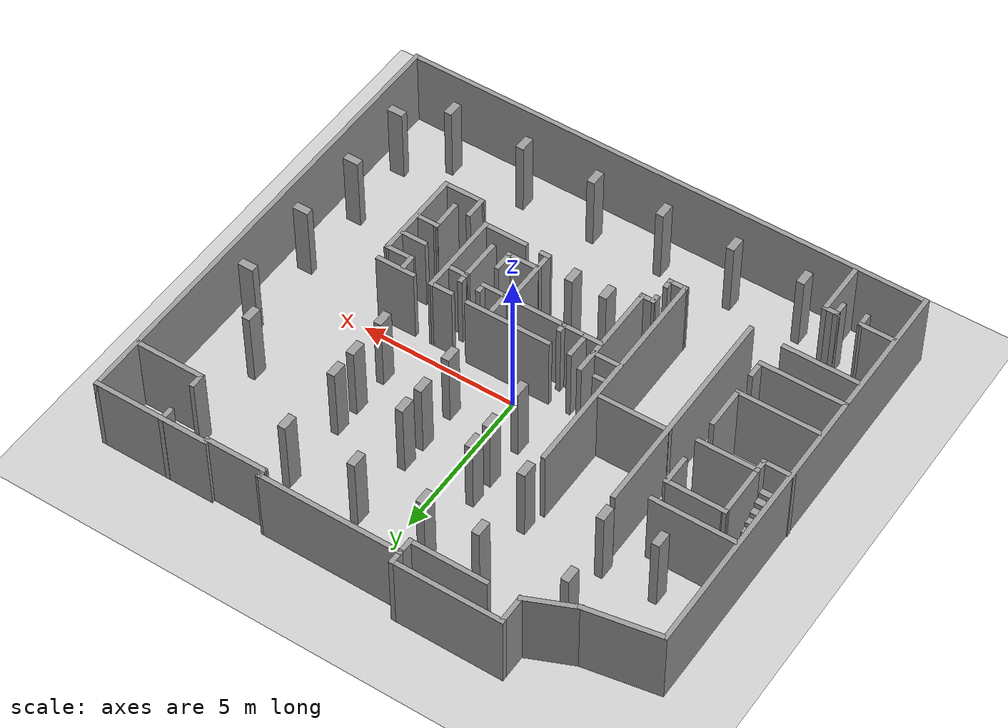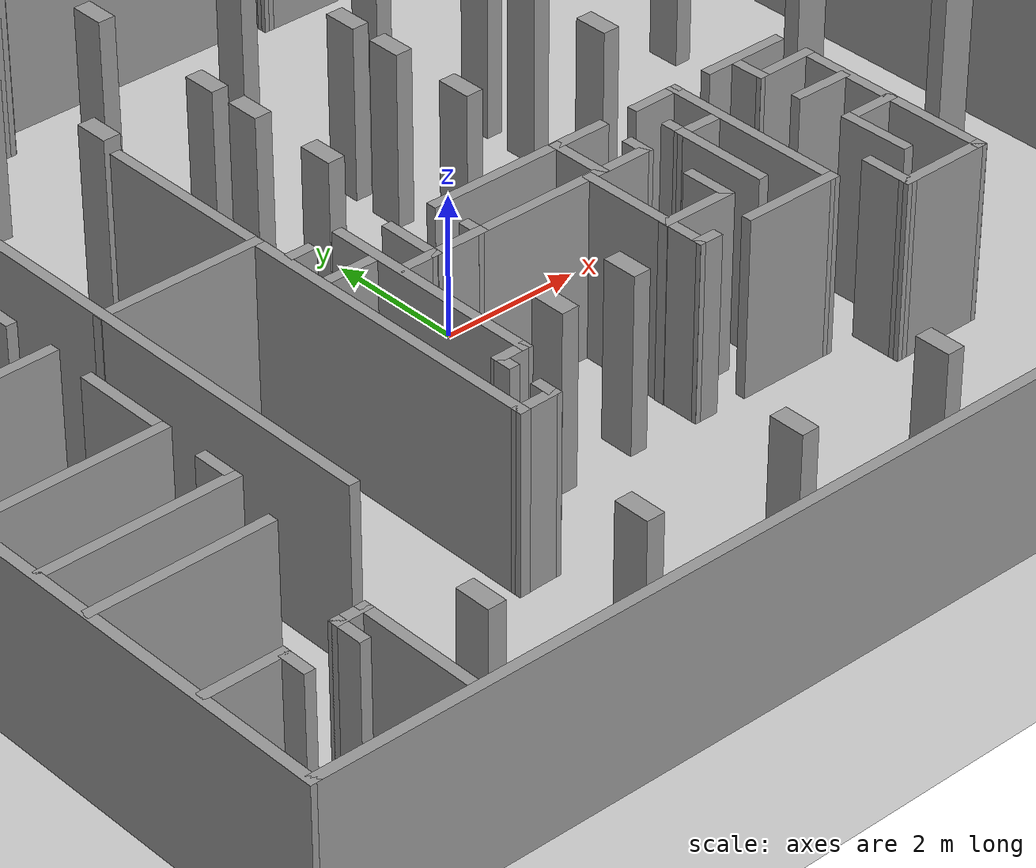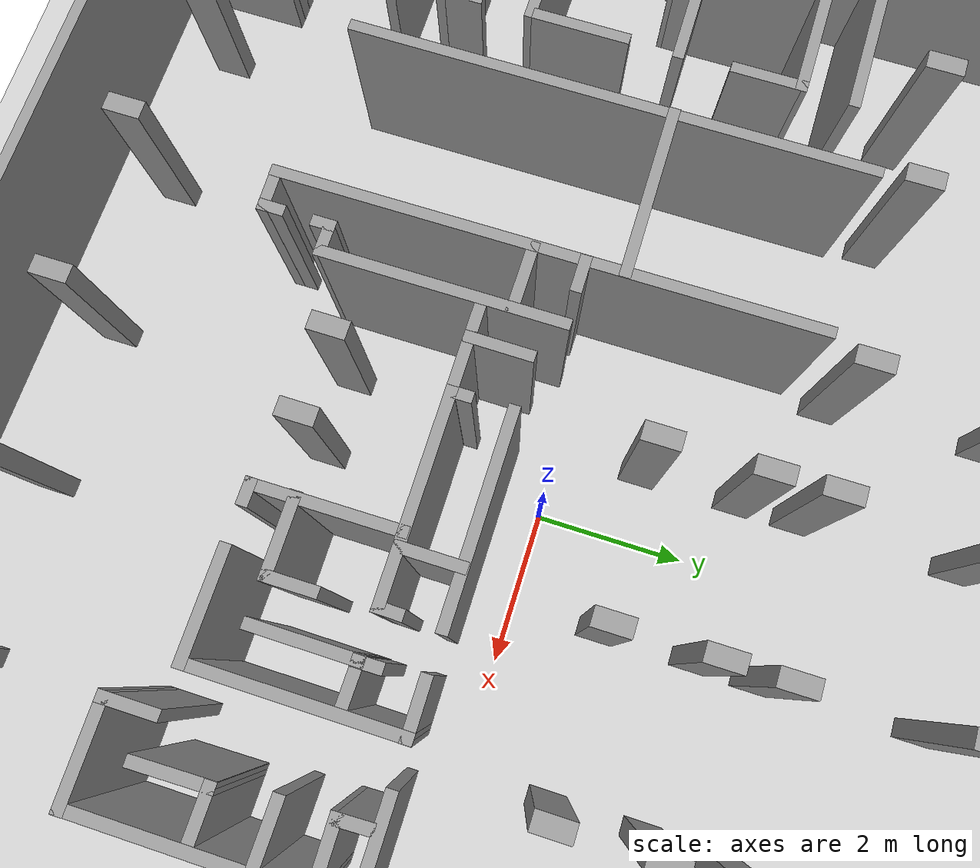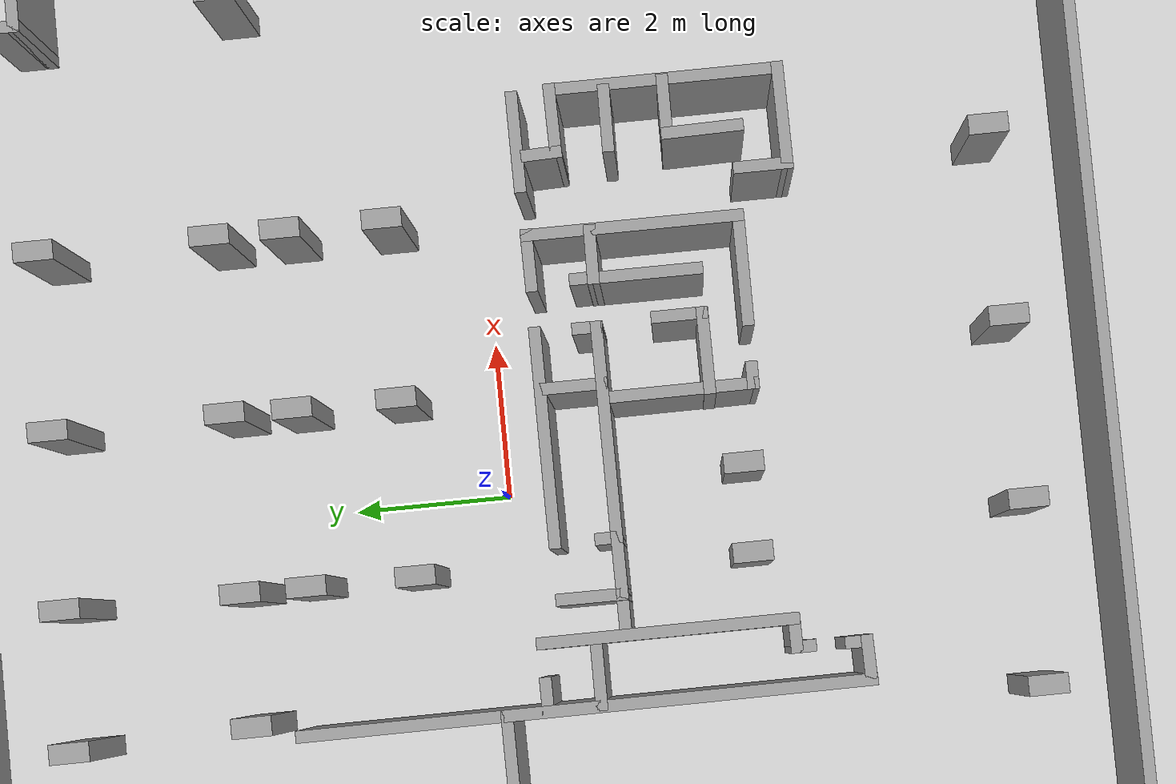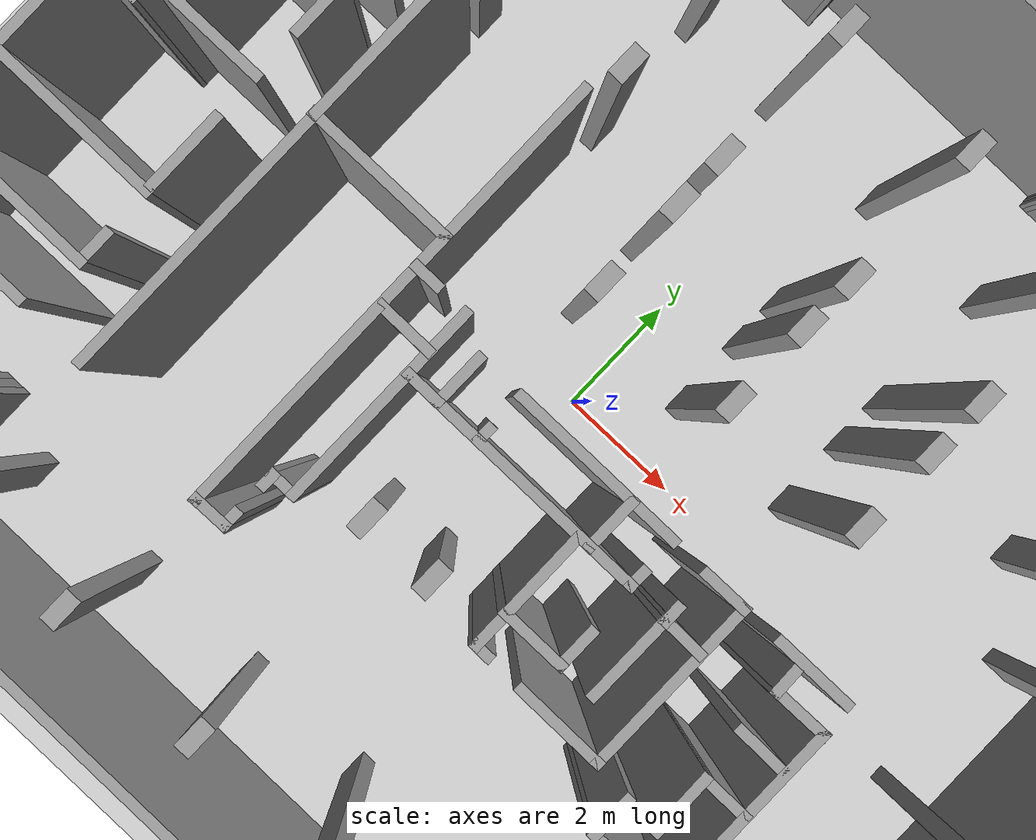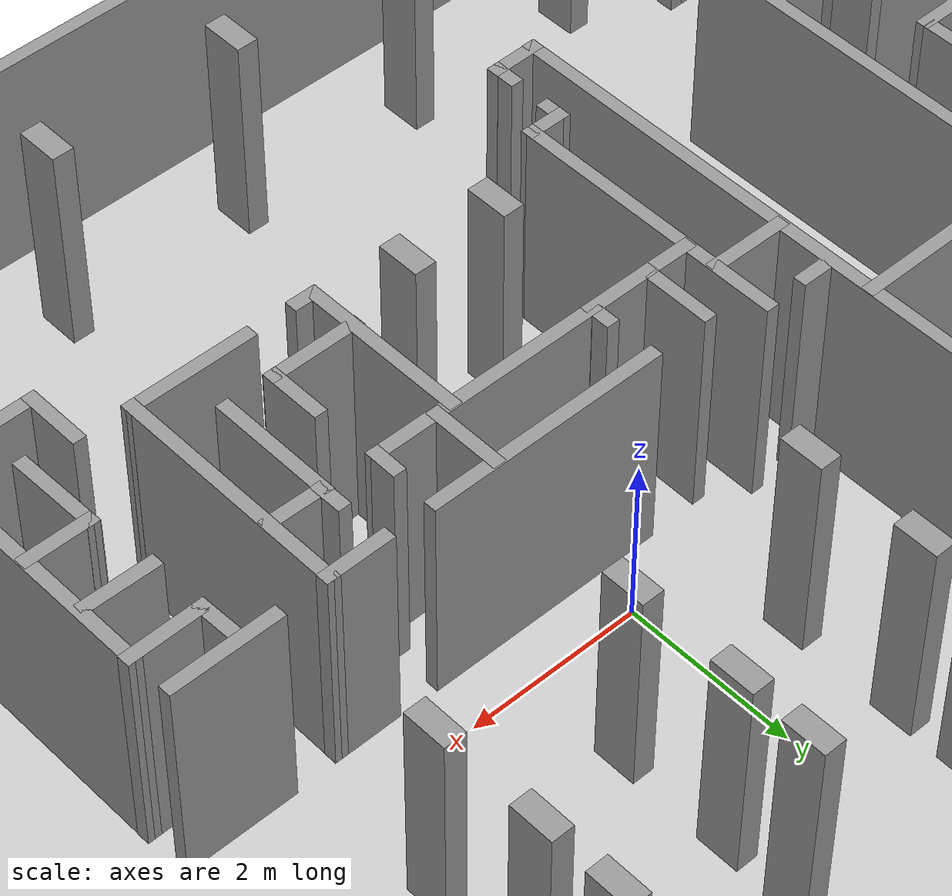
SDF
<sdf version="1.7">
 <world name="default">
  <light name="sun" type="directional">
   <pose>0 0 10 0 -0 0</pose>
   <diffuse>0.8 0.8 0.8 1</diffuse>
   <specular>0.2 0.2 0.2 1</specular>
   <attenuation>
    <range>1000</range>
    <constant>0.9</constant>
    <linear>0.01</linear>
    <quadratic>0.001</quadratic>
   </attenuation>
   <direction>-0.5 0.1 -0.9</direction>
   <spot><inner_angle>0</inner_angle><outer_angle>0</outer_angle><falloff>0</falloff></spot>
  </light>
  <model name="ground_plane">
   <static>1</static>
   <link name="link">
    <collision name="collision">
     <geometry><plane><normal>0 0 1</normal><size>100 100</size></plane></geometry>
     <surface><friction><ode><mu>100</mu><mu2>50</mu2></ode></friction></surface>
    </collision>
    <visual name="visual">
     <cast_shadows>0</cast_shadows>
     <geometry><plane><normal>0 0 1</normal><size>100 100</size></plane></geometry>
     <material>
      <script><uri>file://media/materials/scripts/gazebo.material</uri><name>Gazebo/Grey</name></script>
     </material>
    </visual>
   </link>
  </model>
  <gravity>0 0 -9.8</gravity>
  <magnetic_field>6e-06 2.3e-05 -4.2e-05</magnetic_field>
  <atmosphere type="adiabatic"/>
  <physics type="ode">
   <max_step_size>0.001</max_step_size>
   <real_time_factor>1</real_time_factor>
   <real_time_update_rate>1000</real_time_update_rate>
  </physics>
  <scene><ambient>0.4 0.4 0.4 1</ambient><background>0.7 0.7 0.7 1</background><shadows>1</shadows></scene>
  <spherical_coordinates>
   <surface_model>EARTH_WGS84</surface_model>
   <latitude_deg>0</latitude_deg>
   <longitude_deg>0</longitude_deg>
   <elevation>0</elevation>
   <heading_deg>0</heading_deg>
  </spherical_coordinates>
  <model name="Level1">
   <link name="Stairs_3">
    <visual name="Stairs_3_Visual_0">
     <pose>-8.05835 1.30916 0.09375 0 -0 0</pose>
     <geometry><box><size>0.765 0.21375 0.1875</size></box></geometry>
     <material>
      <script><uri>file://media/materials/scripts/gazebo.material</uri><name>Gazebo/Grey</name></script>
      <ambient>1 1 1 1</ambient>
      <shader type="pixel"/>
     </material>
     <meta><layer>0</layer></meta>
    </visual>
    <visual name="Stairs_3_Visual_1">
     <pose>-8.05835 1.09541 0.28125 0 -0 0</pose>
     <geometry><box><size>0.765 0.21375 0.1875</size></box></geometry>
     <material>
      <script><uri>file://media/materials/scripts/gazebo.material</uri><name>Gazebo/Grey</name></script>
      <ambient>1 1 1 1</ambient>
      <shader type="pixel"/>
     </material>
     <meta><layer>0</layer></meta>
    </visual>
    <visual name="Stairs_3_Visual_2">
     <pose>-8.05835 0.881662 0.46875 0 -0 0</pose>
     <geometry><box><size>0.765 0.21375 0.1875</size></box></geometry>
     <material>
      <script><uri>file://media/materials/scripts/gazebo.material</uri><name>Gazebo/Grey</name></script>
      <ambient>1 1 1 1</ambient>
      <shader type="pixel"/>
     </material>
     <meta><layer>0</layer></meta>
    </visual>
    <visual name="Stairs_3_Visual_3">
     <pose>-8.05835 0.667912 0.65625 0 -0 0</pose>
     <geometry><box><size>0.765 0.21375 0.1875</size></box></geometry>
     <material>
      <script><uri>file://media/materials/scripts/gazebo.material</uri><name>Gazebo/Grey</name></script>
      <ambient>1 1 1 1</ambient>
      <shader type="pixel"/>
     </material>
     <meta><layer>0</layer></meta>
    </visual>
    <visual name="Stairs_3_Visual_4">
     <pose>-8.05835 0.454162 0.84375 0 -0 0</pose>
     <geometry><box><size>0.765 0.21375 0.1875</size></box></geometry>
     <material>
      <script><uri>file://media/materials/scripts/gazebo.material</uri><name>Gazebo/Grey</name></script>
      <ambient>1 1 1 1</ambient>
      <shader type="pixel"/>
     </material>
     <meta><layer>0</layer></meta>
    </visual>
    <visual name="Stairs_3_Visual_5">
     <pose>-8.05835 0.240412 1.03125 0 -0 0</pose>
     <geometry><box><size>0.765 0.21375 0.1875</size></box></geometry>
     <material>
      <script><uri>file://media/materials/scripts/gazebo.material</uri><name>Gazebo/Grey</name></script>
      <ambient>1 1 1 1</ambient>
      <shader type="pixel"/>
     </material>
     <meta><layer>0</layer></meta>
    </visual>
    <visual name="Stairs_3_Visual_6">
     <pose>-8.05835 0.026662 1.21875 0 -0 0</pose>
     <geometry><box><size>0.765 0.21375 0.1875</size></box></geometry>
     <material>
      <script><uri>file://media/materials/scripts/gazebo.material</uri><name>Gazebo/Grey</name></script>
      <ambient>1 1 1 1</ambient>
      <shader type="pixel"/>
     </material>
     <meta><layer>0</layer></meta>
    </visual>
    <visual name="Stairs_3_Visual_7">
     <pose>-8.05835 -0.187088 1.40625 0 -0 0</pose>
     <geometry><box><size>0.765 0.21375 0.1875</size></box></geometry>
     <material>
      <script><uri>file://media/materials/scripts/gazebo.material</uri><name>Gazebo/Grey</name></script>
      <ambient>1 1 1 1</ambient>
      <shader type="pixel"/>
     </material>
     <meta><layer>0</layer></meta>
    </visual>
    <collision name="Stairs_3_Collision_0">
     <pose>-8.05835 1.30916 0.09375 0 -0 0</pose>
     <geometry><box><size>0.765 0.21375 0.1875</size></box></geometry>
     <surface>
      <friction>
       <ode><mu>1</mu><mu2>1</mu2><fdir1>0 0 0</fdir1><slip1>0</slip1><slip2>0</slip2></ode>
       <torsional>
        <coefficient>1</coefficient>
        <patch_radius>0</patch_radius>
        <surface_radius>0</surface_radius>
        <use_patch_radius>1</use_patch_radius>
        <ode><slip>0</slip></ode>
       </torsional>
      </friction>
      <bounce><restitution_coefficient>0</restitution_coefficient><threshold>1e+06</threshold></bounce>
      <contact>
       <collide_without_contact>0</collide_without_contact>
       <collide_without_contact_bitmask>1</collide_without_contact_bitmask>
       <collide_bitmask>1</collide_bitmask>
       <ode>
        <soft_cfm>0</soft_cfm>
        <soft_erp>0.2</soft_erp>
        <kp>1e+13</kp>
        <kd>1</kd>
        <max_vel>0.01</max_vel>
        <min_depth>0</min_depth>
       </ode>
       <bullet>
        <split_impulse>1</split_impulse>
        <split_impulse_penetration_threshold>-0.01</split_impulse_penetration_threshold>
        <soft_cfm>0</soft_cfm>
        <soft_erp>0.2</soft_erp>
        <kp>1e+13</kp>
        <kd>1</kd>
       </bullet>
      </contact>
     </surface>
    </collision>
    <collision name="Stairs_3_Collision_1">
     <pose>-8.05835 1.09541 0.28125 0 -0 0</pose>
     <geometry><box><size>0.765 0.21375 0.1875</size></box></geometry>
     <surface>
      <friction>
       <ode><mu>1</mu><mu2>1</mu2><fdir1>0 0 0</fdir1><slip1>0</slip1><slip2>0</slip2></ode>
       <torsional>
        <coefficient>1</coefficient>
        <patch_radius>0</patch_radius>
        <surface_radius>0</surface_radius>
        <use_patch_radius>1</use_patch_radius>
        <ode><slip>0</slip></ode>
       </torsional>
      </friction>
      <bounce><restitution_coefficient>0</restitution_coefficient><threshold>1e+06</threshold></bounce>
      <contact>
       <collide_without_contact>0</collide_without_contact>
       <collide_without_contact_bitmask>1</collide_without_contact_bitmask>
       <collide_bitmask>1</collide_bitmask>
       <ode>
        <soft_cfm>0</soft_cfm>
        <soft_erp>0.2</soft_erp>
        <kp>1e+13</kp>
        <kd>1</kd>
        <max_vel>0.01</max_vel>
        <min_depth>0</min_depth>
       </ode>
       <bullet>
        <split_impulse>1</split_impulse>
        <split_impulse_penetration_threshold>-0.01</split_impulse_penetration_threshold>
        <soft_cfm>0</soft_cfm>
        <soft_erp>0.2</soft_erp>
        <kp>1e+13</kp>
        <kd>1</kd>
       </bullet>
      </contact>
     </surface>
    </collision>
    <collision name="Stairs_3_Collision_2">
     <pose>-8.05835 0.881662 0.46875 0 -0 0</pose>
     <geometry><box><size>0.765 0.21375 0.1875</size></box></geometry>
     <surface>
      <friction>
       <ode><mu>1</mu><mu2>1</mu2><fdir1>0 0 0</fdir1><slip1>0</slip1><slip2>0</slip2></ode>
       <torsional>
        <coefficient>1</coefficient>
        <patch_radius>0</patch_radius>
        <surface_radius>0</surface_radius>
        <use_patch_radius>1</use_patch_radius>
        <ode><slip>0</slip></ode>
       </torsional>
      </friction>
      <bounce><restitution_coefficient>0</restitution_coefficient><threshold>1e+06</threshold></bounce>
      <contact>
       <collide_without_contact>0</collide_without_contact>
       <collide_without_contact_bitmask>1</collide_without_contact_bitmask>
       <collide_bitmask>1</collide_bitmask>
       <ode>
        <soft_cfm>0</soft_cfm>
        <soft_erp>0.2</soft_erp>
        <kp>1e+13</kp>
        <kd>1</kd>
        <max_vel>0.01</max_vel>
        <min_depth>0</min_depth>
       </ode>
       <bullet>
        <split_impulse>1</split_impulse>
        <split_impulse_penetration_threshold>-0.01</split_impulse_penetration_threshold>
        <soft_cfm>0</soft_cfm>
        <soft_erp>0.2</soft_erp>
        <kp>1e+13</kp>
        <kd>1</kd>
       </bullet>
      </contact>
     </surface>
    </collision>
    <collision name="Stairs_3_Collision_3">
     <pose>-8.05835 0.667912 0.65625 0 -0 0</pose>
     <geometry><box><size>0.765 0.21375 0.1875</size></box></geometry>
     <surface>
      <friction>
       <ode><mu>1</mu><mu2>1</mu2><fdir1>0 0 0</fdir1><slip1>0</slip1><slip2>0</slip2></ode>
       <torsional>
        <coefficient>1</coefficient>
        <patch_radius>0</patch_radius>
        <surface_radius>0</surface_radius>
        <use_patch_radius>1</use_patch_radius>
        <ode><slip>0</slip></ode>
       </torsional>
      </friction>
      <bounce><restitution_coefficient>0</restitution_coefficient><threshold>1e+06</threshold></bounce>
      <contact>
       <collide_without_contact>0</collide_without_contact>
       <collide_without_contact_bitmask>1</collide_without_contact_bitmask>
       <collide_bitmask>1</collide_bitmask>
       <ode>
        <soft_cfm>0</soft_cfm>
        <soft_erp>0.2</soft_erp>
        <kp>1e+13</kp>
        <kd>1</kd>
        <max_vel>0.01</max_vel>
        <min_depth>0</min_depth>
       </ode>
       <bullet>
        <split_impulse>1</split_impulse>
        <split_impulse_penetration_threshold>-0.01</split_impulse_penetration_threshold>
        <soft_cfm>0</soft_cfm>
        <soft_erp>0.2</soft_erp>
        <kp>1e+13</kp>
        <kd>1</kd>
       </bullet>
      </contact>
     </surface>
    </collision>
    <collision name="Stairs_3_Collision_4">
     <pose>-8.05835 0.454162 0.84375 0 -0 0</pose>
     <geometry><box><size>0.765 0.21375 0.1875</size></box></geometry>
     <surface>
      <friction>
       <ode><mu>1</mu><mu2>1</mu2><fdir1>0 0 0</fdir1><slip1>0</slip1><slip2>0</slip2></ode>
       <torsional>
        <coefficient>1</coefficient>
        <patch_radius>0</patch_radius>
        <surface_radius>0</surface_radius>
        <use_patch_radius>1</use_patch_radius>
        <ode><slip>0</slip></ode>
       </torsional>
      </friction>
      <bounce><restitution_coefficient>0</restitution_coefficient><threshold>1e+06</threshold></bounce>
      <contact>
       <collide_without_contact>0</collide_without_contact>
       <collide_without_contact_bitmask>1</collide_without_contact_bitmask>
       <collide_bitmask>1</collide_bitmask>
       <ode>
        <soft_cfm>0</soft_cfm>
        <soft_erp>0.2</soft_erp>
        <kp>1e+13</kp>
        <kd>1</kd>
        <max_vel>0.01</max_vel>
        <min_depth>0</min_depth>
       </ode>
       <bullet>
        <split_impulse>1</split_impulse>
        <split_impulse_penetration_threshold>-0.01</split_impulse_penetration_threshold>
        <soft_cfm>0</soft_cfm>
        <soft_erp>0.2</soft_erp>
        <kp>1e+13</kp>
        <kd>1</kd>
       </bullet>
      </contact>
     </surface>
    </collision>
    <collision name="Stairs_3_Collision_5">
     <pose>-8.05835 0.240412 1.03125 0 -0 0</pose>
     <geometry><box><size>0.765 0.21375 0.1875</size></box></geometry>
     <surface>
      <friction>
       <ode><mu>1</mu><mu2>1</mu2><fdir1>0 0 0</fdir1><slip1>0</slip1><slip2>0</slip2></ode>
       <torsional>
        <coefficient>1</coefficient>
        <patch_radius>0</patch_radius>
        <surface_radius>0</surface_radius>
        <use_patch_radius>1</use_patch_radius>
        <ode><slip>0</slip></ode>
       </torsional>
      </friction>
      <bounce><restitution_coefficient>0</restitution_coefficient><threshold>1e+06</threshold></bounce>
      <contact>
       <collide_without_contact>0</collide_without_contact>
       <collide_without_contact_bitmask>1</collide_without_contact_bitmask>
       <collide_bitmask>1</collide_bitmask>
       <ode>
        <soft_cfm>0</soft_cfm>
        <soft_erp>0.2</soft_erp>
        <kp>1e+13</kp>
        <kd>1</kd>
        <max_vel>0.01</max_vel>
        <min_depth>0</min_depth>
       </ode>
       <bullet>
        <split_impulse>1</split_impulse>
        <split_impulse_penetration_threshold>-0.01</split_impulse_penetration_threshold>
        <soft_cfm>0</soft_cfm>
        <soft_erp>0.2</soft_erp>
        <kp>1e+13</kp>
        <kd>1</kd>
       </bullet>
      </contact>
     </surface>
    </collision>
    <collision name="Stairs_3_Collision_6">
     <pose>-8.05835 0.026662 1.21875 0 -0 0</pose>
     <geometry><box><size>0.765 0.21375 0.1875</size></box></geometry>
     <surface>
      <friction>
       <ode><mu>1</mu><mu2>1</mu2><fdir1>0 0 0</fdir1><slip1>0</slip1><slip2>0</slip2></ode>
       <torsional>
        <coefficient>1</coefficient>
        <patch_radius>0</patch_radius>
        <surface_radius>0</surface_radius>
        <use_patch_radius>1</use_patch_radius>
        <ode><slip>0</slip></ode>
       </torsional>
      </friction>
      <bounce><restitution_coefficient>0</restitution_coefficient><threshold>1e+06</threshold></bounce>
      <contact>
       <collide_without_contact>0</collide_without_contact>
       <collide_without_contact_bitmask>1</collide_without_contact_bitmask>
       <collide_bitmask>1</collide_bitmask>
       <ode>
        <soft_cfm>0</soft_cfm>
        <soft_erp>0.2</soft_erp>
        <kp>1e+13</kp>
        <kd>1</kd>
        <max_vel>0.01</max_vel>
        <min_depth>0</min_depth>
       </ode>
       <bullet>
        <split_impulse>1</split_impulse>
        <split_impulse_penetration_threshold>-0.01</split_impulse_penetration_threshold>
        <soft_cfm>0</soft_cfm>
        <soft_erp>0.2</soft_erp>
        <kp>1e+13</kp>
        <kd>1</kd>
       </bullet>
      </contact>
     </surface>
    </collision>
    <collision name="Stairs_3_Collision_7">
     <pose>-8.05835 -0.187088 1.40625 0 -0 0</pose>
     <geometry><box><size>0.765 0.21375 0.1875</size></box></geometry>
     <surface>
      <friction>
       <ode><mu>1</mu><mu2>1</mu2><fdir1>0 0 0</fdir1><slip1>0</slip1><slip2>0</slip2></ode>
       <torsional>
        <coefficient>1</coefficient>
        <patch_radius>0</patch_radius>
        <surface_radius>0</surface_radius>
        <use_patch_radius>1</use_patch_radius>
        <ode><slip>0</slip></ode>
       </torsional>
      </friction>
      <bounce><restitution_coefficient>0</restitution_coefficient><threshold>1e+06</threshold></bounce>
      <contact>
       <collide_without_contact>0</collide_without_contact>
       <collide_without_contact_bitmask>1</collide_without_contact_bitmask>
       <collide_bitmask>1</collide_bitmask>
       <ode>
        <soft_cfm>0</soft_cfm>
        <soft_erp>0.2</soft_erp>
        <kp>1e+13</kp>
        <kd>1</kd>
        <max_vel>0.01</max_vel>
        <min_depth>0</min_depth>
       </ode>
       <bullet>
        <split_impulse>1</split_impulse>
        <split_impulse_penetration_threshold>-0.01</split_impulse_penetration_threshold>
        <soft_cfm>0</soft_cfm>
        <soft_erp>0.2</soft_erp>
        <kp>1e+13</kp>
        <kd>1</kd>
       </bullet>
      </contact>
     </surface>
    </collision>
   </link>
   <link name="Wall_10">
    <pose>4.88325 7.14657 0 0 0 -1.5708</pose>
    <visual name="Wall_10_Visual">
     <pose>0 0 1.25 0 -0 0</pose>
     <geometry><box><size>0.25 0.15 2.5</size></box></geometry>
     <material>
      <script><uri>file://media/materials/scripts/gazebo.material</uri><name>Gazebo/Grey</name></script>
      <ambient>1 1 1 1</ambient>
      <shader type="pixel"/>
     </material>
     <meta><layer>0</layer></meta>
    </visual>
    <collision name="Wall_10_Collision">
     <pose>0 0 1.25 0 -0 0</pose>
     <geometry><box><size>0.25 0.15 2.5</size></box></geometry>
     <surface>
      <friction>
       <ode><mu>1</mu><mu2>1</mu2><fdir1>0 0 0</fdir1><slip1>0</slip1><slip2>0</slip2></ode>
       <torsional>
        <coefficient>1</coefficient>
        <patch_radius>0</patch_radius>
        <surface_radius>0</surface_radius>
        <use_patch_radius>1</use_patch_radius>
        <ode><slip>0</slip></ode>
       </torsional>
      </friction>
      <bounce><restitution_coefficient>0</restitution_coefficient><threshold>1e+06</threshold></bounce>
      <contact>
       <collide_without_contact>0</collide_without_contact>
       <collide_without_contact_bitmask>1</collide_without_contact_bitmask>
       <collide_bitmask>1</collide_bitmask>
       <ode>
        <soft_cfm>0</soft_cfm>
        <soft_erp>0.2</soft_erp>
        <kp>1e+13</kp>
        <kd>1</kd>
        <max_vel>0.01</max_vel>
        <min_depth>0</min_depth>
       </ode>
       <bullet>
        <split_impulse>1</split_impulse>
        <split_impulse_penetration_threshold>-0.01</split_impulse_penetration_threshold>
        <soft_cfm>0</soft_cfm>
        <soft_erp>0.2</soft_erp>
        <kp>1e+13</kp>
        <kd>1</kd>
       </bullet>
      </contact>
     </surface>
    </collision>
   </link>
   <link name="Wall_100">
    <pose>1.87692 -1.27369 0 0 -0 1.55725</pose>
    <visual name="Wall_100_Visual">
     <pose>0 0 1.25 0 -0 0</pose>
     <geometry><box><size>0.380938 0.15 2.5</size></box></geometry>
     <material>
      <script><uri>file://media/materials/scripts/gazebo.material</uri><name>Gazebo/Grey</name></script>
      <ambient>1 1 1 1</ambient>
      <shader type="pixel"/>
     </material>
     <meta><layer>0</layer></meta>
    </visual>
    <collision name="Wall_100_Collision">
     <pose>0 0 1.25 0 -0 0</pose>
     <geometry><box><size>0.380938 0.15 2.5</size></box></geometry>
     <surface>
      <friction>
       <ode><mu>1</mu><mu2>1</mu2><fdir1>0 0 0</fdir1><slip1>0</slip1><slip2>0</slip2></ode>
       <torsional>
        <coefficient>1</coefficient>
        <patch_radius>0</patch_radius>
        <surface_radius>0</surface_radius>
        <use_patch_radius>1</use_patch_radius>
        <ode><slip>0</slip></ode>
       </torsional>
      </friction>
      <bounce><restitution_coefficient>0</restitution_coefficient><threshold>1e+06</threshold></bounce>
      <contact>
       <collide_without_contact>0</collide_without_contact>
       <collide_without_contact_bitmask>1</collide_without_contact_bitmask>
       <collide_bitmask>1</collide_bitmask>
       <ode>
        <soft_cfm>0</soft_cfm>
        <soft_erp>0.2</soft_erp>
        <kp>1e+13</kp>
        <kd>1</kd>
        <max_vel>0.01</max_vel>
        <min_depth>0</min_depth>
       </ode>
       <bullet>
        <split_impulse>1</split_impulse>
        <split_impulse_penetration_threshold>-0.01</split_impulse_penetration_threshold>
        <soft_cfm>0</soft_cfm>
        <soft_erp>0.2</soft_erp>
        <kp>1e+13</kp>
        <kd>1</kd>
       </bullet>
      </contact>
     </surface>
    </collision>
   </link>
   <link name="Wall_102">
    <pose>0.994248 -2.32572 0 0 0 -1.56872</pose>
    <visual name="Wall_102_Visual">
     <pose>0 0 1.25 0 -0 0</pose>
     <geometry><box><size>1.99145 0.15 2.5</size></box></geometry>
     <material>
      <script><uri>file://media/materials/scripts/gazebo.material</uri><name>Gazebo/Grey</name></script>
      <ambient>1 1 1 1</ambient>
      <shader type="pixel"/>
     </material>
     <meta><layer>0</layer></meta>
    </visual>
    <collision name="Wall_102_Collision">
     <pose>0 0 1.25 0 -0 0</pose>
     <geometry><box><size>1.99145 0.15 2.5</size></box></geometry>
     <surface>
      <friction>
       <ode><mu>1</mu><mu2>1</mu2><fdir1>0 0 0</fdir1><slip1>0</slip1><slip2>0</slip2></ode>
       <torsional>
        <coefficient>1</coefficient>
        <patch_radius>0</patch_radius>
        <surface_radius>0</surface_radius>
        <use_patch_radius>1</use_patch_radius>
        <ode><slip>0</slip></ode>
       </torsional>
      </friction>
      <bounce><restitution_coefficient>0</restitution_coefficient><threshold>1e+06</threshold></bounce>
      <contact>
       <collide_without_contact>0</collide_without_contact>
       <collide_without_contact_bitmask>1</collide_without_contact_bitmask>
       <collide_bitmask>1</collide_bitmask>
       <ode>
        <soft_cfm>0</soft_cfm>
        <soft_erp>0.2</soft_erp>
        <kp>1e+13</kp>
        <kd>1</kd>
        <max_vel>0.01</max_vel>
        <min_depth>0</min_depth>
       </ode>
       <bullet>
        <split_impulse>1</split_impulse>
        <split_impulse_penetration_threshold>-0.01</split_impulse_penetration_threshold>
        <soft_cfm>0</soft_cfm>
        <soft_erp>0.2</soft_erp>
        <kp>1e+13</kp>
        <kd>1</kd>
       </bullet>
      </contact>
     </surface>
    </collision>
   </link>
   <link name="Wall_103">
    <pose>1.09496 -3.24734 0 0 0 -0.009371</pose>
    <visual name="Wall_103_Visual">
     <pose>0 0 1.25 0 -0 0</pose>
     <geometry><box><size>0.347613 0.15 2.5</size></box></geometry>
     <material>
      <script><uri>file://media/materials/scripts/gazebo.material</uri><name>Gazebo/Grey</name></script>
      <ambient>1 1 1 1</ambient>
      <shader type="pixel"/>
     </material>
     <meta><layer>0</layer></meta>
    </visual>
    <collision name="Wall_103_Collision">
     <pose>0 0 1.25 0 -0 0</pose>
     <geometry><box><size>0.347613 0.15 2.5</size></box></geometry>
     <surface>
      <friction>
       <ode><mu>1</mu><mu2>1</mu2><fdir1>0 0 0</fdir1><slip1>0</slip1><slip2>0</slip2></ode>
       <torsional>
        <coefficient>1</coefficient>
        <patch_radius>0</patch_radius>
        <surface_radius>0</surface_radius>
        <use_patch_radius>1</use_patch_radius>
        <ode><slip>0</slip></ode>
       </torsional>
      </friction>
      <bounce><restitution_coefficient>0</restitution_coefficient><threshold>1e+06</threshold></bounce>
      <contact>
       <collide_without_contact>0</collide_without_contact>
       <collide_without_contact_bitmask>1</collide_without_contact_bitmask>
       <collide_bitmask>1</collide_bitmask>
       <ode>
        <soft_cfm>0</soft_cfm>
        <soft_erp>0.2</soft_erp>
        <kp>1e+13</kp>
        <kd>1</kd>
        <max_vel>0.01</max_vel>
        <min_depth>0</min_depth>
       </ode>
       <bullet>
        <split_impulse>1</split_impulse>
        <split_impulse_penetration_threshold>-0.01</split_impulse_penetration_threshold>
        <soft_cfm>0</soft_cfm>
        <soft_erp>0.2</soft_erp>
        <kp>1e+13</kp>
        <kd>1</kd>
       </bullet>
      </contact>
     </surface>
    </collision>
   </link>
   <link name="Wall_109">
    <pose>1.4559 -2.70636 0 0 -0 0</pose>
    <visual name="Wall_109_Visual">
     <pose>0 0 1.25 0 -0 0</pose>
     <geometry><box><size>1.08842 0.15 2.5</size></box></geometry>
     <material>
      <script><uri>file://media/materials/scripts/gazebo.material</uri><name>Gazebo/Grey</name></script>
      <ambient>1 1 1 1</ambient>
      <shader type="pixel"/>
     </material>
     <meta><layer>0</layer></meta>
    </visual>
    <collision name="Wall_109_Collision">
     <pose>0 0 1.25 0 -0 0</pose>
     <geometry><box><size>1.08842 0.15 2.5</size></box></geometry>
     <surface>
      <friction>
       <ode><mu>1</mu><mu2>1</mu2><fdir1>0 0 0</fdir1><slip1>0</slip1><slip2>0</slip2></ode>
       <torsional>
        <coefficient>1</coefficient>
        <patch_radius>0</patch_radius>
        <surface_radius>0</surface_radius>
        <use_patch_radius>1</use_patch_radius>
        <ode><slip>0</slip></ode>
       </torsional>
      </friction>
      <bounce><restitution_coefficient>0</restitution_coefficient><threshold>1e+06</threshold></bounce>
      <contact>
       <collide_without_contact>0</collide_without_contact>
       <collide_without_contact_bitmask>1</collide_without_contact_bitmask>
       <collide_bitmask>1</collide_bitmask>
       <ode>
        <soft_cfm>0</soft_cfm>
        <soft_erp>0.2</soft_erp>
        <kp>1e+13</kp>
        <kd>1</kd>
        <max_vel>0.01</max_vel>
        <min_depth>0</min_depth>
       </ode>
       <bullet>
        <split_impulse>1</split_impulse>
        <split_impulse_penetration_threshold>-0.01</split_impulse_penetration_threshold>
        <soft_cfm>0</soft_cfm>
        <soft_erp>0.2</soft_erp>
        <kp>1e+13</kp>
        <kd>1</kd>
       </bullet>
      </contact>
     </surface>
    </collision>
   </link>
   <link name="Wall_11">
    <pose>3.95825 7.09657 0 0 -0 3.14159</pose>
    <visual name="Wall_11_Visual">
     <pose>0 0 1.25 0 -0 0</pose>
     <geometry><box><size>2 0.15 2.5</size></box></geometry>
     <material>
      <script><uri>file://media/materials/scripts/gazebo.material</uri><name>Gazebo/Grey</name></script>
      <ambient>1 1 1 1</ambient>
      <shader type="pixel"/>
     </material>
     <meta><layer>0</layer></meta>
    </visual>
    <collision name="Wall_11_Collision">
     <pose>0 0 1.25 0 -0 0</pose>
     <geometry><box><size>2 0.15 2.5</size></box></geometry>
     <surface>
      <friction>
       <ode><mu>1</mu><mu2>1</mu2><fdir1>0 0 0</fdir1><slip1>0</slip1><slip2>0</slip2></ode>
       <torsional>
        <coefficient>1</coefficient>
        <patch_radius>0</patch_radius>
        <surface_radius>0</surface_radius>
        <use_patch_radius>1</use_patch_radius>
        <ode><slip>0</slip></ode>
       </torsional>
      </friction>
      <bounce><restitution_coefficient>0</restitution_coefficient><threshold>1e+06</threshold></bounce>
      <contact>
       <collide_without_contact>0</collide_without_contact>
       <collide_without_contact_bitmask>1</collide_without_contact_bitmask>
       <collide_bitmask>1</collide_bitmask>
       <ode>
        <soft_cfm>0</soft_cfm>
        <soft_erp>0.2</soft_erp>
        <kp>1e+13</kp>
        <kd>1</kd>
        <max_vel>0.01</max_vel>
        <min_depth>0</min_depth>
       </ode>
       <bullet>
        <split_impulse>1</split_impulse>
        <split_impulse_penetration_threshold>-0.01</split_impulse_penetration_threshold>
        <soft_cfm>0</soft_cfm>
        <soft_erp>0.2</soft_erp>
        <kp>1e+13</kp>
        <kd>1</kd>
       </bullet>
      </contact>
     </surface>
    </collision>
   </link>
   <link name="Wall_110">
    <pose>1.92511 -2.42346 0 0 -0 1.5708</pose>
    <visual name="Wall_110_Visual">
     <pose>0 0 1.25 0 -0 0</pose>
     <geometry><box><size>0.707254 0.15 2.5</size></box></geometry>
     <material>
      <script><uri>file://media/materials/scripts/gazebo.material</uri><name>Gazebo/Grey</name></script>
      <ambient>1 1 1 1</ambient>
      <shader type="pixel"/>
     </material>
     <meta><layer>0</layer></meta>
    </visual>
    <collision name="Wall_110_Collision">
     <pose>0 0 1.25 0 -0 0</pose>
     <geometry><box><size>0.707254 0.15 2.5</size></box></geometry>
     <surface>
      <friction>
       <ode><mu>1</mu><mu2>1</mu2><fdir1>0 0 0</fdir1><slip1>0</slip1><slip2>0</slip2></ode>
       <torsional>
        <coefficient>1</coefficient>
        <patch_radius>0</patch_radius>
        <surface_radius>0</surface_radius>
        <use_patch_radius>1</use_patch_radius>
        <ode><slip>0</slip></ode>
       </torsional>
      </friction>
      <bounce><restitution_coefficient>0</restitution_coefficient><threshold>1e+06</threshold></bounce>
      <contact>
       <collide_without_contact>0</collide_without_contact>
       <collide_without_contact_bitmask>1</collide_without_contact_bitmask>
       <collide_bitmask>1</collide_bitmask>
       <ode>
        <soft_cfm>0</soft_cfm>
        <soft_erp>0.2</soft_erp>
        <kp>1e+13</kp>
        <kd>1</kd>
        <max_vel>0.01</max_vel>
        <min_depth>0</min_depth>
       </ode>
       <bullet>
        <split_impulse>1</split_impulse>
        <split_impulse_penetration_threshold>-0.01</split_impulse_penetration_threshold>
        <soft_cfm>0</soft_cfm>
        <soft_erp>0.2</soft_erp>
        <kp>1e+13</kp>
        <kd>1</kd>
       </bullet>
      </contact>
     </surface>
    </collision>
   </link>
   <link name="Wall_112">
    <pose>2.43654 -3.26455 0 0 0 -0.005293</pose>
    <visual name="Wall_112_Visual">
     <pose>0 0 1.25 0 -0 0</pose>
     <geometry><box><size>1.4558 0.15 2.5</size></box></geometry>
     <material>
      <script><uri>file://media/materials/scripts/gazebo.material</uri><name>Gazebo/Grey</name></script>
      <ambient>1 1 1 1</ambient>
      <shader type="pixel"/>
     </material>
     <meta><layer>0</layer></meta>
    </visual>
    <collision name="Wall_112_Collision">
     <pose>0 0 1.25 0 -0 0</pose>
     <geometry><box><size>1.4558 0.15 2.5</size></box></geometry>
     <surface>
      <friction>
       <ode><mu>1</mu><mu2>1</mu2><fdir1>0 0 0</fdir1><slip1>0</slip1><slip2>0</slip2></ode>
       <torsional>
        <coefficient>1</coefficient>
        <patch_radius>0</patch_radius>
        <surface_radius>0</surface_radius>
        <use_patch_radius>1</use_patch_radius>
        <ode><slip>0</slip></ode>
       </torsional>
      </friction>
      <bounce><restitution_coefficient>0</restitution_coefficient><threshold>1e+06</threshold></bounce>
      <contact>
       <collide_without_contact>0</collide_without_contact>
       <collide_without_contact_bitmask>1</collide_without_contact_bitmask>
       <collide_bitmask>1</collide_bitmask>
       <ode>
        <soft_cfm>0</soft_cfm>
        <soft_erp>0.2</soft_erp>
        <kp>1e+13</kp>
        <kd>1</kd>
        <max_vel>0.01</max_vel>
        <min_depth>0</min_depth>
       </ode>
       <bullet>
        <split_impulse>1</split_impulse>
        <split_impulse_penetration_threshold>-0.01</split_impulse_penetration_threshold>
        <soft_cfm>0</soft_cfm>
        <soft_erp>0.2</soft_erp>
        <kp>1e+13</kp>
        <kd>1</kd>
       </bullet>
      </contact>
     </surface>
    </collision>
   </link>
   <link name="Wall_113">
    <pose>3.09186 -1.9509 0 0 -0 1.56895</pose>
    <visual name="Wall_113_Visual">
     <pose>0 0 1.25 0 -0 0</pose>
     <geometry><box><size>2.7842 0.15 2.5</size></box></geometry>
     <material>
      <script><uri>file://media/materials/scripts/gazebo.material</uri><name>Gazebo/Grey</name></script>
      <ambient>1 1 1 1</ambient>
      <shader type="pixel"/>
     </material>
     <meta><layer>0</layer></meta>
    </visual>
    <collision name="Wall_113_Collision">
     <pose>0 0 1.25 0 -0 0</pose>
     <geometry><box><size>2.7842 0.15 2.5</size></box></geometry>
     <surface>
      <friction>
       <ode><mu>1</mu><mu2>1</mu2><fdir1>0 0 0</fdir1><slip1>0</slip1><slip2>0</slip2></ode>
       <torsional>
        <coefficient>1</coefficient>
        <patch_radius>0</patch_radius>
        <surface_radius>0</surface_radius>
        <use_patch_radius>1</use_patch_radius>
        <ode><slip>0</slip></ode>
       </torsional>
      </friction>
      <bounce><restitution_coefficient>0</restitution_coefficient><threshold>1e+06</threshold></bounce>
      <contact>
       <collide_without_contact>0</collide_without_contact>
       <collide_without_contact_bitmask>1</collide_without_contact_bitmask>
       <collide_bitmask>1</collide_bitmask>
       <ode>
        <soft_cfm>0</soft_cfm>
        <soft_erp>0.2</soft_erp>
        <kp>1e+13</kp>
        <kd>1</kd>
        <max_vel>0.01</max_vel>
        <min_depth>0</min_depth>
       </ode>
       <bullet>
        <split_impulse>1</split_impulse>
        <split_impulse_penetration_threshold>-0.01</split_impulse_penetration_threshold>
        <soft_cfm>0</soft_cfm>
        <soft_erp>0.2</soft_erp>
        <kp>1e+13</kp>
        <kd>1</kd>
       </bullet>
      </contact>
     </surface>
    </collision>
   </link>
   <link name="Wall_117">
    <pose>2.48229 -2.05263 0 0 -0 1.56789</pose>
    <visual name="Wall_117_Visual">
     <pose>0 0 1.25 0 -0 0</pose>
     <geometry><box><size>1.43844 0.15 2.5</size></box></geometry>
     <material>
      <script><uri>file://media/materials/scripts/gazebo.material</uri><name>Gazebo/Grey</name></script>
      <ambient>1 1 1 1</ambient>
      <shader type="pixel"/>
     </material>
     <meta><layer>0</layer></meta>
    </visual>
    <collision name="Wall_117_Collision">
     <pose>0 0 1.25 0 -0 0</pose>
     <geometry><box><size>1.43844 0.15 2.5</size></box></geometry>
     <surface>
      <friction>
       <ode><mu>1</mu><mu2>1</mu2><fdir1>0 0 0</fdir1><slip1>0</slip1><slip2>0</slip2></ode>
       <torsional>
        <coefficient>1</coefficient>
        <patch_radius>0</patch_radius>
        <surface_radius>0</surface_radius>
        <use_patch_radius>1</use_patch_radius>
        <ode><slip>0</slip></ode>
       </torsional>
      </friction>
      <bounce><restitution_coefficient>0</restitution_coefficient><threshold>1e+06</threshold></bounce>
      <contact>
       <collide_without_contact>0</collide_without_contact>
       <collide_without_contact_bitmask>1</collide_without_contact_bitmask>
       <collide_bitmask>1</collide_bitmask>
       <ode>
        <soft_cfm>0</soft_cfm>
        <soft_erp>0.2</soft_erp>
        <kp>1e+13</kp>
        <kd>1</kd>
        <max_vel>0.01</max_vel>
        <min_depth>0</min_depth>
       </ode>
       <bullet>
        <split_impulse>1</split_impulse>
        <split_impulse_penetration_threshold>-0.01</split_impulse_penetration_threshold>
        <soft_cfm>0</soft_cfm>
        <soft_erp>0.2</soft_erp>
        <kp>1e+13</kp>
        <kd>1</kd>
       </bullet>
      </contact>
     </surface>
    </collision>
   </link>
   <link name="Wall_118">
    <pose>2.78063 -1.41333 0 0 0 -0.016565</pose>
    <visual name="Wall_118_Visual">
     <pose>0 0 1.25 0 -0 0</pose>
     <geometry><box><size>0.743336 0.15 2.5</size></box></geometry>
     <material>
      <script><uri>file://media/materials/scripts/gazebo.material</uri><name>Gazebo/Grey</name></script>
      <ambient>1 1 1 1</ambient>
      <shader type="pixel"/>
     </material>
     <meta><layer>0</layer></meta>
    </visual>
    <collision name="Wall_118_Collision">
     <pose>0 0 1.25 0 -0 0</pose>
     <geometry><box><size>0.743336 0.15 2.5</size></box></geometry>
     <surface>
      <friction>
       <ode><mu>1</mu><mu2>1</mu2><fdir1>0 0 0</fdir1><slip1>0</slip1><slip2>0</slip2></ode>
       <torsional>
        <coefficient>1</coefficient>
        <patch_radius>0</patch_radius>
        <surface_radius>0</surface_radius>
        <use_patch_radius>1</use_patch_radius>
        <ode><slip>0</slip></ode>
       </torsional>
      </friction>
      <bounce><restitution_coefficient>0</restitution_coefficient><threshold>1e+06</threshold></bounce>
      <contact>
       <collide_without_contact>0</collide_without_contact>
       <collide_without_contact_bitmask>1</collide_without_contact_bitmask>
       <collide_bitmask>1</collide_bitmask>
       <ode>
        <soft_cfm>0</soft_cfm>
        <soft_erp>0.2</soft_erp>
        <kp>1e+13</kp>
        <kd>1</kd>
        <max_vel>0.01</max_vel>
        <min_depth>0</min_depth>
       </ode>
       <bullet>
        <split_impulse>1</split_impulse>
        <split_impulse_penetration_threshold>-0.01</split_impulse_penetration_threshold>
        <soft_cfm>0</soft_cfm>
        <soft_erp>0.2</soft_erp>
        <kp>1e+13</kp>
        <kd>1</kd>
       </bullet>
      </contact>
     </surface>
    </collision>
   </link>
   <link name="Wall_12">
    <pose>3.03333 7.19816 0 0 -0 1.57002</pose>
    <visual name="Wall_12_Visual">
     <pose>0 0 1.25 0 -0 0</pose>
     <geometry><box><size>0.353181 0.15 2.5</size></box></geometry>
     <material>
      <script><uri>file://media/materials/scripts/gazebo.material</uri><name>Gazebo/Grey</name></script>
      <ambient>1 1 1 1</ambient>
      <shader type="pixel"/>
     </material>
     <meta><layer>0</layer></meta>
    </visual>
    <collision name="Wall_12_Collision">
     <pose>0 0 1.25 0 -0 0</pose>
     <geometry><box><size>0.353181 0.15 2.5</size></box></geometry>
     <surface>
      <friction>
       <ode><mu>1</mu><mu2>1</mu2><fdir1>0 0 0</fdir1><slip1>0</slip1><slip2>0</slip2></ode>
       <torsional>
        <coefficient>1</coefficient>
        <patch_radius>0</patch_radius>
        <surface_radius>0</surface_radius>
        <use_patch_radius>1</use_patch_radius>
        <ode><slip>0</slip></ode>
       </torsional>
      </friction>
      <bounce><restitution_coefficient>0</restitution_coefficient><threshold>1e+06</threshold></bounce>
      <contact>
       <collide_without_contact>0</collide_without_contact>
       <collide_without_contact_bitmask>1</collide_without_contact_bitmask>
       <collide_bitmask>1</collide_bitmask>
       <ode>
        <soft_cfm>0</soft_cfm>
        <soft_erp>0.2</soft_erp>
        <kp>1e+13</kp>
        <kd>1</kd>
        <max_vel>0.01</max_vel>
        <min_depth>0</min_depth>
       </ode>
       <bullet>
        <split_impulse>1</split_impulse>
        <split_impulse_penetration_threshold>-0.01</split_impulse_penetration_threshold>
        <soft_cfm>0</soft_cfm>
        <soft_erp>0.2</soft_erp>
        <kp>1e+13</kp>
        <kd>1</kd>
       </bullet>
      </contact>
     </surface>
    </collision>
   </link>
   <link name="Wall_120">
    <pose>2.7801 -0.636031 0 0 -0 0.007026</pose>
    <visual name="Wall_120_Visual">
     <pose>0 0 1.25 0 -0 0</pose>
     <geometry><box><size>0.784003 0.15 2.5</size></box></geometry>
     <material>
      <script><uri>file://media/materials/scripts/gazebo.material</uri><name>Gazebo/Grey</name></script>
      <ambient>1 1 1 1</ambient>
      <shader type="pixel"/>
     </material>
     <meta><layer>0</layer></meta>
    </visual>
    <collision name="Wall_120_Collision">
     <pose>0 0 1.25 0 -0 0</pose>
     <geometry><box><size>0.784003 0.15 2.5</size></box></geometry>
     <surface>
      <friction>
       <ode><mu>1</mu><mu2>1</mu2><fdir1>0 0 0</fdir1><slip1>0</slip1><slip2>0</slip2></ode>
       <torsional>
        <coefficient>1</coefficient>
        <patch_radius>0</patch_radius>
        <surface_radius>0</surface_radius>
        <use_patch_radius>1</use_patch_radius>
        <ode><slip>0</slip></ode>
       </torsional>
      </friction>
      <bounce><restitution_coefficient>0</restitution_coefficient><threshold>1e+06</threshold></bounce>
      <contact>
       <collide_without_contact>0</collide_without_contact>
       <collide_without_contact_bitmask>1</collide_without_contact_bitmask>
       <collide_bitmask>1</collide_bitmask>
       <ode>
        <soft_cfm>0</soft_cfm>
        <soft_erp>0.2</soft_erp>
        <kp>1e+13</kp>
        <kd>1</kd>
        <max_vel>0.01</max_vel>
        <min_depth>0</min_depth>
       </ode>
       <bullet>
        <split_impulse>1</split_impulse>
        <split_impulse_penetration_threshold>-0.01</split_impulse_penetration_threshold>
        <soft_cfm>0</soft_cfm>
        <soft_erp>0.2</soft_erp>
        <kp>1e+13</kp>
        <kd>1</kd>
       </bullet>
      </contact>
     </surface>
    </collision>
   </link>
   <link name="Wall_125">
    <pose>2.49241 -1.2982 0 0 0 -1.5603</pose>
    <visual name="Wall_125_Visual">
     <pose>0 0 1.25 0 -0 0</pose>
     <geometry><box><size>0.379383 0.15 2.5</size></box></geometry>
     <material>
      <script><uri>file://media/materials/scripts/gazebo.material</uri><name>Gazebo/Grey</name></script>
      <ambient>1 1 1 1</ambient>
      <shader type="pixel"/>
     </material>
     <meta><layer>0</layer></meta>
    </visual>
    <collision name="Wall_125_Collision">
     <pose>0 0 1.25 0 -0 0</pose>
     <geometry><box><size>0.379383 0.15 2.5</size></box></geometry>
     <surface>
      <friction>
       <ode><mu>1</mu><mu2>1</mu2><fdir1>0 0 0</fdir1><slip1>0</slip1><slip2>0</slip2></ode>
       <torsional>
        <coefficient>1</coefficient>
        <patch_radius>0</patch_radius>
        <surface_radius>0</surface_radius>
        <use_patch_radius>1</use_patch_radius>
        <ode><slip>0</slip></ode>
       </torsional>
      </friction>
      <bounce><restitution_coefficient>0</restitution_coefficient><threshold>1e+06</threshold></bounce>
      <contact>
       <collide_without_contact>0</collide_without_contact>
       <collide_without_contact_bitmask>1</collide_without_contact_bitmask>
       <collide_bitmask>1</collide_bitmask>
       <ode>
        <soft_cfm>0</soft_cfm>
        <soft_erp>0.2</soft_erp>
        <kp>1e+13</kp>
        <kd>1</kd>
        <max_vel>0.01</max_vel>
        <min_depth>0</min_depth>
       </ode>
       <bullet>
        <split_impulse>1</split_impulse>
        <split_impulse_penetration_threshold>-0.01</split_impulse_penetration_threshold>
        <soft_cfm>0</soft_cfm>
        <soft_erp>0.2</soft_erp>
        <kp>1e+13</kp>
        <kd>1</kd>
       </bullet>
      </contact>
     </surface>
    </collision>
   </link>
   <link name="Wall_127">
    <pose>4.2698 -0.614016 0 0 -0 0.001406</pose>
    <visual name="Wall_127_Visual">
     <pose>0 0 1.25 0 -0 0</pose>
     <geometry><box><size>1.27277 0.15 2.5</size></box></geometry>
     <material>
      <script><uri>file://media/materials/scripts/gazebo.material</uri><name>Gazebo/Grey</name></script>
      <ambient>1 1 1 1</ambient>
      <shader type="pixel"/>
     </material>
     <meta><layer>0</layer></meta>
    </visual>
    <collision name="Wall_127_Collision">
     <pose>0 0 1.25 0 -0 0</pose>
     <geometry><box><size>1.27277 0.15 2.5</size></box></geometry>
     <surface>
      <friction>
       <ode><mu>1</mu><mu2>1</mu2><fdir1>0 0 0</fdir1><slip1>0</slip1><slip2>0</slip2></ode>
       <torsional>
        <coefficient>1</coefficient>
        <patch_radius>0</patch_radius>
        <surface_radius>0</surface_radius>
        <use_patch_radius>1</use_patch_radius>
        <ode><slip>0</slip></ode>
       </torsional>
      </friction>
      <bounce><restitution_coefficient>0</restitution_coefficient><threshold>1e+06</threshold></bounce>
      <contact>
       <collide_without_contact>0</collide_without_contact>
       <collide_without_contact_bitmask>1</collide_without_contact_bitmask>
       <collide_bitmask>1</collide_bitmask>
       <ode>
        <soft_cfm>0</soft_cfm>
        <soft_erp>0.2</soft_erp>
        <kp>1e+13</kp>
        <kd>1</kd>
        <max_vel>0.01</max_vel>
        <min_depth>0</min_depth>
       </ode>
       <bullet>
        <split_impulse>1</split_impulse>
        <split_impulse_penetration_threshold>-0.01</split_impulse_penetration_threshold>
        <soft_cfm>0</soft_cfm>
        <soft_erp>0.2</soft_erp>
        <kp>1e+13</kp>
        <kd>1</kd>
       </bullet>
      </contact>
     </surface>
    </collision>
   </link>
   <link name="Wall_129">
    <pose>4.09078 -0.915784 0 0 0 -1.53956</pose>
    <visual name="Wall_129_Visual">
     <pose>0 0 1.25 0 -0 0</pose>
     <geometry><box><size>0.511978 0.15 2.5</size></box></geometry>
     <material>
      <script><uri>file://media/materials/scripts/gazebo.material</uri><name>Gazebo/Grey</name></script>
      <ambient>1 1 1 1</ambient>
      <shader type="pixel"/>
     </material>
     <meta><layer>0</layer></meta>
    </visual>
    <collision name="Wall_129_Collision">
     <pose>0 0 1.25 0 -0 0</pose>
     <geometry><box><size>0.511978 0.15 2.5</size></box></geometry>
     <surface>
      <friction>
       <ode><mu>1</mu><mu2>1</mu2><fdir1>0 0 0</fdir1><slip1>0</slip1><slip2>0</slip2></ode>
       <torsional>
        <coefficient>1</coefficient>
        <patch_radius>0</patch_radius>
        <surface_radius>0</surface_radius>
        <use_patch_radius>1</use_patch_radius>
        <ode><slip>0</slip></ode>
       </torsional>
      </friction>
      <bounce><restitution_coefficient>0</restitution_coefficient><threshold>1e+06</threshold></bounce>
      <contact>
       <collide_without_contact>0</collide_without_contact>
       <collide_without_contact_bitmask>1</collide_without_contact_bitmask>
       <collide_bitmask>1</collide_bitmask>
       <ode>
        <soft_cfm>0</soft_cfm>
        <soft_erp>0.2</soft_erp>
        <kp>1e+13</kp>
        <kd>1</kd>
        <max_vel>0.01</max_vel>
        <min_depth>0</min_depth>
       </ode>
       <bullet>
        <split_impulse>1</split_impulse>
        <split_impulse_penetration_threshold>-0.01</split_impulse_penetration_threshold>
        <soft_cfm>0</soft_cfm>
        <soft_erp>0.2</soft_erp>
        <kp>1e+13</kp>
        <kd>1</kd>
       </bullet>
      </contact>
     </surface>
    </collision>
   </link>
   <link name="Wall_13">
    <pose>0.801445 7.30179 0 0 -0 3.14068</pose>
    <visual name="Wall_13_Visual">
     <pose>0 0 1.25 0 -0 0</pose>
     <geometry><box><size>4.61393 0.15 2.5</size></box></geometry>
     <material>
      <script><uri>file://media/materials/scripts/gazebo.material</uri><name>Gazebo/Grey</name></script>
      <ambient>1 1 1 1</ambient>
      <shader type="pixel"/>
     </material>
     <meta><layer>0</layer></meta>
    </visual>
    <collision name="Wall_13_Collision">
     <pose>0 0 1.25 0 -0 0</pose>
     <geometry><box><size>4.61393 0.15 2.5</size></box></geometry>
     <surface>
      <friction>
       <ode><mu>1</mu><mu2>1</mu2><fdir1>0 0 0</fdir1><slip1>0</slip1><slip2>0</slip2></ode>
       <torsional>
        <coefficient>1</coefficient>
        <patch_radius>0</patch_radius>
        <surface_radius>0</surface_radius>
        <use_patch_radius>1</use_patch_radius>
        <ode><slip>0</slip></ode>
       </torsional>
      </friction>
      <bounce><restitution_coefficient>0</restitution_coefficient><threshold>1e+06</threshold></bounce>
      <contact>
       <collide_without_contact>0</collide_without_contact>
       <collide_without_contact_bitmask>1</collide_without_contact_bitmask>
       <collide_bitmask>1</collide_bitmask>
       <ode>
        <soft_cfm>0</soft_cfm>
        <soft_erp>0.2</soft_erp>
        <kp>1e+13</kp>
        <kd>1</kd>
        <max_vel>0.01</max_vel>
        <min_depth>0</min_depth>
       </ode>
       <bullet>
        <split_impulse>1</split_impulse>
        <split_impulse_penetration_threshold>-0.01</split_impulse_penetration_threshold>
        <soft_cfm>0</soft_cfm>
        <soft_erp>0.2</soft_erp>
        <kp>1e+13</kp>
        <kd>1</kd>
       </bullet>
      </contact>
     </surface>
    </collision>
   </link>
   <link name="Wall_130">
    <pose>4.49048 -1.092 0 0 -0 0.011889</pose>
    <visual name="Wall_130_Visual">
     <pose>0 0 1.25 0 -0 0</pose>
     <geometry><box><size>0.938163 0.15 2.5</size></box></geometry>
     <material>
      <script><uri>file://media/materials/scripts/gazebo.material</uri><name>Gazebo/Grey</name></script>
      <ambient>1 1 1 1</ambient>
      <shader type="pixel"/>
     </material>
     <meta><layer>0</layer></meta>
    </visual>
    <collision name="Wall_130_Collision">
     <pose>0 0 1.25 0 -0 0</pose>
     <geometry><box><size>0.938163 0.15 2.5</size></box></geometry>
     <surface>
      <friction>
       <ode><mu>1</mu><mu2>1</mu2><fdir1>0 0 0</fdir1><slip1>0</slip1><slip2>0</slip2></ode>
       <torsional>
        <coefficient>1</coefficient>
        <patch_radius>0</patch_radius>
        <surface_radius>0</surface_radius>
        <use_patch_radius>1</use_patch_radius>
        <ode><slip>0</slip></ode>
       </torsional>
      </friction>
      <bounce><restitution_coefficient>0</restitution_coefficient><threshold>1e+06</threshold></bounce>
      <contact>
       <collide_without_contact>0</collide_without_contact>
       <collide_without_contact_bitmask>1</collide_without_contact_bitmask>
       <collide_bitmask>1</collide_bitmask>
       <ode>
        <soft_cfm>0</soft_cfm>
        <soft_erp>0.2</soft_erp>
        <kp>1e+13</kp>
        <kd>1</kd>
        <max_vel>0.01</max_vel>
        <min_depth>0</min_depth>
       </ode>
       <bullet>
        <split_impulse>1</split_impulse>
        <split_impulse_penetration_threshold>-0.01</split_impulse_penetration_threshold>
        <soft_cfm>0</soft_cfm>
        <soft_erp>0.2</soft_erp>
        <kp>1e+13</kp>
        <kd>1</kd>
       </bullet>
      </contact>
     </surface>
    </collision>
   </link>
   <link name="Wall_132">
    <pose>4.88082 -2.51232 0 0 0 -1.5708</pose>
    <visual name="Wall_132_Visual">
     <pose>0 0 1.25 0 -0 0</pose>
     <geometry><box><size>3 0.15 2.5</size></box></geometry>
     <material>
      <script><uri>file://media/materials/scripts/gazebo.material</uri><name>Gazebo/Grey</name></script>
      <ambient>1 1 1 1</ambient>
      <shader type="pixel"/>
     </material>
     <meta><layer>0</layer></meta>
    </visual>
    <collision name="Wall_132_Collision">
     <pose>0 0 1.25 0 -0 0</pose>
     <geometry><box><size>3 0.15 2.5</size></box></geometry>
     <surface>
      <friction>
       <ode><mu>1</mu><mu2>1</mu2><fdir1>0 0 0</fdir1><slip1>0</slip1><slip2>0</slip2></ode>
       <torsional>
        <coefficient>1</coefficient>
        <patch_radius>0</patch_radius>
        <surface_radius>0</surface_radius>
        <use_patch_radius>1</use_patch_radius>
        <ode><slip>0</slip></ode>
       </torsional>
      </friction>
      <bounce><restitution_coefficient>0</restitution_coefficient><threshold>1e+06</threshold></bounce>
      <contact>
       <collide_without_contact>0</collide_without_contact>
       <collide_without_contact_bitmask>1</collide_without_contact_bitmask>
       <collide_bitmask>1</collide_bitmask>
       <ode>
        <soft_cfm>0</soft_cfm>
        <soft_erp>0.2</soft_erp>
        <kp>1e+13</kp>
        <kd>1</kd>
        <max_vel>0.01</max_vel>
        <min_depth>0</min_depth>
       </ode>
       <bullet>
        <split_impulse>1</split_impulse>
        <split_impulse_penetration_threshold>-0.01</split_impulse_penetration_threshold>
        <soft_cfm>0</soft_cfm>
        <soft_erp>0.2</soft_erp>
        <kp>1e+13</kp>
        <kd>1</kd>
       </bullet>
      </contact>
     </surface>
    </collision>
   </link>
   <link name="Wall_133">
    <pose>4.2825 -3.93917 0 0 0 -3.13851</pose>
    <visual name="Wall_133_Visual">
     <pose>0 0 1.25 0 -0 0</pose>
     <geometry><box><size>1.35408 0.15 2.5</size></box></geometry>
     <material>
      <script><uri>file://media/materials/scripts/gazebo.material</uri><name>Gazebo/Grey</name></script>
      <ambient>1 1 1 1</ambient>
      <shader type="pixel"/>
     </material>
     <meta><layer>0</layer></meta>
    </visual>
    <collision name="Wall_133_Collision">
     <pose>0 0 1.25 0 -0 0</pose>
     <geometry><box><size>1.35408 0.15 2.5</size></box></geometry>
     <surface>
      <friction>
       <ode><mu>1</mu><mu2>1</mu2><fdir1>0 0 0</fdir1><slip1>0</slip1><slip2>0</slip2></ode>
       <torsional>
        <coefficient>1</coefficient>
        <patch_radius>0</patch_radius>
        <surface_radius>0</surface_radius>
        <use_patch_radius>1</use_patch_radius>
        <ode><slip>0</slip></ode>
       </torsional>
      </friction>
      <bounce><restitution_coefficient>0</restitution_coefficient><threshold>1e+06</threshold></bounce>
      <contact>
       <collide_without_contact>0</collide_without_contact>
       <collide_without_contact_bitmask>1</collide_without_contact_bitmask>
       <collide_bitmask>1</collide_bitmask>
       <ode>
        <soft_cfm>0</soft_cfm>
        <soft_erp>0.2</soft_erp>
        <kp>1e+13</kp>
        <kd>1</kd>
        <max_vel>0.01</max_vel>
        <min_depth>0</min_depth>
       </ode>
       <bullet>
        <split_impulse>1</split_impulse>
        <split_impulse_penetration_threshold>-0.01</split_impulse_penetration_threshold>
        <soft_cfm>0</soft_cfm>
        <soft_erp>0.2</soft_erp>
        <kp>1e+13</kp>
        <kd>1</kd>
       </bullet>
      </contact>
     </surface>
    </collision>
   </link>
   <link name="Wall_134">
    <pose>3.68046 -3.64103 0 0 -0 1.5708</pose>
    <visual name="Wall_134_Visual">
     <pose>0 0 1.25 0 -0 0</pose>
     <geometry><box><size>0.75 0.15 2.5</size></box></geometry>
     <material>
      <script><uri>file://media/materials/scripts/gazebo.material</uri><name>Gazebo/Grey</name></script>
      <ambient>1 1 1 1</ambient>
      <shader type="pixel"/>
     </material>
     <meta><layer>0</layer></meta>
    </visual>
    <collision name="Wall_134_Collision">
     <pose>0 0 1.25 0 -0 0</pose>
     <geometry><box><size>0.75 0.15 2.5</size></box></geometry>
     <surface>
      <friction>
       <ode><mu>1</mu><mu2>1</mu2><fdir1>0 0 0</fdir1><slip1>0</slip1><slip2>0</slip2></ode>
       <torsional>
        <coefficient>1</coefficient>
        <patch_radius>0</patch_radius>
        <surface_radius>0</surface_radius>
        <use_patch_radius>1</use_patch_radius>
        <ode><slip>0</slip></ode>
       </torsional>
      </friction>
      <bounce><restitution_coefficient>0</restitution_coefficient><threshold>1e+06</threshold></bounce>
      <contact>
       <collide_without_contact>0</collide_without_contact>
       <collide_without_contact_bitmask>1</collide_without_contact_bitmask>
       <collide_bitmask>1</collide_bitmask>
       <ode>
        <soft_cfm>0</soft_cfm>
        <soft_erp>0.2</soft_erp>
        <kp>1e+13</kp>
        <kd>1</kd>
        <max_vel>0.01</max_vel>
        <min_depth>0</min_depth>
       </ode>
       <bullet>
        <split_impulse>1</split_impulse>
        <split_impulse_penetration_threshold>-0.01</split_impulse_penetration_threshold>
        <soft_cfm>0</soft_cfm>
        <soft_erp>0.2</soft_erp>
        <kp>1e+13</kp>
        <kd>1</kd>
       </bullet>
      </contact>
     </surface>
    </collision>
   </link>
   <link name="Wall_136">
    <pose>4.20447 -2.93392 0 0 -0 1.58769</pose>
    <visual name="Wall_136_Visual">
     <pose>0 0 1.25 0 -0 0</pose>
     <geometry><box><size>1.03154 0.15 2.5</size></box></geometry>
     <material>
      <script><uri>file://media/materials/scripts/gazebo.material</uri><name>Gazebo/Grey</name></script>
      <ambient>1 1 1 1</ambient>
      <shader type="pixel"/>
     </material>
     <meta><layer>0</layer></meta>
    </visual>
    <collision name="Wall_136_Collision">
     <pose>0 0 1.25 0 -0 0</pose>
     <geometry><box><size>1.03154 0.15 2.5</size></box></geometry>
     <surface>
      <friction>
       <ode><mu>1</mu><mu2>1</mu2><fdir1>0 0 0</fdir1><slip1>0</slip1><slip2>0</slip2></ode>
       <torsional>
        <coefficient>1</coefficient>
        <patch_radius>0</patch_radius>
        <surface_radius>0</surface_radius>
        <use_patch_radius>1</use_patch_radius>
        <ode><slip>0</slip></ode>
       </torsional>
      </friction>
      <bounce><restitution_coefficient>0</restitution_coefficient><threshold>1e+06</threshold></bounce>
      <contact>
       <collide_without_contact>0</collide_without_contact>
       <collide_without_contact_bitmask>1</collide_without_contact_bitmask>
       <collide_bitmask>1</collide_bitmask>
       <ode>
        <soft_cfm>0</soft_cfm>
        <soft_erp>0.2</soft_erp>
        <kp>1e+13</kp>
        <kd>1</kd>
        <max_vel>0.01</max_vel>
        <min_depth>0</min_depth>
       </ode>
       <bullet>
        <split_impulse>1</split_impulse>
        <split_impulse_penetration_threshold>-0.01</split_impulse_penetration_threshold>
        <soft_cfm>0</soft_cfm>
        <soft_erp>0.2</soft_erp>
        <kp>1e+13</kp>
        <kd>1</kd>
       </bullet>
      </contact>
     </surface>
    </collision>
   </link>
   <link name="Wall_137">
    <pose>4.53496 -2.49547 0 0 0 -0.006797</pose>
    <visual name="Wall_137_Visual">
     <pose>0 0 1.25 0 -0 0</pose>
     <geometry><box><size>0.814571 0.15 2.5</size></box></geometry>
     <material>
      <script><uri>file://media/materials/scripts/gazebo.material</uri><name>Gazebo/Grey</name></script>
      <ambient>1 1 1 1</ambient>
      <shader type="pixel"/>
     </material>
     <meta><layer>0</layer></meta>
    </visual>
    <collision name="Wall_137_Collision">
     <pose>0 0 1.25 0 -0 0</pose>
     <geometry><box><size>0.814571 0.15 2.5</size></box></geometry>
     <surface>
      <friction>
       <ode><mu>1</mu><mu2>1</mu2><fdir1>0 0 0</fdir1><slip1>0</slip1><slip2>0</slip2></ode>
       <torsional>
        <coefficient>1</coefficient>
        <patch_radius>0</patch_radius>
        <surface_radius>0</surface_radius>
        <use_patch_radius>1</use_patch_radius>
        <ode><slip>0</slip></ode>
       </torsional>
      </friction>
      <bounce><restitution_coefficient>0</restitution_coefficient><threshold>1e+06</threshold></bounce>
      <contact>
       <collide_without_contact>0</collide_without_contact>
       <collide_without_contact_bitmask>1</collide_without_contact_bitmask>
       <collide_bitmask>1</collide_bitmask>
       <ode>
        <soft_cfm>0</soft_cfm>
        <soft_erp>0.2</soft_erp>
        <kp>1e+13</kp>
        <kd>1</kd>
        <max_vel>0.01</max_vel>
        <min_depth>0</min_depth>
       </ode>
       <bullet>
        <split_impulse>1</split_impulse>
        <split_impulse_penetration_threshold>-0.01</split_impulse_penetration_threshold>
        <soft_cfm>0</soft_cfm>
        <soft_erp>0.2</soft_erp>
        <kp>1e+13</kp>
        <kd>1</kd>
       </bullet>
      </contact>
     </surface>
    </collision>
   </link>
   <link name="Wall_139">
    <pose>4.46116 -1.75541 0 0 0 -0.014068</pose>
    <visual name="Wall_139_Visual">
     <pose>0 0 1.25 0 -0 0</pose>
     <geometry><box><size>0.854069 0.15 2.5</size></box></geometry>
     <material>
      <script><uri>file://media/materials/scripts/gazebo.material</uri><name>Gazebo/Grey</name></script>
      <ambient>1 1 1 1</ambient>
      <shader type="pixel"/>
     </material>
     <meta><layer>0</layer></meta>
    </visual>
    <collision name="Wall_139_Collision">
     <pose>0 0 1.25 0 -0 0</pose>
     <geometry><box><size>0.854069 0.15 2.5</size></box></geometry>
     <surface>
      <friction>
       <ode><mu>1</mu><mu2>1</mu2><fdir1>0 0 0</fdir1><slip1>0</slip1><slip2>0</slip2></ode>
       <torsional>
        <coefficient>1</coefficient>
        <patch_radius>0</patch_radius>
        <surface_radius>0</surface_radius>
        <use_patch_radius>1</use_patch_radius>
        <ode><slip>0</slip></ode>
       </torsional>
      </friction>
      <bounce><restitution_coefficient>0</restitution_coefficient><threshold>1e+06</threshold></bounce>
      <contact>
       <collide_without_contact>0</collide_without_contact>
       <collide_without_contact_bitmask>1</collide_without_contact_bitmask>
       <collide_bitmask>1</collide_bitmask>
       <ode>
        <soft_cfm>0</soft_cfm>
        <soft_erp>0.2</soft_erp>
        <kp>1e+13</kp>
        <kd>1</kd>
        <max_vel>0.01</max_vel>
        <min_depth>0</min_depth>
       </ode>
       <bullet>
        <split_impulse>1</split_impulse>
        <split_impulse_penetration_threshold>-0.01</split_impulse_penetration_threshold>
        <soft_cfm>0</soft_cfm>
        <soft_erp>0.2</soft_erp>
        <kp>1e+13</kp>
        <kd>1</kd>
       </bullet>
      </contact>
     </surface>
    </collision>
   </link>
   <link name="Wall_141">
    <pose>6.33227 5.65117 0 0 0 -1.5708</pose>
    <visual name="Wall_141_Visual">
     <pose>0 0 1.25 0 -0 0</pose>
     <geometry><box><size>0.5 0.15 2.5</size></box></geometry>
     <material>
      <script><uri>file://media/materials/scripts/gazebo.material</uri><name>Gazebo/Grey</name></script>
      <ambient>1 1 1 1</ambient>
      <shader type="pixel"/>
     </material>
     <meta><layer>0</layer></meta>
    </visual>
    <collision name="Wall_141_Collision">
     <pose>0 0 1.25 0 -0 0</pose>
     <geometry><box><size>0.5 0.15 2.5</size></box></geometry>
     <surface>
      <friction>
       <ode><mu>1</mu><mu2>1</mu2><fdir1>0 0 0</fdir1><slip1>0</slip1><slip2>0</slip2></ode>
       <torsional>
        <coefficient>1</coefficient>
        <patch_radius>0</patch_radius>
        <surface_radius>0</surface_radius>
        <use_patch_radius>1</use_patch_radius>
        <ode><slip>0</slip></ode>
       </torsional>
      </friction>
      <bounce><restitution_coefficient>0</restitution_coefficient><threshold>1e+06</threshold></bounce>
      <contact>
       <collide_without_contact>0</collide_without_contact>
       <collide_without_contact_bitmask>1</collide_without_contact_bitmask>
       <collide_bitmask>1</collide_bitmask>
       <ode>
        <soft_cfm>0</soft_cfm>
        <soft_erp>0.2</soft_erp>
        <kp>1e+13</kp>
        <kd>1</kd>
        <max_vel>0.01</max_vel>
        <min_depth>0</min_depth>
       </ode>
       <bullet>
        <split_impulse>1</split_impulse>
        <split_impulse_penetration_threshold>-0.01</split_impulse_penetration_threshold>
        <soft_cfm>0</soft_cfm>
        <soft_erp>0.2</soft_erp>
        <kp>1e+13</kp>
        <kd>1</kd>
       </bullet>
      </contact>
     </surface>
    </collision>
   </link>
   <link name="Wall_143">
    <pose>7.38227 5.47617 0 0 -0 0</pose>
    <visual name="Wall_143_Visual">
     <pose>0 0 1.25 0 -0 0</pose>
     <geometry><box><size>2.25 0.15 2.5</size></box></geometry>
     <material>
      <script><uri>file://media/materials/scripts/gazebo.material</uri><name>Gazebo/Grey</name></script>
      <ambient>1 1 1 1</ambient>
      <shader type="pixel"/>
     </material>
     <meta><layer>0</layer></meta>
    </visual>
    <collision name="Wall_143_Collision">
     <pose>0 0 1.25 0 -0 0</pose>
     <geometry><box><size>2.25 0.15 2.5</size></box></geometry>
     <surface>
      <friction>
       <ode><mu>1</mu><mu2>1</mu2><fdir1>0 0 0</fdir1><slip1>0</slip1><slip2>0</slip2></ode>
       <torsional>
        <coefficient>1</coefficient>
        <patch_radius>0</patch_radius>
        <surface_radius>0</surface_radius>
        <use_patch_radius>1</use_patch_radius>
        <ode><slip>0</slip></ode>
       </torsional>
      </friction>
      <bounce><restitution_coefficient>0</restitution_coefficient><threshold>1e+06</threshold></bounce>
      <contact>
       <collide_without_contact>0</collide_without_contact>
       <collide_without_contact_bitmask>1</collide_without_contact_bitmask>
       <collide_bitmask>1</collide_bitmask>
       <ode>
        <soft_cfm>0</soft_cfm>
        <soft_erp>0.2</soft_erp>
        <kp>1e+13</kp>
        <kd>1</kd>
        <max_vel>0.01</max_vel>
        <min_depth>0</min_depth>
       </ode>
       <bullet>
        <split_impulse>1</split_impulse>
        <split_impulse_penetration_threshold>-0.01</split_impulse_penetration_threshold>
        <soft_cfm>0</soft_cfm>
        <soft_erp>0.2</soft_erp>
        <kp>1e+13</kp>
        <kd>1</kd>
       </bullet>
      </contact>
     </surface>
    </collision>
   </link>
   <link name="Wall_145">
    <pose>6.29986 7.02972 0 0 0 -1.5708</pose>
    <visual name="Wall_145_Visual">
     <pose>0 0 1.25 0 -0 0</pose>
     <geometry><box><size>0.5 0.15 2.5</size></box></geometry>
     <material>
      <script><uri>file://media/materials/scripts/gazebo.material</uri><name>Gazebo/Grey</name></script>
      <ambient>1 1 1 1</ambient>
      <shader type="pixel"/>
     </material>
     <meta><layer>0</layer></meta>
    </visual>
    <collision name="Wall_145_Collision">
     <pose>0 0 1.25 0 -0 0</pose>
     <geometry><box><size>0.5 0.15 2.5</size></box></geometry>
     <surface>
      <friction>
       <ode><mu>1</mu><mu2>1</mu2><fdir1>0 0 0</fdir1><slip1>0</slip1><slip2>0</slip2></ode>
       <torsional>
        <coefficient>1</coefficient>
        <patch_radius>0</patch_radius>
        <surface_radius>0</surface_radius>
        <use_patch_radius>1</use_patch_radius>
        <ode><slip>0</slip></ode>
       </torsional>
      </friction>
      <bounce><restitution_coefficient>0</restitution_coefficient><threshold>1e+06</threshold></bounce>
      <contact>
       <collide_without_contact>0</collide_without_contact>
       <collide_without_contact_bitmask>1</collide_without_contact_bitmask>
       <collide_bitmask>1</collide_bitmask>
       <ode>
        <soft_cfm>0</soft_cfm>
        <soft_erp>0.2</soft_erp>
        <kp>1e+13</kp>
        <kd>1</kd>
        <max_vel>0.01</max_vel>
        <min_depth>0</min_depth>
       </ode>
       <bullet>
        <split_impulse>1</split_impulse>
        <split_impulse_penetration_threshold>-0.01</split_impulse_penetration_threshold>
        <soft_cfm>0</soft_cfm>
        <soft_erp>0.2</soft_erp>
        <kp>1e+13</kp>
        <kd>1</kd>
       </bullet>
      </contact>
     </surface>
    </collision>
   </link>
   <link name="Wall_147">
    <pose>-2.69684 5.52459 0 0 -0 1.5708</pose>
    <visual name="Wall_147_Visual">
     <pose>0 0 1.25 0 -0 0</pose>
     <geometry><box><size>0.5 0.25 2.5</size></box></geometry>
     <material>
      <script><uri>file://media/materials/scripts/gazebo.material</uri><name>Gazebo/Grey</name></script>
      <ambient>1 1 1 1</ambient>
      <shader type="pixel"/>
     </material>
     <meta><layer>0</layer></meta>
    </visual>
    <collision name="Wall_147_Collision">
     <pose>0 0 1.25 0 -0 0</pose>
     <geometry><box><size>0.5 0.25 2.5</size></box></geometry>
     <surface>
      <friction>
       <ode><mu>1</mu><mu2>1</mu2><fdir1>0 0 0</fdir1><slip1>0</slip1><slip2>0</slip2></ode>
       <torsional>
        <coefficient>1</coefficient>
        <patch_radius>0</patch_radius>
        <surface_radius>0</surface_radius>
        <use_patch_radius>1</use_patch_radius>
        <ode><slip>0</slip></ode>
       </torsional>
      </friction>
      <bounce><restitution_coefficient>0</restitution_coefficient><threshold>1e+06</threshold></bounce>
      <contact>
       <collide_without_contact>0</collide_without_contact>
       <collide_without_contact_bitmask>1</collide_without_contact_bitmask>
       <collide_bitmask>1</collide_bitmask>
       <ode>
        <soft_cfm>0</soft_cfm>
        <soft_erp>0.2</soft_erp>
        <kp>1e+13</kp>
        <kd>1</kd>
        <max_vel>0.01</max_vel>
        <min_depth>0</min_depth>
       </ode>
       <bullet>
        <split_impulse>1</split_impulse>
        <split_impulse_penetration_threshold>-0.01</split_impulse_penetration_threshold>
        <soft_cfm>0</soft_cfm>
        <soft_erp>0.2</soft_erp>
        <kp>1e+13</kp>
        <kd>1</kd>
       </bullet>
      </contact>
     </surface>
    </collision>
   </link>
   <link name="Wall_147_clone">
    <pose>-0.945685 5.50103 0 0 -0 1.5708</pose>
    <visual name="Wall_147_Visual">
     <pose>0 0 1.25 0 -0 0</pose>
     <geometry><box><size>0.5 0.25 2.5</size></box></geometry>
     <material>
      <script><uri>file://media/materials/scripts/gazebo.material</uri><name>Gazebo/Grey</name></script>
      <ambient>1 1 1 1</ambient>
      <shader type="pixel"/>
     </material>
     <meta><layer>0</layer></meta>
    </visual>
    <collision name="Wall_147_Collision">
     <pose>0 0 1.25 0 -0 0</pose>
     <geometry><box><size>0.5 0.25 2.5</size></box></geometry>
     <surface>
      <friction>
       <ode><mu>1</mu><mu2>1</mu2><fdir1>0 0 0</fdir1><slip1>0</slip1><slip2>0</slip2></ode>
       <torsional>
        <coefficient>1</coefficient>
        <patch_radius>0</patch_radius>
        <surface_radius>0</surface_radius>
        <use_patch_radius>1</use_patch_radius>
        <ode><slip>0</slip></ode>
       </torsional>
      </friction>
      <bounce><restitution_coefficient>0</restitution_coefficient><threshold>1e+06</threshold></bounce>
      <contact>
       <collide_without_contact>0</collide_without_contact>
       <collide_without_contact_bitmask>1</collide_without_contact_bitmask>
       <collide_bitmask>1</collide_bitmask>
       <ode>
        <soft_cfm>0</soft_cfm>
        <soft_erp>0.2</soft_erp>
        <kp>1e+13</kp>
        <kd>1</kd>
        <max_vel>0.01</max_vel>
        <min_depth>0</min_depth>
       </ode>
       <bullet>
        <split_impulse>1</split_impulse>
        <split_impulse_penetration_threshold>-0.01</split_impulse_penetration_threshold>
        <soft_cfm>0</soft_cfm>
        <soft_erp>0.2</soft_erp>
        <kp>1e+13</kp>
        <kd>1</kd>
       </bullet>
      </contact>
     </surface>
    </collision>
   </link>
   <link name="Wall_147_clone_clone">
    <pose>1.26054 5.46735 0 0 -0 1.5708</pose>
    <visual name="Wall_147_Visual">
     <pose>0 0 1.25 0 -0 0</pose>
     <geometry><box><size>0.5 0.25 2.5</size></box></geometry>
     <material>
      <script><uri>file://media/materials/scripts/gazebo.material</uri><name>Gazebo/Grey</name></script>
      <ambient>1 1 1 1</ambient>
      <shader type="pixel"/>
     </material>
     <meta><layer>0</layer></meta>
    </visual>
    <collision name="Wall_147_Collision">
     <pose>0 0 1.25 0 -0 0</pose>
     <geometry><box><size>0.5 0.25 2.5</size></box></geometry>
     <surface>
      <friction>
       <ode><mu>1</mu><mu2>1</mu2><fdir1>0 0 0</fdir1><slip1>0</slip1><slip2>0</slip2></ode>
       <torsional>
        <coefficient>1</coefficient>
        <patch_radius>0</patch_radius>
        <surface_radius>0</surface_radius>
        <use_patch_radius>1</use_patch_radius>
        <ode><slip>0</slip></ode>
       </torsional>
      </friction>
      <bounce><restitution_coefficient>0</restitution_coefficient><threshold>1e+06</threshold></bounce>
      <contact>
       <collide_without_contact>0</collide_without_contact>
       <collide_without_contact_bitmask>1</collide_without_contact_bitmask>
       <collide_bitmask>1</collide_bitmask>
       <ode>
        <soft_cfm>0</soft_cfm>
        <soft_erp>0.2</soft_erp>
        <kp>1e+13</kp>
        <kd>1</kd>
        <max_vel>0.01</max_vel>
        <min_depth>0</min_depth>
       </ode>
       <bullet>
        <split_impulse>1</split_impulse>
        <split_impulse_penetration_threshold>-0.01</split_impulse_penetration_threshold>
        <soft_cfm>0</soft_cfm>
        <soft_erp>0.2</soft_erp>
        <kp>1e+13</kp>
        <kd>1</kd>
       </bullet>
      </contact>
     </surface>
    </collision>
   </link>
   <link name="Wall_147_clone_clone_0">
    <pose>3.50373 5.46387 0 0 -0 1.5708</pose>
    <visual name="Wall_147_Visual">
     <pose>0 0 1.25 0 -0 0</pose>
     <geometry><box><size>0.5 0.25 2.5</size></box></geometry>
     <material>
      <script><uri>file://media/materials/scripts/gazebo.material</uri><name>Gazebo/Grey</name></script>
      <ambient>1 1 1 1</ambient>
      <shader type="pixel"/>
     </material>
     <meta><layer>0</layer></meta>
    </visual>
    <collision name="Wall_147_Collision">
     <pose>0 0 1.25 0 -0 0</pose>
     <geometry><box><size>0.5 0.25 2.5</size></box></geometry>
     <surface>
      <friction>
       <ode><mu>1</mu><mu2>1</mu2><fdir1>0 0 0</fdir1><slip1>0</slip1><slip2>0</slip2></ode>
       <torsional>
        <coefficient>1</coefficient>
        <patch_radius>0</patch_radius>
        <surface_radius>0</surface_radius>
        <use_patch_radius>1</use_patch_radius>
        <ode><slip>0</slip></ode>
       </torsional>
      </friction>
      <bounce><restitution_coefficient>0</restitution_coefficient><threshold>1e+06</threshold></bounce>
      <contact>
       <collide_without_contact>0</collide_without_contact>
       <collide_without_contact_bitmask>1</collide_without_contact_bitmask>
       <collide_bitmask>1</collide_bitmask>
       <ode>
        <soft_cfm>0</soft_cfm>
        <soft_erp>0.2</soft_erp>
        <kp>1e+13</kp>
        <kd>1</kd>
        <max_vel>0.01</max_vel>
        <min_depth>0</min_depth>
       </ode>
       <bullet>
        <split_impulse>1</split_impulse>
        <split_impulse_penetration_threshold>-0.01</split_impulse_penetration_threshold>
        <soft_cfm>0</soft_cfm>
        <soft_erp>0.2</soft_erp>
        <kp>1e+13</kp>
        <kd>1</kd>
       </bullet>
      </contact>
     </surface>
    </collision>
   </link>
   <link name="Wall_147_clone_clone_1">
    <pose>-2.60288 3.28042 0 0 -0 1.5708</pose>
    <visual name="Wall_147_Visual">
     <pose>0 0 1.25 0 -0 0</pose>
     <geometry><box><size>0.5 0.25 2.5</size></box></geometry>
     <material>
      <script><uri>file://media/materials/scripts/gazebo.material</uri><name>Gazebo/Grey</name></script>
      <ambient>1 1 1 1</ambient>
      <shader type="pixel"/>
     </material>
     <meta><layer>0</layer></meta>
    </visual>
    <collision name="Wall_147_Collision">
     <pose>0 0 1.25 0 -0 0</pose>
     <geometry><box><size>0.5 0.25 2.5</size></box></geometry>
     <surface>
      <friction>
       <ode><mu>1</mu><mu2>1</mu2><fdir1>0 0 0</fdir1><slip1>0</slip1><slip2>0</slip2></ode>
       <torsional>
        <coefficient>1</coefficient>
        <patch_radius>0</patch_radius>
        <surface_radius>0</surface_radius>
        <use_patch_radius>1</use_patch_radius>
        <ode><slip>0</slip></ode>
       </torsional>
      </friction>
      <bounce><restitution_coefficient>0</restitution_coefficient><threshold>1e+06</threshold></bounce>
      <contact>
       <collide_without_contact>0</collide_without_contact>
       <collide_without_contact_bitmask>1</collide_without_contact_bitmask>
       <collide_bitmask>1</collide_bitmask>
       <ode>
        <soft_cfm>0</soft_cfm>
        <soft_erp>0.2</soft_erp>
        <kp>1e+13</kp>
        <kd>1</kd>
        <max_vel>0.01</max_vel>
        <min_depth>0</min_depth>
       </ode>
       <bullet>
        <split_impulse>1</split_impulse>
        <split_impulse_penetration_threshold>-0.01</split_impulse_penetration_threshold>
        <soft_cfm>0</soft_cfm>
        <soft_erp>0.2</soft_erp>
        <kp>1e+13</kp>
        <kd>1</kd>
       </bullet>
      </contact>
     </surface>
    </collision>
   </link>
   <link name="Wall_147_clone_clone_10">
    <pose>3.48563 1.13352 0 0 -0 1.5708</pose>
    <visual name="Wall_147_Visual">
     <pose>0 0 1.25 0 -0 0</pose>
     <geometry><box><size>0.5 0.25 2.5</size></box></geometry>
     <material>
      <script><uri>file://media/materials/scripts/gazebo.material</uri><name>Gazebo/Grey</name></script>
      <ambient>1 1 1 1</ambient>
      <shader type="pixel"/>
     </material>
     <meta><layer>0</layer></meta>
    </visual>
    <collision name="Wall_147_Collision">
     <pose>0 0 1.25 0 -0 0</pose>
     <geometry><box><size>0.5 0.25 2.5</size></box></geometry>
     <surface>
      <friction>
       <ode><mu>1</mu><mu2>1</mu2><fdir1>0 0 0</fdir1><slip1>0</slip1><slip2>0</slip2></ode>
       <torsional>
        <coefficient>1</coefficient>
        <patch_radius>0</patch_radius>
        <surface_radius>0</surface_radius>
        <use_patch_radius>1</use_patch_radius>
        <ode><slip>0</slip></ode>
       </torsional>
      </friction>
      <bounce><restitution_coefficient>0</restitution_coefficient><threshold>1e+06</threshold></bounce>
      <contact>
       <collide_without_contact>0</collide_without_contact>
       <collide_without_contact_bitmask>1</collide_without_contact_bitmask>
       <collide_bitmask>1</collide_bitmask>
       <ode>
        <soft_cfm>0</soft_cfm>
        <soft_erp>0.2</soft_erp>
        <kp>1e+13</kp>
        <kd>1</kd>
        <max_vel>0.01</max_vel>
        <min_depth>0</min_depth>
       </ode>
       <bullet>
        <split_impulse>1</split_impulse>
        <split_impulse_penetration_threshold>-0.01</split_impulse_penetration_threshold>
        <soft_cfm>0</soft_cfm>
        <soft_erp>0.2</soft_erp>
        <kp>1e+13</kp>
        <kd>1</kd>
       </bullet>
      </contact>
     </surface>
    </collision>
   </link>
   <link name="Wall_147_clone_clone_11">
    <pose>6.54453 2.96693 0 0 -0 1.5708</pose>
    <visual name="Wall_147_Visual">
     <pose>0 0 1.25 0 -0 0</pose>
     <geometry><box><size>0.5 0.25 2.5</size></box></geometry>
     <material>
      <script><uri>file://media/materials/scripts/gazebo.material</uri><name>Gazebo/Grey</name></script>
      <ambient>1 1 1 1</ambient>
      <shader type="pixel"/>
     </material>
     <meta><layer>0</layer></meta>
    </visual>
    <collision name="Wall_147_Collision">
     <pose>0 0 1.25 0 -0 0</pose>
     <geometry><box><size>0.5 0.25 2.5</size></box></geometry>
     <surface>
      <friction>
       <ode><mu>1</mu><mu2>1</mu2><fdir1>0 0 0</fdir1><slip1>0</slip1><slip2>0</slip2></ode>
       <torsional>
        <coefficient>1</coefficient>
        <patch_radius>0</patch_radius>
        <surface_radius>0</surface_radius>
        <use_patch_radius>1</use_patch_radius>
        <ode><slip>0</slip></ode>
       </torsional>
      </friction>
      <bounce><restitution_coefficient>0</restitution_coefficient><threshold>1e+06</threshold></bounce>
      <contact>
       <collide_without_contact>0</collide_without_contact>
       <collide_without_contact_bitmask>1</collide_without_contact_bitmask>
       <collide_bitmask>1</collide_bitmask>
       <ode>
        <soft_cfm>0</soft_cfm>
        <soft_erp>0.2</soft_erp>
        <kp>1e+13</kp>
        <kd>1</kd>
        <max_vel>0.01</max_vel>
        <min_depth>0</min_depth>
       </ode>
       <bullet>
        <split_impulse>1</split_impulse>
        <split_impulse_penetration_threshold>-0.01</split_impulse_penetration_threshold>
        <soft_cfm>0</soft_cfm>
        <soft_erp>0.2</soft_erp>
        <kp>1e+13</kp>
        <kd>1</kd>
       </bullet>
      </contact>
     </surface>
    </collision>
   </link>
   <link name="Wall_147_clone_clone_12">
    <pose>-5.406 5.49643 0 0 -0 1.5708</pose>
    <visual name="Wall_147_Visual">
     <pose>0 0 1.25 0 -0 0</pose>
     <geometry><box><size>0.5 0.25 2.5</size></box></geometry>
     <material>
      <script><uri>file://media/materials/scripts/gazebo.material</uri><name>Gazebo/Grey</name></script>
      <ambient>1 1 1 1</ambient>
      <shader type="pixel"/>
     </material>
     <meta><layer>0</layer></meta>
    </visual>
    <collision name="Wall_147_Collision">
     <pose>0 0 1.25 0 -0 0</pose>
     <geometry><box><size>0.5 0.25 2.5</size></box></geometry>
     <surface>
      <friction>
       <ode><mu>1</mu><mu2>1</mu2><fdir1>0 0 0</fdir1><slip1>0</slip1><slip2>0</slip2></ode>
       <torsional>
        <coefficient>1</coefficient>
        <patch_radius>0</patch_radius>
        <surface_radius>0</surface_radius>
        <use_patch_radius>1</use_patch_radius>
        <ode><slip>0</slip></ode>
       </torsional>
      </friction>
      <bounce><restitution_coefficient>0</restitution_coefficient><threshold>1e+06</threshold></bounce>
      <contact>
       <collide_without_contact>0</collide_without_contact>
       <collide_without_contact_bitmask>1</collide_without_contact_bitmask>
       <collide_bitmask>1</collide_bitmask>
       <ode>
        <soft_cfm>0</soft_cfm>
        <soft_erp>0.2</soft_erp>
        <kp>1e+13</kp>
        <kd>1</kd>
        <max_vel>0.01</max_vel>
        <min_depth>0</min_depth>
       </ode>
       <bullet>
        <split_impulse>1</split_impulse>
        <split_impulse_penetration_threshold>-0.01</split_impulse_penetration_threshold>
        <soft_cfm>0</soft_cfm>
        <soft_erp>0.2</soft_erp>
        <kp>1e+13</kp>
        <kd>1</kd>
       </bullet>
      </contact>
     </surface>
    </collision>
   </link>
   <link name="Wall_147_clone_clone_13">
    <pose>-5.09429 3.3571 0 0 -0 1.5708</pose>
    <visual name="Wall_147_Visual">
     <pose>0 0 1.25 0 -0 0</pose>
     <geometry><box><size>0.5 0.25 2.5</size></box></geometry>
     <material>
      <script><uri>file://media/materials/scripts/gazebo.material</uri><name>Gazebo/Grey</name></script>
      <ambient>1 1 1 1</ambient>
      <shader type="pixel"/>
     </material>
     <meta><layer>0</layer></meta>
    </visual>
    <collision name="Wall_147_Collision">
     <pose>0 0 1.25 0 -0 0</pose>
     <geometry><box><size>0.5 0.25 2.5</size></box></geometry>
     <surface>
      <friction>
       <ode><mu>1</mu><mu2>1</mu2><fdir1>0 0 0</fdir1><slip1>0</slip1><slip2>0</slip2></ode>
       <torsional>
        <coefficient>1</coefficient>
        <patch_radius>0</patch_radius>
        <surface_radius>0</surface_radius>
        <use_patch_radius>1</use_patch_radius>
        <ode><slip>0</slip></ode>
       </torsional>
      </friction>
      <bounce><restitution_coefficient>0</restitution_coefficient><threshold>1e+06</threshold></bounce>
      <contact>
       <collide_without_contact>0</collide_without_contact>
       <collide_without_contact_bitmask>1</collide_without_contact_bitmask>
       <collide_bitmask>1</collide_bitmask>
       <ode>
        <soft_cfm>0</soft_cfm>
        <soft_erp>0.2</soft_erp>
        <kp>1e+13</kp>
        <kd>1</kd>
        <max_vel>0.01</max_vel>
        <min_depth>0</min_depth>
       </ode>
       <bullet>
        <split_impulse>1</split_impulse>
        <split_impulse_penetration_threshold>-0.01</split_impulse_penetration_threshold>
        <soft_cfm>0</soft_cfm>
        <soft_erp>0.2</soft_erp>
        <kp>1e+13</kp>
        <kd>1</kd>
       </bullet>
      </contact>
     </surface>
    </collision>
   </link>
   <link name="Wall_147_clone_clone_14">
    <pose>-6.71885 3.28042 0 0 -0 1.5708</pose>
    <visual name="Wall_147_Visual">
     <pose>0 0 1.25 0 -0 0</pose>
     <geometry><box><size>0.5 0.25 2.5</size></box></geometry>
     <material>
      <script><uri>file://media/materials/scripts/gazebo.material</uri><name>Gazebo/Grey</name></script>
      <ambient>1 1 1 1</ambient>
      <shader type="pixel"/>
     </material>
     <meta><layer>0</layer></meta>
    </visual>
    <collision name="Wall_147_Collision">
     <pose>0 0 1.25 0 -0 0</pose>
     <geometry><box><size>0.5 0.25 2.5</size></box></geometry>
     <surface>
      <friction>
       <ode><mu>1</mu><mu2>1</mu2><fdir1>0 0 0</fdir1><slip1>0</slip1><slip2>0</slip2></ode>
       <torsional>
        <coefficient>1</coefficient>
        <patch_radius>0</patch_radius>
        <surface_radius>0</surface_radius>
        <use_patch_radius>1</use_patch_radius>
        <ode><slip>0</slip></ode>
       </torsional>
      </friction>
      <bounce><restitution_coefficient>0</restitution_coefficient><threshold>1e+06</threshold></bounce>
      <contact>
       <collide_without_contact>0</collide_without_contact>
       <collide_without_contact_bitmask>1</collide_without_contact_bitmask>
       <collide_bitmask>1</collide_bitmask>
       <ode>
        <soft_cfm>0</soft_cfm>
        <soft_erp>0.2</soft_erp>
        <kp>1e+13</kp>
        <kd>1</kd>
        <max_vel>0.01</max_vel>
        <min_depth>0</min_depth>
       </ode>
       <bullet>
        <split_impulse>1</split_impulse>
        <split_impulse_penetration_threshold>-0.01</split_impulse_penetration_threshold>
        <soft_cfm>0</soft_cfm>
        <soft_erp>0.2</soft_erp>
        <kp>1e+13</kp>
        <kd>1</kd>
       </bullet>
      </contact>
     </surface>
    </collision>
   </link>
   <link name="Wall_147_clone_clone_15">
    <pose>-1.07107 -3.0379 0 0 -0 1.5708</pose>
    <visual name="Wall_147_Visual">
     <pose>0 0 1.25 0 -0 0</pose>
     <geometry><box><size>0.5 0.25 2.5</size></box></geometry>
     <material>
      <script><uri>file://media/materials/scripts/gazebo.material</uri><name>Gazebo/Grey</name></script>
      <ambient>1 1 1 1</ambient>
      <shader type="pixel"/>
     </material>
     <meta><layer>0</layer></meta>
    </visual>
    <collision name="Wall_147_Collision">
     <pose>0 0 1.25 0 -0 0</pose>
     <geometry><box><size>0.5 0.25 2.5</size></box></geometry>
     <surface>
      <friction>
       <ode><mu>1</mu><mu2>1</mu2><fdir1>0 0 0</fdir1><slip1>0</slip1><slip2>0</slip2></ode>
       <torsional>
        <coefficient>1</coefficient>
        <patch_radius>0</patch_radius>
        <surface_radius>0</surface_radius>
        <use_patch_radius>1</use_patch_radius>
        <ode><slip>0</slip></ode>
       </torsional>
      </friction>
      <bounce><restitution_coefficient>0</restitution_coefficient><threshold>1e+06</threshold></bounce>
      <contact>
       <collide_without_contact>0</collide_without_contact>
       <collide_without_contact_bitmask>1</collide_without_contact_bitmask>
       <collide_bitmask>1</collide_bitmask>
       <ode>
        <soft_cfm>0</soft_cfm>
        <soft_erp>0.2</soft_erp>
        <kp>1e+13</kp>
        <kd>1</kd>
        <max_vel>0.01</max_vel>
        <min_depth>0</min_depth>
       </ode>
       <bullet>
        <split_impulse>1</split_impulse>
        <split_impulse_penetration_threshold>-0.01</split_impulse_penetration_threshold>
        <soft_cfm>0</soft_cfm>
        <soft_erp>0.2</soft_erp>
        <kp>1e+13</kp>
        <kd>1</kd>
       </bullet>
      </contact>
     </surface>
    </collision>
   </link>
   <link name="Wall_147_clone_clone_16">
    <pose>0.037012 -3.03388 0 0 -0 1.5708</pose>
    <visual name="Wall_147_Visual">
     <pose>0 0 1.25 0 -0 0</pose>
     <geometry><box><size>0.5 0.25 2.5</size></box></geometry>
     <material>
      <script><uri>file://media/materials/scripts/gazebo.material</uri><name>Gazebo/Grey</name></script>
      <ambient>1 1 1 1</ambient>
      <shader type="pixel"/>
     </material>
     <meta><layer>0</layer></meta>
    </visual>
    <collision name="Wall_147_Collision">
     <pose>0 0 1.25 0 -0 0</pose>
     <geometry><box><size>0.5 0.25 2.5</size></box></geometry>
     <surface>
      <friction>
       <ode><mu>1</mu><mu2>1</mu2><fdir1>0 0 0</fdir1><slip1>0</slip1><slip2>0</slip2></ode>
       <torsional>
        <coefficient>1</coefficient>
        <patch_radius>0</patch_radius>
        <surface_radius>0</surface_radius>
        <use_patch_radius>1</use_patch_radius>
        <ode><slip>0</slip></ode>
       </torsional>
      </friction>
      <bounce><restitution_coefficient>0</restitution_coefficient><threshold>1e+06</threshold></bounce>
      <contact>
       <collide_without_contact>0</collide_without_contact>
       <collide_without_contact_bitmask>1</collide_without_contact_bitmask>
       <collide_bitmask>1</collide_bitmask>
       <ode>
        <soft_cfm>0</soft_cfm>
        <soft_erp>0.2</soft_erp>
        <kp>1e+13</kp>
        <kd>1</kd>
        <max_vel>0.01</max_vel>
        <min_depth>0</min_depth>
       </ode>
       <bullet>
        <split_impulse>1</split_impulse>
        <split_impulse_penetration_threshold>-0.01</split_impulse_penetration_threshold>
        <soft_cfm>0</soft_cfm>
        <soft_erp>0.2</soft_erp>
        <kp>1e+13</kp>
        <kd>1</kd>
       </bullet>
      </contact>
     </surface>
    </collision>
   </link>
   <link name="Wall_147_clone_clone_17">
    <pose>-5.27812 -6.47737 0 0 -0 1.5708</pose>
    <visual name="Wall_147_Visual">
     <pose>0 0 1.25 0 -0 0</pose>
     <geometry><box><size>0.5 0.25 2.5</size></box></geometry>
     <material>
      <script><uri>file://media/materials/scripts/gazebo.material</uri><name>Gazebo/Grey</name></script>
      <ambient>1 1 1 1</ambient>
      <shader type="pixel"/>
     </material>
     <meta><layer>0</layer></meta>
    </visual>
    <collision name="Wall_147_Collision">
     <pose>0 0 1.25 0 -0 0</pose>
     <geometry><box><size>0.5 0.25 2.5</size></box></geometry>
     <surface>
      <friction>
       <ode><mu>1</mu><mu2>1</mu2><fdir1>0 0 0</fdir1><slip1>0</slip1><slip2>0</slip2></ode>
       <torsional>
        <coefficient>1</coefficient>
        <patch_radius>0</patch_radius>
        <surface_radius>0</surface_radius>
        <use_patch_radius>1</use_patch_radius>
        <ode><slip>0</slip></ode>
       </torsional>
      </friction>
      <bounce><restitution_coefficient>0</restitution_coefficient><threshold>1e+06</threshold></bounce>
      <contact>
       <collide_without_contact>0</collide_without_contact>
       <collide_without_contact_bitmask>1</collide_without_contact_bitmask>
       <collide_bitmask>1</collide_bitmask>
       <ode>
        <soft_cfm>0</soft_cfm>
        <soft_erp>0.2</soft_erp>
        <kp>1e+13</kp>
        <kd>1</kd>
        <max_vel>0.01</max_vel>
        <min_depth>0</min_depth>
       </ode>
       <bullet>
        <split_impulse>1</split_impulse>
        <split_impulse_penetration_threshold>-0.01</split_impulse_penetration_threshold>
        <soft_cfm>0</soft_cfm>
        <soft_erp>0.2</soft_erp>
        <kp>1e+13</kp>
        <kd>1</kd>
       </bullet>
      </contact>
     </surface>
    </collision>
   </link>
   <link name="Wall_147_clone_clone_18">
    <pose>-3.04314 -6.47737 0 0 -0 1.5708</pose>
    <visual name="Wall_147_Visual">
     <pose>0 0 1.25 0 -0 0</pose>
     <geometry><box><size>0.5 0.25 2.5</size></box></geometry>
     <material>
      <script><uri>file://media/materials/scripts/gazebo.material</uri><name>Gazebo/Grey</name></script>
      <ambient>1 1 1 1</ambient>
      <shader type="pixel"/>
     </material>
     <meta><layer>0</layer></meta>
    </visual>
    <collision name="Wall_147_Collision">
     <pose>0 0 1.25 0 -0 0</pose>
     <geometry><box><size>0.5 0.25 2.5</size></box></geometry>
     <surface>
      <friction>
       <ode><mu>1</mu><mu2>1</mu2><fdir1>0 0 0</fdir1><slip1>0</slip1><slip2>0</slip2></ode>
       <torsional>
        <coefficient>1</coefficient>
        <patch_radius>0</patch_radius>
        <surface_radius>0</surface_radius>
        <use_patch_radius>1</use_patch_radius>
        <ode><slip>0</slip></ode>
       </torsional>
      </friction>
      <bounce><restitution_coefficient>0</restitution_coefficient><threshold>1e+06</threshold></bounce>
      <contact>
       <collide_without_contact>0</collide_without_contact>
       <collide_without_contact_bitmask>1</collide_without_contact_bitmask>
       <collide_bitmask>1</collide_bitmask>
       <ode>
        <soft_cfm>0</soft_cfm>
        <soft_erp>0.2</soft_erp>
        <kp>1e+13</kp>
        <kd>1</kd>
        <max_vel>0.01</max_vel>
        <min_depth>0</min_depth>
       </ode>
       <bullet>
        <split_impulse>1</split_impulse>
        <split_impulse_penetration_threshold>-0.01</split_impulse_penetration_threshold>
        <soft_cfm>0</soft_cfm>
        <soft_erp>0.2</soft_erp>
        <kp>1e+13</kp>
        <kd>1</kd>
       </bullet>
      </contact>
     </surface>
    </collision>
   </link>
   <link name="Wall_147_clone_clone_19">
    <pose>-0.744882 -6.47737 0 0 -0 1.5708</pose>
    <visual name="Wall_147_Visual">
     <pose>0 0 1.25 0 -0 0</pose>
     <geometry><box><size>0.5 0.25 2.5</size></box></geometry>
     <material>
      <script><uri>file://media/materials/scripts/gazebo.material</uri><name>Gazebo/Grey</name></script>
      <ambient>1 1 1 1</ambient>
      <shader type="pixel"/>
     </material>
     <meta><layer>0</layer></meta>
    </visual>
    <collision name="Wall_147_Collision">
     <pose>0 0 1.25 0 -0 0</pose>
     <geometry><box><size>0.5 0.25 2.5</size></box></geometry>
     <surface>
      <friction>
       <ode><mu>1</mu><mu2>1</mu2><fdir1>0 0 0</fdir1><slip1>0</slip1><slip2>0</slip2></ode>
       <torsional>
        <coefficient>1</coefficient>
        <patch_radius>0</patch_radius>
        <surface_radius>0</surface_radius>
        <use_patch_radius>1</use_patch_radius>
        <ode><slip>0</slip></ode>
       </torsional>
      </friction>
      <bounce><restitution_coefficient>0</restitution_coefficient><threshold>1e+06</threshold></bounce>
      <contact>
       <collide_without_contact>0</collide_without_contact>
       <collide_without_contact_bitmask>1</collide_without_contact_bitmask>
       <collide_bitmask>1</collide_bitmask>
       <ode>
        <soft_cfm>0</soft_cfm>
        <soft_erp>0.2</soft_erp>
        <kp>1e+13</kp>
        <kd>1</kd>
        <max_vel>0.01</max_vel>
        <min_depth>0</min_depth>
       </ode>
       <bullet>
        <split_impulse>1</split_impulse>
        <split_impulse_penetration_threshold>-0.01</split_impulse_penetration_threshold>
        <soft_cfm>0</soft_cfm>
        <soft_erp>0.2</soft_erp>
        <kp>1e+13</kp>
        <kd>1</kd>
       </bullet>
      </contact>
     </surface>
    </collision>
   </link>
   <link name="Wall_147_clone_clone_2">
    <pose>-0.958529 3.28042 0 0 -0 1.5708</pose>
    <visual name="Wall_147_Visual">
     <pose>0 0 1.25 0 -0 0</pose>
     <geometry><box><size>0.5 0.25 2.5</size></box></geometry>
     <material>
      <script><uri>file://media/materials/scripts/gazebo.material</uri><name>Gazebo/Grey</name></script>
      <ambient>1 1 1 1</ambient>
      <shader type="pixel"/>
     </material>
     <meta><layer>0</layer></meta>
    </visual>
    <collision name="Wall_147_Collision">
     <pose>0 0 1.25 0 -0 0</pose>
     <geometry><box><size>0.5 0.25 2.5</size></box></geometry>
     <surface>
      <friction>
       <ode><mu>1</mu><mu2>1</mu2><fdir1>0 0 0</fdir1><slip1>0</slip1><slip2>0</slip2></ode>
       <torsional>
        <coefficient>1</coefficient>
        <patch_radius>0</patch_radius>
        <surface_radius>0</surface_radius>
        <use_patch_radius>1</use_patch_radius>
        <ode><slip>0</slip></ode>
       </torsional>
      </friction>
      <bounce><restitution_coefficient>0</restitution_coefficient><threshold>1e+06</threshold></bounce>
      <contact>
       <collide_without_contact>0</collide_without_contact>
       <collide_without_contact_bitmask>1</collide_without_contact_bitmask>
       <collide_bitmask>1</collide_bitmask>
       <ode>
        <soft_cfm>0</soft_cfm>
        <soft_erp>0.2</soft_erp>
        <kp>1e+13</kp>
        <kd>1</kd>
        <max_vel>0.01</max_vel>
        <min_depth>0</min_depth>
       </ode>
       <bullet>
        <split_impulse>1</split_impulse>
        <split_impulse_penetration_threshold>-0.01</split_impulse_penetration_threshold>
        <soft_cfm>0</soft_cfm>
        <soft_erp>0.2</soft_erp>
        <kp>1e+13</kp>
        <kd>1</kd>
       </bullet>
      </contact>
     </surface>
    </collision>
   </link>
   <link name="Wall_147_clone_clone_20">
    <pose>1.53077 -6.47737 0 0 -0 1.5708</pose>
    <visual name="Wall_147_Visual">
     <pose>0 0 1.25 0 -0 0</pose>
     <geometry><box><size>0.5 0.25 2.5</size></box></geometry>
     <material>
      <script><uri>file://media/materials/scripts/gazebo.material</uri><name>Gazebo/Grey</name></script>
      <ambient>1 1 1 1</ambient>
      <shader type="pixel"/>
     </material>
     <meta><layer>0</layer></meta>
    </visual>
    <collision name="Wall_147_Collision">
     <pose>0 0 1.25 0 -0 0</pose>
     <geometry><box><size>0.5 0.25 2.5</size></box></geometry>
     <surface>
      <friction>
       <ode><mu>1</mu><mu2>1</mu2><fdir1>0 0 0</fdir1><slip1>0</slip1><slip2>0</slip2></ode>
       <torsional>
        <coefficient>1</coefficient>
        <patch_radius>0</patch_radius>
        <surface_radius>0</surface_radius>
        <use_patch_radius>1</use_patch_radius>
        <ode><slip>0</slip></ode>
       </torsional>
      </friction>
      <bounce><restitution_coefficient>0</restitution_coefficient><threshold>1e+06</threshold></bounce>
      <contact>
       <collide_without_contact>0</collide_without_contact>
       <collide_without_contact_bitmask>1</collide_without_contact_bitmask>
       <collide_bitmask>1</collide_bitmask>
       <ode>
        <soft_cfm>0</soft_cfm>
        <soft_erp>0.2</soft_erp>
        <kp>1e+13</kp>
        <kd>1</kd>
        <max_vel>0.01</max_vel>
        <min_depth>0</min_depth>
       </ode>
       <bullet>
        <split_impulse>1</split_impulse>
        <split_impulse_penetration_threshold>-0.01</split_impulse_penetration_threshold>
        <soft_cfm>0</soft_cfm>
        <soft_erp>0.2</soft_erp>
        <kp>1e+13</kp>
        <kd>1</kd>
       </bullet>
      </contact>
     </surface>
    </collision>
   </link>
   <link name="Wall_147_clone_clone_21">
    <pose>3.92659 -6.47737 0 0 -0 1.5708</pose>
    <visual name="Wall_147_Visual">
     <pose>0 0 1.25 0 -0 0</pose>
     <geometry><box><size>0.5 0.25 2.5</size></box></geometry>
     <material>
      <script><uri>file://media/materials/scripts/gazebo.material</uri><name>Gazebo/Grey</name></script>
      <ambient>1 1 1 1</ambient>
      <shader type="pixel"/>
     </material>
     <meta><layer>0</layer></meta>
    </visual>
    <collision name="Wall_147_Collision">
     <pose>0 0 1.25 0 -0 0</pose>
     <geometry><box><size>0.5 0.25 2.5</size></box></geometry>
     <surface>
      <friction>
       <ode><mu>1</mu><mu2>1</mu2><fdir1>0 0 0</fdir1><slip1>0</slip1><slip2>0</slip2></ode>
       <torsional>
        <coefficient>1</coefficient>
        <patch_radius>0</patch_radius>
        <surface_radius>0</surface_radius>
        <use_patch_radius>1</use_patch_radius>
        <ode><slip>0</slip></ode>
       </torsional>
      </friction>
      <bounce><restitution_coefficient>0</restitution_coefficient><threshold>1e+06</threshold></bounce>
      <contact>
       <collide_without_contact>0</collide_without_contact>
       <collide_without_contact_bitmask>1</collide_without_contact_bitmask>
       <collide_bitmask>1</collide_bitmask>
       <ode>
        <soft_cfm>0</soft_cfm>
        <soft_erp>0.2</soft_erp>
        <kp>1e+13</kp>
        <kd>1</kd>
        <max_vel>0.01</max_vel>
        <min_depth>0</min_depth>
       </ode>
       <bullet>
        <split_impulse>1</split_impulse>
        <split_impulse_penetration_threshold>-0.01</split_impulse_penetration_threshold>
        <soft_cfm>0</soft_cfm>
        <soft_erp>0.2</soft_erp>
        <kp>1e+13</kp>
        <kd>1</kd>
       </bullet>
      </contact>
     </surface>
    </collision>
   </link>
   <link name="Wall_147_clone_clone_22">
    <pose>6.40311 -6.47737 0 0 -0 1.5708</pose>
    <visual name="Wall_147_Visual">
     <pose>0 0 1.25 0 -0 0</pose>
     <geometry><box><size>0.5 0.25 2.5</size></box></geometry>
     <material>
      <script><uri>file://media/materials/scripts/gazebo.material</uri><name>Gazebo/Grey</name></script>
      <ambient>1 1 1 1</ambient>
      <shader type="pixel"/>
     </material>
     <meta><layer>0</layer></meta>
    </visual>
    <collision name="Wall_147_Collision">
     <pose>0 0 1.25 0 -0 0</pose>
     <geometry><box><size>0.5 0.25 2.5</size></box></geometry>
     <surface>
      <friction>
       <ode><mu>1</mu><mu2>1</mu2><fdir1>0 0 0</fdir1><slip1>0</slip1><slip2>0</slip2></ode>
       <torsional>
        <coefficient>1</coefficient>
        <patch_radius>0</patch_radius>
        <surface_radius>0</surface_radius>
        <use_patch_radius>1</use_patch_radius>
        <ode><slip>0</slip></ode>
       </torsional>
      </friction>
      <bounce><restitution_coefficient>0</restitution_coefficient><threshold>1e+06</threshold></bounce>
      <contact>
       <collide_without_contact>0</collide_without_contact>
       <collide_without_contact_bitmask>1</collide_without_contact_bitmask>
       <collide_bitmask>1</collide_bitmask>
       <ode>
        <soft_cfm>0</soft_cfm>
        <soft_erp>0.2</soft_erp>
        <kp>1e+13</kp>
        <kd>1</kd>
        <max_vel>0.01</max_vel>
        <min_depth>0</min_depth>
       </ode>
       <bullet>
        <split_impulse>1</split_impulse>
        <split_impulse_penetration_threshold>-0.01</split_impulse_penetration_threshold>
        <soft_cfm>0</soft_cfm>
        <soft_erp>0.2</soft_erp>
        <kp>1e+13</kp>
        <kd>1</kd>
       </bullet>
      </contact>
     </surface>
    </collision>
   </link>
   <link name="Wall_147_clone_clone_23">
    <pose>7.6752 -5.51799 0 0 -0 4e-06</pose>
    <inertial>
     <mass>1</mass>
     <inertia><ixx>1</ixx><ixy>0</ixy><ixz>0</ixz><iyy>1</iyy><iyz>0</iyz><izz>1</izz></inertia>
    </inertial>
    <visual name="Wall_147_Visual">
     <pose>0 0 1.25 0 -0 0</pose>
     <geometry><box><size>0.5 0.25 2.5</size></box></geometry>
     <material>
      <script><uri>file://media/materials/scripts/gazebo.material</uri><name>Gazebo/Grey</name></script>
      <ambient>1 1 1 1</ambient>
      <shader type="pixel"><normal_map>__default__</normal_map></shader>
     </material>
     <meta><layer>0</layer></meta>
    </visual>
    <collision name="Wall_147_Collision">
     <pose>0 0 1.25 0 -0 0</pose>
     <geometry><box><size>0.5 0.25 2.5</size></box></geometry>
     <surface>
      <friction>
       <ode><mu>1</mu><mu2>1</mu2><fdir1>0 0 0</fdir1><slip1>0</slip1><slip2>0</slip2></ode>
       <torsional>
        <coefficient>1</coefficient>
        <patch_radius>0</patch_radius>
        <surface_radius>0</surface_radius>
        <use_patch_radius>1</use_patch_radius>
        <ode><slip>0</slip></ode>
       </torsional>
      </friction>
      <bounce><restitution_coefficient>0</restitution_coefficient><threshold>1e+06</threshold></bounce>
      <contact>
       <collide_without_contact>0</collide_without_contact>
       <collide_without_contact_bitmask>1</collide_without_contact_bitmask>
       <collide_bitmask>1</collide_bitmask>
       <ode>
        <soft_cfm>0</soft_cfm>
        <soft_erp>0.2</soft_erp>
        <kp>1e+13</kp>
        <kd>1</kd>
        <max_vel>0.01</max_vel>
        <min_depth>0</min_depth>
       </ode>
       <bullet>
        <split_impulse>1</split_impulse>
        <split_impulse_penetration_threshold>-0.01</split_impulse_penetration_threshold>
        <soft_cfm>0</soft_cfm>
        <soft_erp>0.2</soft_erp>
        <kp>1e+13</kp>
        <kd>1</kd>
       </bullet>
      </contact>
     </surface>
    </collision>
   </link>
   <link name="Wall_147_clone_clone_23_clone_0">
    <pose>7.6752 -0.934677 0 0 -0 4e-06</pose>
    <inertial>
     <mass>1</mass>
     <inertia><ixx>1</ixx><ixy>0</ixy><ixz>0</ixz><iyy>1</iyy><iyz>0</iyz><izz>1</izz></inertia>
    </inertial>
    <visual name="Wall_147_Visual">
     <pose>0 0 1.25 0 -0 0</pose>
     <geometry><box><size>0.5 0.25 2.5</size></box></geometry>
     <material>
      <script><uri>file://media/materials/scripts/gazebo.material</uri><name>Gazebo/Grey</name></script>
      <ambient>1 1 1 1</ambient>
      <shader type="pixel"><normal_map>__default__</normal_map></shader>
     </material>
     <meta><layer>0</layer></meta>
    </visual>
    <collision name="Wall_147_Collision">
     <pose>0 0 1.25 0 -0 0</pose>
     <geometry><box><size>0.5 0.25 2.5</size></box></geometry>
     <surface>
      <friction>
       <ode><mu>1</mu><mu2>1</mu2><fdir1>0 0 0</fdir1><slip1>0</slip1><slip2>0</slip2></ode>
       <torsional>
        <coefficient>1</coefficient>
        <patch_radius>0</patch_radius>
        <surface_radius>0</surface_radius>
        <use_patch_radius>1</use_patch_radius>
        <ode><slip>0</slip></ode>
       </torsional>
      </friction>
      <bounce><restitution_coefficient>0</restitution_coefficient><threshold>1e+06</threshold></bounce>
      <contact>
       <collide_without_contact>0</collide_without_contact>
       <collide_without_contact_bitmask>1</collide_without_contact_bitmask>
       <collide_bitmask>1</collide_bitmask>
       <ode>
        <soft_cfm>0</soft_cfm>
        <soft_erp>0.2</soft_erp>
        <kp>1e+13</kp>
        <kd>1</kd>
        <max_vel>0.01</max_vel>
        <min_depth>0</min_depth>
       </ode>
       <bullet>
        <split_impulse>1</split_impulse>
        <split_impulse_penetration_threshold>-0.01</split_impulse_penetration_threshold>
        <soft_cfm>0</soft_cfm>
        <soft_erp>0.2</soft_erp>
        <kp>1e+13</kp>
        <kd>1</kd>
       </bullet>
      </contact>
     </surface>
    </collision>
   </link>
   <link name="Wall_147_clone_clone_23_clone_0_clone">
    <pose>7.61389 -3.25238 0 0 -0 4e-06</pose>
    <inertial>
     <mass>1</mass>
     <inertia><ixx>1</ixx><ixy>0</ixy><ixz>0</ixz><iyy>1</iyy><iyz>0</iyz><izz>1</izz></inertia>
    </inertial>
    <visual name="Wall_147_Visual">
     <pose>0 0 1.25 0 -0 0</pose>
     <geometry><box><size>0.5 0.25 2.5</size></box></geometry>
     <material>
      <script><uri>file://media/materials/scripts/gazebo.material</uri><name>Gazebo/Grey</name></script>
      <ambient>1 1 1 1</ambient>
      <shader type="pixel"><normal_map>__default__</normal_map></shader>
     </material>
     <meta><layer>0</layer></meta>
    </visual>
    <collision name="Wall_147_Collision">
     <pose>0 0 1.25 0 -0 0</pose>
     <geometry><box><size>0.5 0.25 2.5</size></box></geometry>
     <surface>
      <friction>
       <ode><mu>1</mu><mu2>1</mu2><fdir1>0 0 0</fdir1><slip1>0</slip1><slip2>0</slip2></ode>
       <torsional>
        <coefficient>1</coefficient>
        <patch_radius>0</patch_radius>
        <surface_radius>0</surface_radius>
        <use_patch_radius>1</use_patch_radius>
        <ode><slip>0</slip></ode>
       </torsional>
      </friction>
      <bounce><restitution_coefficient>0</restitution_coefficient><threshold>1e+06</threshold></bounce>
      <contact>
       <collide_without_contact>0</collide_without_contact>
       <collide_without_contact_bitmask>1</collide_without_contact_bitmask>
       <collide_bitmask>1</collide_bitmask>
       <ode>
        <soft_cfm>0</soft_cfm>
        <soft_erp>0.2</soft_erp>
        <kp>1e+13</kp>
        <kd>1</kd>
        <max_vel>0.01</max_vel>
        <min_depth>0</min_depth>
       </ode>
       <bullet>
        <split_impulse>1</split_impulse>
        <split_impulse_penetration_threshold>-0.01</split_impulse_penetration_threshold>
        <soft_cfm>0</soft_cfm>
        <soft_erp>0.2</soft_erp>
        <kp>1e+13</kp>
        <kd>1</kd>
       </bullet>
      </contact>
     </surface>
    </collision>
   </link>
   <link name="Wall_147_clone_clone_23_clone_1">
    <pose>7.6752 1.60236 0 0 -0 4e-06</pose>
    <inertial>
     <mass>1</mass>
     <inertia><ixx>1</ixx><ixy>0</ixy><ixz>0</ixz><iyy>1</iyy><iyz>0</iyz><izz>1</izz></inertia>
    </inertial>
    <visual name="Wall_147_Visual">
     <pose>0 0 1.25 0 -0 0</pose>
     <geometry><box><size>0.5 0.25 2.5</size></box></geometry>
     <material>
      <script><uri>file://media/materials/scripts/gazebo.material</uri><name>Gazebo/Grey</name></script>
      <ambient>1 1 1 1</ambient>
      <shader type="pixel"><normal_map>__default__</normal_map></shader>
     </material>
     <meta><layer>0</layer></meta>
    </visual>
    <collision name="Wall_147_Collision">
     <pose>0 0 1.25 0 -0 0</pose>
     <geometry><box><size>0.5 0.25 2.5</size></box></geometry>
     <surface>
      <friction>
       <ode><mu>1</mu><mu2>1</mu2><fdir1>0 0 0</fdir1><slip1>0</slip1><slip2>0</slip2></ode>
       <torsional>
        <coefficient>1</coefficient>
        <patch_radius>0</patch_radius>
        <surface_radius>0</surface_radius>
        <use_patch_radius>1</use_patch_radius>
        <ode><slip>0</slip></ode>
       </torsional>
      </friction>
      <bounce><restitution_coefficient>0</restitution_coefficient><threshold>1e+06</threshold></bounce>
      <contact>
       <collide_without_contact>0</collide_without_contact>
       <collide_without_contact_bitmask>1</collide_without_contact_bitmask>
       <collide_bitmask>1</collide_bitmask>
       <ode>
        <soft_cfm>0</soft_cfm>
        <soft_erp>0.2</soft_erp>
        <kp>1e+13</kp>
        <kd>1</kd>
        <max_vel>0.01</max_vel>
        <min_depth>0</min_depth>
       </ode>
       <bullet>
        <split_impulse>1</split_impulse>
        <split_impulse_penetration_threshold>-0.01</split_impulse_penetration_threshold>
        <soft_cfm>0</soft_cfm>
        <soft_erp>0.2</soft_erp>
        <kp>1e+13</kp>
        <kd>1</kd>
       </bullet>
      </contact>
     </surface>
    </collision>
   </link>
   <link name="Wall_147_clone_clone_3">
    <pose>1.26809 3.28042 0 0 -0 1.5708</pose>
    <visual name="Wall_147_Visual">
     <pose>0 0 1.25 0 -0 0</pose>
     <geometry><box><size>0.5 0.25 2.5</size></box></geometry>
     <material>
      <script><uri>file://media/materials/scripts/gazebo.material</uri><name>Gazebo/Grey</name></script>
      <ambient>1 1 1 1</ambient>
      <shader type="pixel"/>
     </material>
     <meta><layer>0</layer></meta>
    </visual>
    <collision name="Wall_147_Collision">
     <pose>0 0 1.25 0 -0 0</pose>
     <geometry><box><size>0.5 0.25 2.5</size></box></geometry>
     <surface>
      <friction>
       <ode><mu>1</mu><mu2>1</mu2><fdir1>0 0 0</fdir1><slip1>0</slip1><slip2>0</slip2></ode>
       <torsional>
        <coefficient>1</coefficient>
        <patch_radius>0</patch_radius>
        <surface_radius>0</surface_radius>
        <use_patch_radius>1</use_patch_radius>
        <ode><slip>0</slip></ode>
       </torsional>
      </friction>
      <bounce><restitution_coefficient>0</restitution_coefficient><threshold>1e+06</threshold></bounce>
      <contact>
       <collide_without_contact>0</collide_without_contact>
       <collide_without_contact_bitmask>1</collide_without_contact_bitmask>
       <collide_bitmask>1</collide_bitmask>
       <ode>
        <soft_cfm>0</soft_cfm>
        <soft_erp>0.2</soft_erp>
        <kp>1e+13</kp>
        <kd>1</kd>
        <max_vel>0.01</max_vel>
        <min_depth>0</min_depth>
       </ode>
       <bullet>
        <split_impulse>1</split_impulse>
        <split_impulse_penetration_threshold>-0.01</split_impulse_penetration_threshold>
        <soft_cfm>0</soft_cfm>
        <soft_erp>0.2</soft_erp>
        <kp>1e+13</kp>
        <kd>1</kd>
       </bullet>
      </contact>
     </surface>
    </collision>
   </link>
   <link name="Wall_147_clone_clone_4">
    <pose>3.48563 3.28042 0 0 -0 1.5708</pose>
    <visual name="Wall_147_Visual">
     <pose>0 0 1.25 0 -0 0</pose>
     <geometry><box><size>0.5 0.25 2.5</size></box></geometry>
     <material>
      <script><uri>file://media/materials/scripts/gazebo.material</uri><name>Gazebo/Grey</name></script>
      <ambient>1 1 1 1</ambient>
      <shader type="pixel"/>
     </material>
     <meta><layer>0</layer></meta>
    </visual>
    <collision name="Wall_147_Collision">
     <pose>0 0 1.25 0 -0 0</pose>
     <geometry><box><size>0.5 0.25 2.5</size></box></geometry>
     <surface>
      <friction>
       <ode><mu>1</mu><mu2>1</mu2><fdir1>0 0 0</fdir1><slip1>0</slip1><slip2>0</slip2></ode>
       <torsional>
        <coefficient>1</coefficient>
        <patch_radius>0</patch_radius>
        <surface_radius>0</surface_radius>
        <use_patch_radius>1</use_patch_radius>
        <ode><slip>0</slip></ode>
       </torsional>
      </friction>
      <bounce><restitution_coefficient>0</restitution_coefficient><threshold>1e+06</threshold></bounce>
      <contact>
       <collide_without_contact>0</collide_without_contact>
       <collide_without_contact_bitmask>1</collide_without_contact_bitmask>
       <collide_bitmask>1</collide_bitmask>
       <ode>
        <soft_cfm>0</soft_cfm>
        <soft_erp>0.2</soft_erp>
        <kp>1e+13</kp>
        <kd>1</kd>
        <max_vel>0.01</max_vel>
        <min_depth>0</min_depth>
       </ode>
       <bullet>
        <split_impulse>1</split_impulse>
        <split_impulse_penetration_threshold>-0.01</split_impulse_penetration_threshold>
        <soft_cfm>0</soft_cfm>
        <soft_erp>0.2</soft_erp>
        <kp>1e+13</kp>
        <kd>1</kd>
       </bullet>
      </contact>
     </surface>
    </collision>
   </link>
   <link name="Wall_147_clone_clone_5">
    <pose>-0.958529 2.4674 0 0 -0 1.5708</pose>
    <visual name="Wall_147_Visual">
     <pose>0 0 1.25 0 -0 0</pose>
     <geometry><box><size>0.5 0.25 2.5</size></box></geometry>
     <material>
      <script><uri>file://media/materials/scripts/gazebo.material</uri><name>Gazebo/Grey</name></script>
      <ambient>1 1 1 1</ambient>
      <shader type="pixel"/>
     </material>
     <meta><layer>0</layer></meta>
    </visual>
    <collision name="Wall_147_Collision">
     <pose>0 0 1.25 0 -0 0</pose>
     <geometry><box><size>0.5 0.25 2.5</size></box></geometry>
     <surface>
      <friction>
       <ode><mu>1</mu><mu2>1</mu2><fdir1>0 0 0</fdir1><slip1>0</slip1><slip2>0</slip2></ode>
       <torsional>
        <coefficient>1</coefficient>
        <patch_radius>0</patch_radius>
        <surface_radius>0</surface_radius>
        <use_patch_radius>1</use_patch_radius>
        <ode><slip>0</slip></ode>
       </torsional>
      </friction>
      <bounce><restitution_coefficient>0</restitution_coefficient><threshold>1e+06</threshold></bounce>
      <contact>
       <collide_without_contact>0</collide_without_contact>
       <collide_without_contact_bitmask>1</collide_without_contact_bitmask>
       <collide_bitmask>1</collide_bitmask>
       <ode>
        <soft_cfm>0</soft_cfm>
        <soft_erp>0.2</soft_erp>
        <kp>1e+13</kp>
        <kd>1</kd>
        <max_vel>0.01</max_vel>
        <min_depth>0</min_depth>
       </ode>
       <bullet>
        <split_impulse>1</split_impulse>
        <split_impulse_penetration_threshold>-0.01</split_impulse_penetration_threshold>
        <soft_cfm>0</soft_cfm>
        <soft_erp>0.2</soft_erp>
        <kp>1e+13</kp>
        <kd>1</kd>
       </bullet>
      </contact>
     </surface>
    </collision>
   </link>
   <link name="Wall_147_clone_clone_6">
    <pose>1.24863 2.44763 0 0 -0 1.5708</pose>
    <visual name="Wall_147_Visual">
     <pose>0 0 1.25 0 -0 0</pose>
     <geometry><box><size>0.5 0.25 2.5</size></box></geometry>
     <material>
      <script><uri>file://media/materials/scripts/gazebo.material</uri><name>Gazebo/Grey</name></script>
      <ambient>1 1 1 1</ambient>
      <shader type="pixel"/>
     </material>
     <meta><layer>0</layer></meta>
    </visual>
    <collision name="Wall_147_Collision">
     <pose>0 0 1.25 0 -0 0</pose>
     <geometry><box><size>0.5 0.25 2.5</size></box></geometry>
     <surface>
      <friction>
       <ode><mu>1</mu><mu2>1</mu2><fdir1>0 0 0</fdir1><slip1>0</slip1><slip2>0</slip2></ode>
       <torsional>
        <coefficient>1</coefficient>
        <patch_radius>0</patch_radius>
        <surface_radius>0</surface_radius>
        <use_patch_radius>1</use_patch_radius>
        <ode><slip>0</slip></ode>
       </torsional>
      </friction>
      <bounce><restitution_coefficient>0</restitution_coefficient><threshold>1e+06</threshold></bounce>
      <contact>
       <collide_without_contact>0</collide_without_contact>
       <collide_without_contact_bitmask>1</collide_without_contact_bitmask>
       <collide_bitmask>1</collide_bitmask>
       <ode>
        <soft_cfm>0</soft_cfm>
        <soft_erp>0.2</soft_erp>
        <kp>1e+13</kp>
        <kd>1</kd>
        <max_vel>0.01</max_vel>
        <min_depth>0</min_depth>
       </ode>
       <bullet>
        <split_impulse>1</split_impulse>
        <split_impulse_penetration_threshold>-0.01</split_impulse_penetration_threshold>
        <soft_cfm>0</soft_cfm>
        <soft_erp>0.2</soft_erp>
        <kp>1e+13</kp>
        <kd>1</kd>
       </bullet>
      </contact>
     </surface>
    </collision>
   </link>
   <link name="Wall_147_clone_clone_7">
    <pose>3.48563 2.4022 0 0 -0 1.5708</pose>
    <visual name="Wall_147_Visual">
     <pose>0 0 1.25 0 -0 0</pose>
     <geometry><box><size>0.5 0.25 2.5</size></box></geometry>
     <material>
      <script><uri>file://media/materials/scripts/gazebo.material</uri><name>Gazebo/Grey</name></script>
      <ambient>1 1 1 1</ambient>
      <shader type="pixel"/>
     </material>
     <meta><layer>0</layer></meta>
    </visual>
    <collision name="Wall_147_Collision">
     <pose>0 0 1.25 0 -0 0</pose>
     <geometry><box><size>0.5 0.25 2.5</size></box></geometry>
     <surface>
      <friction>
       <ode><mu>1</mu><mu2>1</mu2><fdir1>0 0 0</fdir1><slip1>0</slip1><slip2>0</slip2></ode>
       <torsional>
        <coefficient>1</coefficient>
        <patch_radius>0</patch_radius>
        <surface_radius>0</surface_radius>
        <use_patch_radius>1</use_patch_radius>
        <ode><slip>0</slip></ode>
       </torsional>
      </friction>
      <bounce><restitution_coefficient>0</restitution_coefficient><threshold>1e+06</threshold></bounce>
      <contact>
       <collide_without_contact>0</collide_without_contact>
       <collide_without_contact_bitmask>1</collide_without_contact_bitmask>
       <collide_bitmask>1</collide_bitmask>
       <ode>
        <soft_cfm>0</soft_cfm>
        <soft_erp>0.2</soft_erp>
        <kp>1e+13</kp>
        <kd>1</kd>
        <max_vel>0.01</max_vel>
        <min_depth>0</min_depth>
       </ode>
       <bullet>
        <split_impulse>1</split_impulse>
        <split_impulse_penetration_threshold>-0.01</split_impulse_penetration_threshold>
        <soft_cfm>0</soft_cfm>
        <soft_erp>0.2</soft_erp>
        <kp>1e+13</kp>
        <kd>1</kd>
       </bullet>
      </contact>
     </surface>
    </collision>
   </link>
   <link name="Wall_147_clone_clone_8">
    <pose>-0.958529 1.12043 0 0 -0 1.5708</pose>
    <visual name="Wall_147_Visual">
     <pose>0 0 1.25 0 -0 0</pose>
     <geometry><box><size>0.5 0.25 2.5</size></box></geometry>
     <material>
      <script><uri>file://media/materials/scripts/gazebo.material</uri><name>Gazebo/Grey</name></script>
      <ambient>1 1 1 1</ambient>
      <shader type="pixel"/>
     </material>
     <meta><layer>0</layer></meta>
    </visual>
    <collision name="Wall_147_Collision">
     <pose>0 0 1.25 0 -0 0</pose>
     <geometry><box><size>0.5 0.25 2.5</size></box></geometry>
     <surface>
      <friction>
       <ode><mu>1</mu><mu2>1</mu2><fdir1>0 0 0</fdir1><slip1>0</slip1><slip2>0</slip2></ode>
       <torsional>
        <coefficient>1</coefficient>
        <patch_radius>0</patch_radius>
        <surface_radius>0</surface_radius>
        <use_patch_radius>1</use_patch_radius>
        <ode><slip>0</slip></ode>
       </torsional>
      </friction>
      <bounce><restitution_coefficient>0</restitution_coefficient><threshold>1e+06</threshold></bounce>
      <contact>
       <collide_without_contact>0</collide_without_contact>
       <collide_without_contact_bitmask>1</collide_without_contact_bitmask>
       <collide_bitmask>1</collide_bitmask>
       <ode>
        <soft_cfm>0</soft_cfm>
        <soft_erp>0.2</soft_erp>
        <kp>1e+13</kp>
        <kd>1</kd>
        <max_vel>0.01</max_vel>
        <min_depth>0</min_depth>
       </ode>
       <bullet>
        <split_impulse>1</split_impulse>
        <split_impulse_penetration_threshold>-0.01</split_impulse_penetration_threshold>
        <soft_cfm>0</soft_cfm>
        <soft_erp>0.2</soft_erp>
        <kp>1e+13</kp>
        <kd>1</kd>
       </bullet>
      </contact>
     </surface>
    </collision>
   </link>
   <link name="Wall_147_clone_clone_9">
    <pose>1.24893 1.15642 0 0 -0 1.5708</pose>
    <visual name="Wall_147_Visual">
     <pose>0 0 1.25 0 -0 0</pose>
     <geometry><box><size>0.5 0.25 2.5</size></box></geometry>
     <material>
      <script><uri>file://media/materials/scripts/gazebo.material</uri><name>Gazebo/Grey</name></script>
      <ambient>1 1 1 1</ambient>
      <shader type="pixel"/>
     </material>
     <meta><layer>0</layer></meta>
    </visual>
    <collision name="Wall_147_Collision">
     <pose>0 0 1.25 0 -0 0</pose>
     <geometry><box><size>0.5 0.25 2.5</size></box></geometry>
     <surface>
      <friction>
       <ode><mu>1</mu><mu2>1</mu2><fdir1>0 0 0</fdir1><slip1>0</slip1><slip2>0</slip2></ode>
       <torsional>
        <coefficient>1</coefficient>
        <patch_radius>0</patch_radius>
        <surface_radius>0</surface_radius>
        <use_patch_radius>1</use_patch_radius>
        <ode><slip>0</slip></ode>
       </torsional>
      </friction>
      <bounce><restitution_coefficient>0</restitution_coefficient><threshold>1e+06</threshold></bounce>
      <contact>
       <collide_without_contact>0</collide_without_contact>
       <collide_without_contact_bitmask>1</collide_without_contact_bitmask>
       <collide_bitmask>1</collide_bitmask>
       <ode>
        <soft_cfm>0</soft_cfm>
        <soft_erp>0.2</soft_erp>
        <kp>1e+13</kp>
        <kd>1</kd>
        <max_vel>0.01</max_vel>
        <min_depth>0</min_depth>
       </ode>
       <bullet>
        <split_impulse>1</split_impulse>
        <split_impulse_penetration_threshold>-0.01</split_impulse_penetration_threshold>
        <soft_cfm>0</soft_cfm>
        <soft_erp>0.2</soft_erp>
        <kp>1e+13</kp>
        <kd>1</kd>
       </bullet>
      </contact>
     </surface>
    </collision>
   </link>
   <link name="Wall_150">
    <pose>1.17294 -1.01005 0 0 0 -1.57275</pose>
    <visual name="Wall_150_Visual">
     <pose>0 0 1.25 0 -0 0</pose>
     <geometry><box><size>0.891007 0.15 2.5</size></box></geometry>
     <material>
      <script><uri>file://media/materials/scripts/gazebo.material</uri><name>Gazebo/Grey</name></script>
      <ambient>1 1 1 1</ambient>
      <shader type="pixel"/>
     </material>
     <meta><layer>0</layer></meta>
    </visual>
    <collision name="Wall_150_Collision">
     <pose>0 0 1.25 0 -0 0</pose>
     <geometry><box><size>0.891007 0.15 2.5</size></box></geometry>
     <surface>
      <friction>
       <ode><mu>1</mu><mu2>1</mu2><fdir1>0 0 0</fdir1><slip1>0</slip1><slip2>0</slip2></ode>
       <torsional>
        <coefficient>1</coefficient>
        <patch_radius>0</patch_radius>
        <surface_radius>0</surface_radius>
        <use_patch_radius>1</use_patch_radius>
        <ode><slip>0</slip></ode>
       </torsional>
      </friction>
      <bounce><restitution_coefficient>0</restitution_coefficient><threshold>1e+06</threshold></bounce>
      <contact>
       <collide_without_contact>0</collide_without_contact>
       <collide_without_contact_bitmask>1</collide_without_contact_bitmask>
       <collide_bitmask>1</collide_bitmask>
       <ode>
        <soft_cfm>0</soft_cfm>
        <soft_erp>0.2</soft_erp>
        <kp>1e+13</kp>
        <kd>1</kd>
        <max_vel>0.01</max_vel>
        <min_depth>0</min_depth>
       </ode>
       <bullet>
        <split_impulse>1</split_impulse>
        <split_impulse_penetration_threshold>-0.01</split_impulse_penetration_threshold>
        <soft_cfm>0</soft_cfm>
        <soft_erp>0.2</soft_erp>
        <kp>1e+13</kp>
        <kd>1</kd>
       </bullet>
      </contact>
     </surface>
    </collision>
   </link>
   <link name="Wall_16">
    <pose>-1.43052 7.47884 0 0 -0 1.5708</pose>
    <visual name="Wall_16_Visual">
     <pose>0 0 1.25 0 -0 0</pose>
     <geometry><box><size>0.5 0.15 2.5</size></box></geometry>
     <material>
      <script><uri>file://media/materials/scripts/gazebo.material</uri><name>Gazebo/Grey</name></script>
      <ambient>1 1 1 1</ambient>
      <shader type="pixel"/>
     </material>
     <meta><layer>0</layer></meta>
    </visual>
    <collision name="Wall_16_Collision">
     <pose>0 0 1.25 0 -0 0</pose>
     <geometry><box><size>0.5 0.15 2.5</size></box></geometry>
     <surface>
      <friction>
       <ode><mu>1</mu><mu2>1</mu2><fdir1>0 0 0</fdir1><slip1>0</slip1><slip2>0</slip2></ode>
       <torsional>
        <coefficient>1</coefficient>
        <patch_radius>0</patch_radius>
        <surface_radius>0</surface_radius>
        <use_patch_radius>1</use_patch_radius>
        <ode><slip>0</slip></ode>
       </torsional>
      </friction>
      <bounce><restitution_coefficient>0</restitution_coefficient><threshold>1e+06</threshold></bounce>
      <contact>
       <collide_without_contact>0</collide_without_contact>
       <collide_without_contact_bitmask>1</collide_without_contact_bitmask>
       <collide_bitmask>1</collide_bitmask>
       <ode>
        <soft_cfm>0</soft_cfm>
        <soft_erp>0.2</soft_erp>
        <kp>1e+13</kp>
        <kd>1</kd>
        <max_vel>0.01</max_vel>
        <min_depth>0</min_depth>
       </ode>
       <bullet>
        <split_impulse>1</split_impulse>
        <split_impulse_penetration_threshold>-0.01</split_impulse_penetration_threshold>
        <soft_cfm>0</soft_cfm>
        <soft_erp>0.2</soft_erp>
        <kp>1e+13</kp>
        <kd>1</kd>
       </bullet>
      </contact>
     </surface>
    </collision>
   </link>
   <link name="Wall_18">
    <pose>-3.10552 7.65384 0 0 -0 3.14159</pose>
    <visual name="Wall_18_Visual">
     <pose>0 0 1.25 0 -0 0</pose>
     <geometry><box><size>3.5 0.15 2.5</size></box></geometry>
     <material>
      <script><uri>file://media/materials/scripts/gazebo.material</uri><name>Gazebo/Grey</name></script>
      <ambient>1 1 1 1</ambient>
      <shader type="pixel"/>
     </material>
     <meta><layer>0</layer></meta>
    </visual>
    <collision name="Wall_18_Collision">
     <pose>0 0 1.25 0 -0 0</pose>
     <geometry><box><size>3.5 0.15 2.5</size></box></geometry>
     <surface>
      <friction>
       <ode><mu>1</mu><mu2>1</mu2><fdir1>0 0 0</fdir1><slip1>0</slip1><slip2>0</slip2></ode>
       <torsional>
        <coefficient>1</coefficient>
        <patch_radius>0</patch_radius>
        <surface_radius>0</surface_radius>
        <use_patch_radius>1</use_patch_radius>
        <ode><slip>0</slip></ode>
       </torsional>
      </friction>
      <bounce><restitution_coefficient>0</restitution_coefficient><threshold>1e+06</threshold></bounce>
      <contact>
       <collide_without_contact>0</collide_without_contact>
       <collide_without_contact_bitmask>1</collide_without_contact_bitmask>
       <collide_bitmask>1</collide_bitmask>
       <ode>
        <soft_cfm>0</soft_cfm>
        <soft_erp>0.2</soft_erp>
        <kp>1e+13</kp>
        <kd>1</kd>
        <max_vel>0.01</max_vel>
        <min_depth>0</min_depth>
       </ode>
       <bullet>
        <split_impulse>1</split_impulse>
        <split_impulse_penetration_threshold>-0.01</split_impulse_penetration_threshold>
        <soft_cfm>0</soft_cfm>
        <soft_erp>0.2</soft_erp>
        <kp>1e+13</kp>
        <kd>1</kd>
       </bullet>
      </contact>
     </surface>
    </collision>
   </link>
   <link name="Wall_19">
    <pose>-4.78052 7.22884 0 0 0 -1.5708</pose>
    <visual name="Wall_19_Visual">
     <pose>0 0 1.25 0 -0 0</pose>
     <geometry><box><size>1 0.15 2.5</size></box></geometry>
     <material>
      <script><uri>file://media/materials/scripts/gazebo.material</uri><name>Gazebo/Grey</name></script>
      <ambient>1 1 1 1</ambient>
      <shader type="pixel"/>
     </material>
     <meta><layer>0</layer></meta>
    </visual>
    <collision name="Wall_19_Collision">
     <pose>0 0 1.25 0 -0 0</pose>
     <geometry><box><size>1 0.15 2.5</size></box></geometry>
     <surface>
      <friction>
       <ode><mu>1</mu><mu2>1</mu2><fdir1>0 0 0</fdir1><slip1>0</slip1><slip2>0</slip2></ode>
       <torsional>
        <coefficient>1</coefficient>
        <patch_radius>0</patch_radius>
        <surface_radius>0</surface_radius>
        <use_patch_radius>1</use_patch_radius>
        <ode><slip>0</slip></ode>
       </torsional>
      </friction>
      <bounce><restitution_coefficient>0</restitution_coefficient><threshold>1e+06</threshold></bounce>
      <contact>
       <collide_without_contact>0</collide_without_contact>
       <collide_without_contact_bitmask>1</collide_without_contact_bitmask>
       <collide_bitmask>1</collide_bitmask>
       <ode>
        <soft_cfm>0</soft_cfm>
        <soft_erp>0.2</soft_erp>
        <kp>1e+13</kp>
        <kd>1</kd>
        <max_vel>0.01</max_vel>
        <min_depth>0</min_depth>
       </ode>
       <bullet>
        <split_impulse>1</split_impulse>
        <split_impulse_penetration_threshold>-0.01</split_impulse_penetration_threshold>
        <soft_cfm>0</soft_cfm>
        <soft_erp>0.2</soft_erp>
        <kp>1e+13</kp>
        <kd>1</kd>
       </bullet>
      </contact>
     </surface>
    </collision>
   </link>
   <link name="Wall_22">
    <pose>-5.48364 6.50298 0 0 0 -2.73728</pose>
    <visual name="Wall_22_Visual">
     <pose>0 0 1.25 0 -0 0</pose>
     <geometry><box><size>1.67957 0.15 2.5</size></box></geometry>
     <material>
      <script><uri>file://media/materials/scripts/gazebo.material</uri><name>Gazebo/Grey</name></script>
      <ambient>1 1 1 1</ambient>
      <shader type="pixel"/>
     </material>
     <meta><layer>0</layer></meta>
    </visual>
    <collision name="Wall_22_Collision">
     <pose>0 0 1.25 0 -0 0</pose>
     <geometry><box><size>1.67957 0.15 2.5</size></box></geometry>
     <surface>
      <friction>
       <ode><mu>1</mu><mu2>1</mu2><fdir1>0 0 0</fdir1><slip1>0</slip1><slip2>0</slip2></ode>
       <torsional>
        <coefficient>1</coefficient>
        <patch_radius>0</patch_radius>
        <surface_radius>0</surface_radius>
        <use_patch_radius>1</use_patch_radius>
        <ode><slip>0</slip></ode>
       </torsional>
      </friction>
      <bounce><restitution_coefficient>0</restitution_coefficient><threshold>1e+06</threshold></bounce>
      <contact>
       <collide_without_contact>0</collide_without_contact>
       <collide_without_contact_bitmask>1</collide_without_contact_bitmask>
       <collide_bitmask>1</collide_bitmask>
       <ode>
        <soft_cfm>0</soft_cfm>
        <soft_erp>0.2</soft_erp>
        <kp>1e+13</kp>
        <kd>1</kd>
        <max_vel>0.01</max_vel>
        <min_depth>0</min_depth>
       </ode>
       <bullet>
        <split_impulse>1</split_impulse>
        <split_impulse_penetration_threshold>-0.01</split_impulse_penetration_threshold>
        <soft_cfm>0</soft_cfm>
        <soft_erp>0.2</soft_erp>
        <kp>1e+13</kp>
        <kd>1</kd>
       </bullet>
      </contact>
     </surface>
    </collision>
   </link>
   <link name="Wall_23">
    <pose>-7.31457 6.00271 0 0 0 -2.96659</pose>
    <visual name="Wall_23_Visual">
     <pose>0 0 1.25 0 -0 0</pose>
     <geometry><box><size>2.44061 0.15 2.5</size></box></geometry>
     <material>
      <script><uri>file://media/materials/scripts/gazebo.material</uri><name>Gazebo/Grey</name></script>
      <ambient>1 1 1 1</ambient>
      <shader type="pixel"/>
     </material>
     <meta><layer>0</layer></meta>
    </visual>
    <collision name="Wall_23_Collision">
     <pose>0 0 1.25 0 -0 0</pose>
     <geometry><box><size>2.44061 0.15 2.5</size></box></geometry>
     <surface>
      <friction>
       <ode><mu>1</mu><mu2>1</mu2><fdir1>0 0 0</fdir1><slip1>0</slip1><slip2>0</slip2></ode>
       <torsional>
        <coefficient>1</coefficient>
        <patch_radius>0</patch_radius>
        <surface_radius>0</surface_radius>
        <use_patch_radius>1</use_patch_radius>
        <ode><slip>0</slip></ode>
       </torsional>
      </friction>
      <bounce><restitution_coefficient>0</restitution_coefficient><threshold>1e+06</threshold></bounce>
      <contact>
       <collide_without_contact>0</collide_without_contact>
       <collide_without_contact_bitmask>1</collide_without_contact_bitmask>
       <collide_bitmask>1</collide_bitmask>
       <ode>
        <soft_cfm>0</soft_cfm>
        <soft_erp>0.2</soft_erp>
        <kp>1e+13</kp>
        <kd>1</kd>
        <max_vel>0.01</max_vel>
        <min_depth>0</min_depth>
       </ode>
       <bullet>
        <split_impulse>1</split_impulse>
        <split_impulse_penetration_threshold>-0.01</split_impulse_penetration_threshold>
        <soft_cfm>0</soft_cfm>
        <soft_erp>0.2</soft_erp>
        <kp>1e+13</kp>
        <kd>1</kd>
       </bullet>
      </contact>
     </surface>
    </collision>
   </link>
   <link name="Wall_27">
    <pose>-1.43499 7.08673 0 0 0 -1.59138</pose>
    <visual name="Wall_27_Visual">
     <pose>0 0 1.25 0 -0 0</pose>
     <geometry><box><size>0.584656 0.15 2.5</size></box></geometry>
     <material>
      <script><uri>file://media/materials/scripts/gazebo.material</uri><name>Gazebo/Grey</name></script>
      <ambient>1 1 1 1</ambient>
      <shader type="pixel"/>
     </material>
     <meta><layer>0</layer></meta>
    </visual>
    <collision name="Wall_27_Collision">
     <pose>0 0 1.25 0 -0 0</pose>
     <geometry><box><size>0.584656 0.15 2.5</size></box></geometry>
     <surface>
      <friction>
       <ode><mu>1</mu><mu2>1</mu2><fdir1>0 0 0</fdir1><slip1>0</slip1><slip2>0</slip2></ode>
       <torsional>
        <coefficient>1</coefficient>
        <patch_radius>0</patch_radius>
        <surface_radius>0</surface_radius>
        <use_patch_radius>1</use_patch_radius>
        <ode><slip>0</slip></ode>
       </torsional>
      </friction>
      <bounce><restitution_coefficient>0</restitution_coefficient><threshold>1e+06</threshold></bounce>
      <contact>
       <collide_without_contact>0</collide_without_contact>
       <collide_without_contact_bitmask>1</collide_without_contact_bitmask>
       <collide_bitmask>1</collide_bitmask>
       <ode>
        <soft_cfm>0</soft_cfm>
        <soft_erp>0.2</soft_erp>
        <kp>1e+13</kp>
        <kd>1</kd>
        <max_vel>0.01</max_vel>
        <min_depth>0</min_depth>
       </ode>
       <bullet>
        <split_impulse>1</split_impulse>
        <split_impulse_penetration_threshold>-0.01</split_impulse_penetration_threshold>
        <soft_cfm>0</soft_cfm>
        <soft_erp>0.2</soft_erp>
        <kp>1e+13</kp>
        <kd>1</kd>
       </bullet>
      </contact>
     </surface>
    </collision>
   </link>
   <link name="Wall_28">
    <pose>-2.60877 6.86962 0 0 -0 3.14159</pose>
    <visual name="Wall_28_Visual">
     <pose>0 0 1.25 0 -0 0</pose>
     <geometry><box><size>2.5 0.15 2.5</size></box></geometry>
     <material>
      <script><uri>file://media/materials/scripts/gazebo.material</uri><name>Gazebo/Grey</name></script>
      <ambient>1 1 1 1</ambient>
      <shader type="pixel"/>
     </material>
     <meta><layer>0</layer></meta>
    </visual>
    <collision name="Wall_28_Collision">
     <pose>0 0 1.25 0 -0 0</pose>
     <geometry><box><size>2.5 0.15 2.5</size></box></geometry>
     <surface>
      <friction>
       <ode><mu>1</mu><mu2>1</mu2><fdir1>0 0 0</fdir1><slip1>0</slip1><slip2>0</slip2></ode>
       <torsional>
        <coefficient>1</coefficient>
        <patch_radius>0</patch_radius>
        <surface_radius>0</surface_radius>
        <use_patch_radius>1</use_patch_radius>
        <ode><slip>0</slip></ode>
       </torsional>
      </friction>
      <bounce><restitution_coefficient>0</restitution_coefficient><threshold>1e+06</threshold></bounce>
      <contact>
       <collide_without_contact>0</collide_without_contact>
       <collide_without_contact_bitmask>1</collide_without_contact_bitmask>
       <collide_bitmask>1</collide_bitmask>
       <ode>
        <soft_cfm>0</soft_cfm>
        <soft_erp>0.2</soft_erp>
        <kp>1e+13</kp>
        <kd>1</kd>
        <max_vel>0.01</max_vel>
        <min_depth>0</min_depth>
       </ode>
       <bullet>
        <split_impulse>1</split_impulse>
        <split_impulse_penetration_threshold>-0.01</split_impulse_penetration_threshold>
        <soft_cfm>0</soft_cfm>
        <soft_erp>0.2</soft_erp>
        <kp>1e+13</kp>
        <kd>1</kd>
       </bullet>
      </contact>
     </surface>
    </collision>
   </link>
   <link name="Wall_3">
    <pose>-8.45529 -0.886891 0 0 0 -1.5708</pose>
    <visual name="Wall_3_Visual">
     <pose>0 0 1.25 0 -0 0</pose>
     <geometry><box><size>13.5 0.15 2.5</size></box></geometry>
     <material>
      <script><uri>file://media/materials/scripts/gazebo.material</uri><name>Gazebo/Grey</name></script>
      <ambient>1 1 1 1</ambient>
      <shader type="pixel"/>
     </material>
     <meta><layer>0</layer></meta>
    </visual>
    <collision name="Wall_3_Collision">
     <pose>0 0 1.25 0 -0 0</pose>
     <geometry><box><size>13.5 0.15 2.5</size></box></geometry>
     <surface>
      <friction>
       <ode><mu>1</mu><mu2>1</mu2><fdir1>0 0 0</fdir1><slip1>0</slip1><slip2>0</slip2></ode>
       <torsional>
        <coefficient>1</coefficient>
        <patch_radius>0</patch_radius>
        <surface_radius>0</surface_radius>
        <use_patch_radius>1</use_patch_radius>
        <ode><slip>0</slip></ode>
       </torsional>
      </friction>
      <bounce><restitution_coefficient>0</restitution_coefficient><threshold>1e+06</threshold></bounce>
      <contact>
       <collide_without_contact>0</collide_without_contact>
       <collide_without_contact_bitmask>1</collide_without_contact_bitmask>
       <collide_bitmask>1</collide_bitmask>
       <ode>
        <soft_cfm>0</soft_cfm>
        <soft_erp>0.2</soft_erp>
        <kp>1e+13</kp>
        <kd>1</kd>
        <max_vel>0.01</max_vel>
        <min_depth>0</min_depth>
       </ode>
       <bullet>
        <split_impulse>1</split_impulse>
        <split_impulse_penetration_threshold>-0.01</split_impulse_penetration_threshold>
        <soft_cfm>0</soft_cfm>
        <soft_erp>0.2</soft_erp>
        <kp>1e+13</kp>
        <kd>1</kd>
       </bullet>
      </contact>
     </surface>
    </collision>
   </link>
   <link name="Wall_36">
    <pose>-7.88866 -5.85285 0 0 -0 0.000617</pose>
    <visual name="Wall_36_Visual">
     <pose>0 0 1.25 0 -0 0</pose>
     <geometry><box><size>1.14323 0.15 2.5</size></box></geometry>
     <material>
      <script><uri>file://media/materials/scripts/gazebo.material</uri><name>Gazebo/Grey</name></script>
      <ambient>1 1 1 1</ambient>
      <shader type="pixel"/>
     </material>
     <meta><layer>0</layer></meta>
    </visual>
    <collision name="Wall_36_Collision">
     <pose>0 0 1.25 0 -0 0</pose>
     <geometry><box><size>1.14323 0.15 2.5</size></box></geometry>
     <surface>
      <friction>
       <ode><mu>1</mu><mu2>1</mu2><fdir1>0 0 0</fdir1><slip1>0</slip1><slip2>0</slip2></ode>
       <torsional>
        <coefficient>1</coefficient>
        <patch_radius>0</patch_radius>
        <surface_radius>0</surface_radius>
        <use_patch_radius>1</use_patch_radius>
        <ode><slip>0</slip></ode>
       </torsional>
      </friction>
      <bounce><restitution_coefficient>0</restitution_coefficient><threshold>1e+06</threshold></bounce>
      <contact>
       <collide_without_contact>0</collide_without_contact>
       <collide_without_contact_bitmask>1</collide_without_contact_bitmask>
       <collide_bitmask>1</collide_bitmask>
       <ode>
        <soft_cfm>0</soft_cfm>
        <soft_erp>0.2</soft_erp>
        <kp>1e+13</kp>
        <kd>1</kd>
        <max_vel>0.01</max_vel>
        <min_depth>0</min_depth>
       </ode>
       <bullet>
        <split_impulse>1</split_impulse>
        <split_impulse_penetration_threshold>-0.01</split_impulse_penetration_threshold>
        <soft_cfm>0</soft_cfm>
        <soft_erp>0.2</soft_erp>
        <kp>1e+13</kp>
        <kd>1</kd>
       </bullet>
      </contact>
     </surface>
    </collision>
   </link>
   <link name="Wall_37">
    <pose>-7.39204 -6.02754 0 0 0 -1.5708</pose>
    <visual name="Wall_37_Visual">
     <pose>0 0 1.25 0 -0 0</pose>
     <geometry><box><size>0.5 0.15 2.5</size></box></geometry>
     <material>
      <script><uri>file://media/materials/scripts/gazebo.material</uri><name>Gazebo/Grey</name></script>
      <ambient>1 1 1 1</ambient>
      <shader type="pixel"/>
     </material>
     <meta><layer>0</layer></meta>
    </visual>
    <collision name="Wall_37_Collision">
     <pose>0 0 1.25 0 -0 0</pose>
     <geometry><box><size>0.5 0.15 2.5</size></box></geometry>
     <surface>
      <friction>
       <ode><mu>1</mu><mu2>1</mu2><fdir1>0 0 0</fdir1><slip1>0</slip1><slip2>0</slip2></ode>
       <torsional>
        <coefficient>1</coefficient>
        <patch_radius>0</patch_radius>
        <surface_radius>0</surface_radius>
        <use_patch_radius>1</use_patch_radius>
        <ode><slip>0</slip></ode>
       </torsional>
      </friction>
      <bounce><restitution_coefficient>0</restitution_coefficient><threshold>1e+06</threshold></bounce>
      <contact>
       <collide_without_contact>0</collide_without_contact>
       <collide_without_contact_bitmask>1</collide_without_contact_bitmask>
       <collide_bitmask>1</collide_bitmask>
       <ode>
        <soft_cfm>0</soft_cfm>
        <soft_erp>0.2</soft_erp>
        <kp>1e+13</kp>
        <kd>1</kd>
        <max_vel>0.01</max_vel>
        <min_depth>0</min_depth>
       </ode>
       <bullet>
        <split_impulse>1</split_impulse>
        <split_impulse_penetration_threshold>-0.01</split_impulse_penetration_threshold>
        <soft_cfm>0</soft_cfm>
        <soft_erp>0.2</soft_erp>
        <kp>1e+13</kp>
        <kd>1</kd>
       </bullet>
      </contact>
     </surface>
    </collision>
   </link>
   <link name="Wall_39">
    <pose>-6.47345 -5.83812 0 0 -0 0</pose>
    <visual name="Wall_39_Visual">
     <pose>0 0 1.25 0 -0 0</pose>
     <geometry><box><size>0.5 0.15 2.5</size></box></geometry>
     <material>
      <script><uri>file://media/materials/scripts/gazebo.material</uri><name>Gazebo/Grey</name></script>
      <ambient>1 1 1 1</ambient>
      <shader type="pixel"/>
     </material>
     <meta><layer>0</layer></meta>
    </visual>
    <collision name="Wall_39_Collision">
     <pose>0 0 1.25 0 -0 0</pose>
     <geometry><box><size>0.5 0.15 2.5</size></box></geometry>
     <surface>
      <friction>
       <ode><mu>1</mu><mu2>1</mu2><fdir1>0 0 0</fdir1><slip1>0</slip1><slip2>0</slip2></ode>
       <torsional>
        <coefficient>1</coefficient>
        <patch_radius>0</patch_radius>
        <surface_radius>0</surface_radius>
        <use_patch_radius>1</use_patch_radius>
        <ode><slip>0</slip></ode>
       </torsional>
      </friction>
      <bounce><restitution_coefficient>0</restitution_coefficient><threshold>1e+06</threshold></bounce>
      <contact>
       <collide_without_contact>0</collide_without_contact>
       <collide_without_contact_bitmask>1</collide_without_contact_bitmask>
       <collide_bitmask>1</collide_bitmask>
       <ode>
        <soft_cfm>0</soft_cfm>
        <soft_erp>0.2</soft_erp>
        <kp>1e+13</kp>
        <kd>1</kd>
        <max_vel>0.01</max_vel>
        <min_depth>0</min_depth>
       </ode>
       <bullet>
        <split_impulse>1</split_impulse>
        <split_impulse_penetration_threshold>-0.01</split_impulse_penetration_threshold>
        <soft_cfm>0</soft_cfm>
        <soft_erp>0.2</soft_erp>
        <kp>1e+13</kp>
        <kd>1</kd>
       </bullet>
      </contact>
     </surface>
    </collision>
   </link>
   <link name="Wall_40">
    <pose>-6.29845 -6.63811 0 0 0 -1.5708</pose>
    <visual name="Wall_40_Visual">
     <pose>0 0 1.25 0 -0 0</pose>
     <geometry><box><size>1.75 0.15 2.5</size></box></geometry>
     <material>
      <script><uri>file://media/materials/scripts/gazebo.material</uri><name>Gazebo/Grey</name></script>
      <ambient>1 1 1 1</ambient>
      <shader type="pixel"/>
     </material>
     <meta><layer>0</layer></meta>
    </visual>
    <collision name="Wall_40_Collision">
     <pose>0 0 1.25 0 -0 0</pose>
     <geometry><box><size>1.75 0.15 2.5</size></box></geometry>
     <surface>
      <friction>
       <ode><mu>1</mu><mu2>1</mu2><fdir1>0 0 0</fdir1><slip1>0</slip1><slip2>0</slip2></ode>
       <torsional>
        <coefficient>1</coefficient>
        <patch_radius>0</patch_radius>
        <surface_radius>0</surface_radius>
        <use_patch_radius>1</use_patch_radius>
        <ode><slip>0</slip></ode>
       </torsional>
      </friction>
      <bounce><restitution_coefficient>0</restitution_coefficient><threshold>1e+06</threshold></bounce>
      <contact>
       <collide_without_contact>0</collide_without_contact>
       <collide_without_contact_bitmask>1</collide_without_contact_bitmask>
       <collide_bitmask>1</collide_bitmask>
       <ode>
        <soft_cfm>0</soft_cfm>
        <soft_erp>0.2</soft_erp>
        <kp>1e+13</kp>
        <kd>1</kd>
        <max_vel>0.01</max_vel>
        <min_depth>0</min_depth>
       </ode>
       <bullet>
        <split_impulse>1</split_impulse>
        <split_impulse_penetration_threshold>-0.01</split_impulse_penetration_threshold>
        <soft_cfm>0</soft_cfm>
        <soft_erp>0.2</soft_erp>
        <kp>1e+13</kp>
        <kd>1</kd>
       </bullet>
      </contact>
     </surface>
    </collision>
   </link>
   <link name="Wall_42">
    <pose>-6.64845 -6.01311 0 0 0 -1.5708</pose>
    <visual name="Wall_42_Visual">
     <pose>0 0 1.25 0 -0 0</pose>
     <geometry><box><size>0.5 0.15 2.5</size></box></geometry>
     <material>
      <script><uri>file://media/materials/scripts/gazebo.material</uri><name>Gazebo/Grey</name></script>
      <ambient>1 1 1 1</ambient>
      <shader type="pixel"/>
     </material>
     <meta><layer>0</layer></meta>
    </visual>
    <collision name="Wall_42_Collision">
     <pose>0 0 1.25 0 -0 0</pose>
     <geometry><box><size>0.5 0.15 2.5</size></box></geometry>
     <surface>
      <friction>
       <ode><mu>1</mu><mu2>1</mu2><fdir1>0 0 0</fdir1><slip1>0</slip1><slip2>0</slip2></ode>
       <torsional>
        <coefficient>1</coefficient>
        <patch_radius>0</patch_radius>
        <surface_radius>0</surface_radius>
        <use_patch_radius>1</use_patch_radius>
        <ode><slip>0</slip></ode>
       </torsional>
      </friction>
      <bounce><restitution_coefficient>0</restitution_coefficient><threshold>1e+06</threshold></bounce>
      <contact>
       <collide_without_contact>0</collide_without_contact>
       <collide_without_contact_bitmask>1</collide_without_contact_bitmask>
       <collide_bitmask>1</collide_bitmask>
       <ode>
        <soft_cfm>0</soft_cfm>
        <soft_erp>0.2</soft_erp>
        <kp>1e+13</kp>
        <kd>1</kd>
        <max_vel>0.01</max_vel>
        <min_depth>0</min_depth>
       </ode>
       <bullet>
        <split_impulse>1</split_impulse>
        <split_impulse_penetration_threshold>-0.01</split_impulse_penetration_threshold>
        <soft_cfm>0</soft_cfm>
        <soft_erp>0.2</soft_erp>
        <kp>1e+13</kp>
        <kd>1</kd>
       </bullet>
      </contact>
     </surface>
    </collision>
   </link>
   <link name="Wall_44">
    <pose>-7.25264 -4.03783 0 0 -0 0</pose>
    <visual name="Wall_44_Visual">
     <pose>0 0 1.25 0 -0 0</pose>
     <geometry><box><size>2.5 0.15 2.5</size></box></geometry>
     <material>
      <script><uri>file://media/materials/scripts/gazebo.material</uri><name>Gazebo/Grey</name></script>
      <ambient>1 1 1 1</ambient>
      <shader type="pixel"/>
     </material>
     <meta><layer>0</layer></meta>
    </visual>
    <collision name="Wall_44_Collision">
     <pose>0 0 1.25 0 -0 0</pose>
     <geometry><box><size>2.5 0.15 2.5</size></box></geometry>
     <surface>
      <friction>
       <ode><mu>1</mu><mu2>1</mu2><fdir1>0 0 0</fdir1><slip1>0</slip1><slip2>0</slip2></ode>
       <torsional>
        <coefficient>1</coefficient>
        <patch_radius>0</patch_radius>
        <surface_radius>0</surface_radius>
        <use_patch_radius>1</use_patch_radius>
        <ode><slip>0</slip></ode>
       </torsional>
      </friction>
      <bounce><restitution_coefficient>0</restitution_coefficient><threshold>1e+06</threshold></bounce>
      <contact>
       <collide_without_contact>0</collide_without_contact>
       <collide_without_contact_bitmask>1</collide_without_contact_bitmask>
       <collide_bitmask>1</collide_bitmask>
       <ode>
        <soft_cfm>0</soft_cfm>
        <soft_erp>0.2</soft_erp>
        <kp>1e+13</kp>
        <kd>1</kd>
        <max_vel>0.01</max_vel>
        <min_depth>0</min_depth>
       </ode>
       <bullet>
        <split_impulse>1</split_impulse>
        <split_impulse_penetration_threshold>-0.01</split_impulse_penetration_threshold>
        <soft_cfm>0</soft_cfm>
        <soft_erp>0.2</soft_erp>
        <kp>1e+13</kp>
        <kd>1</kd>
       </bullet>
      </contact>
     </surface>
    </collision>
   </link>
   <link name="Wall_46">
    <pose>-7.14617 -3.18183 0 0 -0 0</pose>
    <visual name="Wall_46_Visual">
     <pose>0 0 1.25 0 -0 0</pose>
     <geometry><box><size>2.75 0.15 2.5</size></box></geometry>
     <material>
      <script><uri>file://media/materials/scripts/gazebo.material</uri><name>Gazebo/Grey</name></script>
      <ambient>1 1 1 1</ambient>
      <shader type="pixel"/>
     </material>
     <meta><layer>0</layer></meta>
    </visual>
    <collision name="Wall_46_Collision">
     <pose>0 0 1.25 0 -0 0</pose>
     <geometry><box><size>2.75 0.15 2.5</size></box></geometry>
     <surface>
      <friction>
       <ode><mu>1</mu><mu2>1</mu2><fdir1>0 0 0</fdir1><slip1>0</slip1><slip2>0</slip2></ode>
       <torsional>
        <coefficient>1</coefficient>
        <patch_radius>0</patch_radius>
        <surface_radius>0</surface_radius>
        <use_patch_radius>1</use_patch_radius>
        <ode><slip>0</slip></ode>
       </torsional>
      </friction>
      <bounce><restitution_coefficient>0</restitution_coefficient><threshold>1e+06</threshold></bounce>
      <contact>
       <collide_without_contact>0</collide_without_contact>
       <collide_without_contact_bitmask>1</collide_without_contact_bitmask>
       <collide_bitmask>1</collide_bitmask>
       <ode>
        <soft_cfm>0</soft_cfm>
        <soft_erp>0.2</soft_erp>
        <kp>1e+13</kp>
        <kd>1</kd>
        <max_vel>0.01</max_vel>
        <min_depth>0</min_depth>
       </ode>
       <bullet>
        <split_impulse>1</split_impulse>
        <split_impulse_penetration_threshold>-0.01</split_impulse_penetration_threshold>
        <soft_cfm>0</soft_cfm>
        <soft_erp>0.2</soft_erp>
        <kp>1e+13</kp>
        <kd>1</kd>
       </bullet>
      </contact>
     </surface>
    </collision>
   </link>
   <link name="Wall_47">
    <pose>-5.84617 -2.88183 0 0 -0 1.5708</pose>
    <gravity>0</gravity>
    <inertial>
     <mass>1</mass>
     <inertia><ixx>1</ixx><ixy>0</ixy><ixz>0</ixz><iyy>1</iyy><iyz>0</iyz><izz>1</izz></inertia>
    </inertial>
    <visual name="Wall_47_Visual">
     <pose>0 0 1.25 0 -0 0</pose>
     <geometry><box><size>0.5 0.15 2.5</size></box></geometry>
     <material>
      <script><uri>file://media/materials/scripts/gazebo.material</uri><name>Gazebo/Grey</name></script>
      <ambient>1 1 1 1</ambient>
      <shader type="pixel"><normal_map>__default__</normal_map></shader>
      <diffuse>0.7 0.7 0.7 1</diffuse>
      <specular>0.01 0.01 0.01 1</specular>
      <emissive>0 0 0 1</emissive>
     </material>
     <meta><layer>0</layer></meta>
    </visual>
    <collision name="Wall_47_Collision">
     <pose>0 0 1.25 0 -0 0</pose>
     <geometry><box><size>0.5 0.15 2.5</size></box></geometry>
     <surface>
      <friction>
       <ode><mu>1</mu><mu2>1</mu2><fdir1>0 0 0</fdir1><slip1>0</slip1><slip2>0</slip2></ode>
       <torsional>
        <coefficient>1</coefficient>
        <patch_radius>0</patch_radius>
        <surface_radius>0</surface_radius>
        <use_patch_radius>1</use_patch_radius>
        <ode><slip>0</slip></ode>
       </torsional>
      </friction>
      <bounce><restitution_coefficient>0</restitution_coefficient><threshold>1e+06</threshold></bounce>
      <contact>
       <collide_without_contact>0</collide_without_contact>
       <collide_without_contact_bitmask>1</collide_without_contact_bitmask>
       <collide_bitmask>1</collide_bitmask>
       <ode>
        <soft_cfm>0</soft_cfm>
        <soft_erp>0.2</soft_erp>
        <kp>1e+13</kp>
        <kd>1</kd>
        <max_vel>0.01</max_vel>
        <min_depth>0</min_depth>
       </ode>
       <bullet>
        <split_impulse>1</split_impulse>
        <split_impulse_penetration_threshold>-0.01</split_impulse_penetration_threshold>
        <soft_cfm>0</soft_cfm>
        <soft_erp>0.2</soft_erp>
        <kp>1e+13</kp>
        <kd>1</kd>
       </bullet>
      </contact>
     </surface>
    </collision>
   </link>
   <link name="Wall_5">
    <pose>0.018301 -7.60766 0 0 0 -0.005407</pose>
    <visual name="Wall_5_Visual">
     <pose>0 0 1.25 0 -0 0</pose>
     <geometry><box><size>17.0801 0.15 2.5</size></box></geometry>
     <material>
      <script><uri>file://media/materials/scripts/gazebo.material</uri><name>Gazebo/Grey</name></script>
      <ambient>1 1 1 1</ambient>
      <shader type="pixel"/>
     </material>
     <meta><layer>0</layer></meta>
    </visual>
    <collision name="Wall_5_Collision">
     <pose>0 0 1.25 0 -0 0</pose>
     <geometry><box><size>17.0801 0.15 2.5</size></box></geometry>
     <surface>
      <friction>
       <ode><mu>1</mu><mu2>1</mu2><fdir1>0 0 0</fdir1><slip1>0</slip1><slip2>0</slip2></ode>
       <torsional>
        <coefficient>1</coefficient>
        <patch_radius>0</patch_radius>
        <surface_radius>0</surface_radius>
        <use_patch_radius>1</use_patch_radius>
        <ode><slip>0</slip></ode>
       </torsional>
      </friction>
      <bounce><restitution_coefficient>0</restitution_coefficient><threshold>1e+06</threshold></bounce>
      <contact>
       <collide_without_contact>0</collide_without_contact>
       <collide_without_contact_bitmask>1</collide_without_contact_bitmask>
       <collide_bitmask>1</collide_bitmask>
       <ode>
        <soft_cfm>0</soft_cfm>
        <soft_erp>0.2</soft_erp>
        <kp>1e+13</kp>
        <kd>1</kd>
        <max_vel>0.01</max_vel>
        <min_depth>0</min_depth>
       </ode>
       <bullet>
        <split_impulse>1</split_impulse>
        <split_impulse_penetration_threshold>-0.01</split_impulse_penetration_threshold>
        <soft_cfm>0</soft_cfm>
        <soft_erp>0.2</soft_erp>
        <kp>1e+13</kp>
        <kd>1</kd>
       </bullet>
      </contact>
     </surface>
    </collision>
   </link>
   <link name="Wall_51">
    <pose>-7.14907 -1.98142 0 0 -0 0</pose>
    <visual name="Wall_51_Visual">
     <pose>0 0 1.25 0 -0 0</pose>
     <geometry><box><size>2.75 0.15 2.5</size></box></geometry>
     <material>
      <script><uri>file://media/materials/scripts/gazebo.material</uri><name>Gazebo/Grey</name></script>
      <ambient>1 1 1 1</ambient>
      <shader type="pixel"/>
     </material>
     <meta><layer>0</layer></meta>
    </visual>
    <collision name="Wall_51_Collision">
     <pose>0 0 1.25 0 -0 0</pose>
     <geometry><box><size>2.75 0.15 2.5</size></box></geometry>
     <surface>
      <friction>
       <ode><mu>1</mu><mu2>1</mu2><fdir1>0 0 0</fdir1><slip1>0</slip1><slip2>0</slip2></ode>
       <torsional>
        <coefficient>1</coefficient>
        <patch_radius>0</patch_radius>
        <surface_radius>0</surface_radius>
        <use_patch_radius>1</use_patch_radius>
        <ode><slip>0</slip></ode>
       </torsional>
      </friction>
      <bounce><restitution_coefficient>0</restitution_coefficient><threshold>1e+06</threshold></bounce>
      <contact>
       <collide_without_contact>0</collide_without_contact>
       <collide_without_contact_bitmask>1</collide_without_contact_bitmask>
       <collide_bitmask>1</collide_bitmask>
       <ode>
        <soft_cfm>0</soft_cfm>
        <soft_erp>0.2</soft_erp>
        <kp>1e+13</kp>
        <kd>1</kd>
        <max_vel>0.01</max_vel>
        <min_depth>0</min_depth>
       </ode>
       <bullet>
        <split_impulse>1</split_impulse>
        <split_impulse_penetration_threshold>-0.01</split_impulse_penetration_threshold>
        <soft_cfm>0</soft_cfm>
        <soft_erp>0.2</soft_erp>
        <kp>1e+13</kp>
        <kd>1</kd>
       </bullet>
      </contact>
     </surface>
    </collision>
   </link>
   <link name="Wall_52">
    <pose>-5.84907 -1.30642 0 0 -0 1.5708</pose>
    <gravity>0</gravity>
    <inertial>
     <mass>1</mass>
     <inertia><ixx>1</ixx><ixy>0</ixy><ixz>0</ixz><iyy>1</iyy><iyz>0</iyz><izz>1</izz></inertia>
    </inertial>
    <visual name="Wall_52_Visual">
     <pose>0 0 1.25 0 -0 0</pose>
     <geometry><box><size>1.3 0.15 2.5</size></box></geometry>
     <material>
      <script><uri>file://media/materials/scripts/gazebo.material</uri><name>Gazebo/Grey</name></script>
      <ambient>1 1 1 1</ambient>
      <shader type="pixel"><normal_map>__default__</normal_map></shader>
      <diffuse>0.7 0.7 0.7 1</diffuse>
      <specular>0.01 0.01 0.01 1</specular>
      <emissive>0 0 0 1</emissive>
     </material>
     <meta><layer>0</layer></meta>
    </visual>
    <collision name="Wall_52_Collision">
     <pose>0 0 1.25 0 -0 0</pose>
     <geometry><box><size>1.3 0.15 2.5</size></box></geometry>
     <surface>
      <friction>
       <ode><mu>1</mu><mu2>1</mu2><fdir1>0 0 0</fdir1><slip1>0</slip1><slip2>0</slip2></ode>
       <torsional>
        <coefficient>1</coefficient>
        <patch_radius>0</patch_radius>
        <surface_radius>0</surface_radius>
        <use_patch_radius>1</use_patch_radius>
        <ode><slip>0</slip></ode>
       </torsional>
      </friction>
      <bounce><restitution_coefficient>0</restitution_coefficient><threshold>1e+06</threshold></bounce>
      <contact>
       <collide_without_contact>0</collide_without_contact>
       <collide_without_contact_bitmask>1</collide_without_contact_bitmask>
       <collide_bitmask>1</collide_bitmask>
       <ode>
        <soft_cfm>0</soft_cfm>
        <soft_erp>0.2</soft_erp>
        <kp>1e+13</kp>
        <kd>1</kd>
        <max_vel>0.01</max_vel>
        <min_depth>0</min_depth>
       </ode>
       <bullet>
        <split_impulse>1</split_impulse>
        <split_impulse_penetration_threshold>-0.01</split_impulse_penetration_threshold>
        <soft_cfm>0</soft_cfm>
        <soft_erp>0.2</soft_erp>
        <kp>1e+13</kp>
        <kd>1</kd>
       </bullet>
      </contact>
     </surface>
    </collision>
   </link>
   <link name="Wall_54">
    <pose>-8.05865 -0.347225 0 0 -0 0</pose>
    <visual name="Wall_54_Visual">
     <pose>0 0 1.25 0 -0 0</pose>
     <geometry><box><size>1 0.15 2.5</size></box></geometry>
     <material>
      <script><uri>file://media/materials/scripts/gazebo.material</uri><name>Gazebo/Grey</name></script>
      <ambient>1 1 1 1</ambient>
      <shader type="pixel"/>
     </material>
     <meta><layer>0</layer></meta>
    </visual>
    <collision name="Wall_54_Collision">
     <pose>0 0 1.25 0 -0 0</pose>
     <geometry><box><size>1 0.15 2.5</size></box></geometry>
     <surface>
      <friction>
       <ode><mu>1</mu><mu2>1</mu2><fdir1>0 0 0</fdir1><slip1>0</slip1><slip2>0</slip2></ode>
       <torsional>
        <coefficient>1</coefficient>
        <patch_radius>0</patch_radius>
        <surface_radius>0</surface_radius>
        <use_patch_radius>1</use_patch_radius>
        <ode><slip>0</slip></ode>
       </torsional>
      </friction>
      <bounce><restitution_coefficient>0</restitution_coefficient><threshold>1e+06</threshold></bounce>
      <contact>
       <collide_without_contact>0</collide_without_contact>
       <collide_without_contact_bitmask>1</collide_without_contact_bitmask>
       <collide_bitmask>1</collide_bitmask>
       <ode>
        <soft_cfm>0</soft_cfm>
        <soft_erp>0.2</soft_erp>
        <kp>1e+13</kp>
        <kd>1</kd>
        <max_vel>0.01</max_vel>
        <min_depth>0</min_depth>
       </ode>
       <bullet>
        <split_impulse>1</split_impulse>
        <split_impulse_penetration_threshold>-0.01</split_impulse_penetration_threshold>
        <soft_cfm>0</soft_cfm>
        <soft_erp>0.2</soft_erp>
        <kp>1e+13</kp>
        <kd>1</kd>
       </bullet>
      </contact>
     </surface>
    </collision>
   </link>
   <link name="Wall_55">
    <pose>-7.63125 -0.17982 0 0 -0 1.55643</pose>
    <visual name="Wall_55_Visual">
     <pose>0 0 1.25 0 -0 0</pose>
     <geometry><box><size>0.485253 0.15 2.5</size></box></geometry>
     <material>
      <script><uri>file://media/materials/scripts/gazebo.material</uri><name>Gazebo/Grey</name></script>
      <ambient>1 1 1 1</ambient>
      <shader type="pixel"/>
     </material>
     <meta><layer>0</layer></meta>
    </visual>
    <collision name="Wall_55_Collision">
     <pose>0 0 1.25 0 -0 0</pose>
     <geometry><box><size>0.485253 0.15 2.5</size></box></geometry>
     <surface>
      <friction>
       <ode><mu>1</mu><mu2>1</mu2><fdir1>0 0 0</fdir1><slip1>0</slip1><slip2>0</slip2></ode>
       <torsional>
        <coefficient>1</coefficient>
        <patch_radius>0</patch_radius>
        <surface_radius>0</surface_radius>
        <use_patch_radius>1</use_patch_radius>
        <ode><slip>0</slip></ode>
       </torsional>
      </friction>
      <bounce><restitution_coefficient>0</restitution_coefficient><threshold>1e+06</threshold></bounce>
      <contact>
       <collide_without_contact>0</collide_without_contact>
       <collide_without_contact_bitmask>1</collide_without_contact_bitmask>
       <collide_bitmask>1</collide_bitmask>
       <ode>
        <soft_cfm>0</soft_cfm>
        <soft_erp>0.2</soft_erp>
        <kp>1e+13</kp>
        <kd>1</kd>
        <max_vel>0.01</max_vel>
        <min_depth>0</min_depth>
       </ode>
       <bullet>
        <split_impulse>1</split_impulse>
        <split_impulse_penetration_threshold>-0.01</split_impulse_penetration_threshold>
        <soft_cfm>0</soft_cfm>
        <soft_erp>0.2</soft_erp>
        <kp>1e+13</kp>
        <kd>1</kd>
       </bullet>
      </contact>
     </surface>
    </collision>
   </link>
   <link name="Wall_57">
    <pose>-6.73885 -0.010013 0 0 -0 0.002698</pose>
    <visual name="Wall_57_Visual">
     <pose>0 0 1.25 0 -0 0</pose>
     <geometry><box><size>1.92999 0.15 2.5</size></box></geometry>
     <material>
      <script><uri>file://media/materials/scripts/gazebo.material</uri><name>Gazebo/Grey</name></script>
      <ambient>1 1 1 1</ambient>
      <shader type="pixel"/>
     </material>
     <meta><layer>0</layer></meta>
    </visual>
    <collision name="Wall_57_Collision">
     <pose>0 0 1.25 0 -0 0</pose>
     <geometry><box><size>1.92999 0.15 2.5</size></box></geometry>
     <surface>
      <friction>
       <ode><mu>1</mu><mu2>1</mu2><fdir1>0 0 0</fdir1><slip1>0</slip1><slip2>0</slip2></ode>
       <torsional>
        <coefficient>1</coefficient>
        <patch_radius>0</patch_radius>
        <surface_radius>0</surface_radius>
        <use_patch_radius>1</use_patch_radius>
        <ode><slip>0</slip></ode>
       </torsional>
      </friction>
      <bounce><restitution_coefficient>0</restitution_coefficient><threshold>1e+06</threshold></bounce>
      <contact>
       <collide_without_contact>0</collide_without_contact>
       <collide_without_contact_bitmask>1</collide_without_contact_bitmask>
       <collide_bitmask>1</collide_bitmask>
       <ode>
        <soft_cfm>0</soft_cfm>
        <soft_erp>0.2</soft_erp>
        <kp>1e+13</kp>
        <kd>1</kd>
        <max_vel>0.01</max_vel>
        <min_depth>0</min_depth>
       </ode>
       <bullet>
        <split_impulse>1</split_impulse>
        <split_impulse_penetration_threshold>-0.01</split_impulse_penetration_threshold>
        <soft_cfm>0</soft_cfm>
        <soft_erp>0.2</soft_erp>
        <kp>1e+13</kp>
        <kd>1</kd>
       </bullet>
      </contact>
     </surface>
    </collision>
   </link>
   <link name="Wall_59">
    <pose>-7.63125 0.79518 0 0 -0 1.57377</pose>
    <visual name="Wall_59_Visual">
     <pose>0 0 1.25 0 -0 0</pose>
     <geometry><box><size>1.76475 0.15 2.5</size></box></geometry>
     <material>
      <script><uri>file://media/materials/scripts/gazebo.material</uri><name>Gazebo/Grey</name></script>
      <ambient>1 1 1 1</ambient>
      <shader type="pixel"/>
     </material>
     <meta><layer>0</layer></meta>
    </visual>
    <collision name="Wall_59_Collision">
     <pose>0 0 1.25 0 -0 0</pose>
     <geometry><box><size>1.76475 0.15 2.5</size></box></geometry>
     <surface>
      <friction>
       <ode><mu>1</mu><mu2>1</mu2><fdir1>0 0 0</fdir1><slip1>0</slip1><slip2>0</slip2></ode>
       <torsional>
        <coefficient>1</coefficient>
        <patch_radius>0</patch_radius>
        <surface_radius>0</surface_radius>
        <use_patch_radius>1</use_patch_radius>
        <ode><slip>0</slip></ode>
       </torsional>
      </friction>
      <bounce><restitution_coefficient>0</restitution_coefficient><threshold>1e+06</threshold></bounce>
      <contact>
       <collide_without_contact>0</collide_without_contact>
       <collide_without_contact_bitmask>1</collide_without_contact_bitmask>
       <collide_bitmask>1</collide_bitmask>
       <ode>
        <soft_cfm>0</soft_cfm>
        <soft_erp>0.2</soft_erp>
        <kp>1e+13</kp>
        <kd>1</kd>
        <max_vel>0.01</max_vel>
        <min_depth>0</min_depth>
       </ode>
       <bullet>
        <split_impulse>1</split_impulse>
        <split_impulse_penetration_threshold>-0.01</split_impulse_penetration_threshold>
        <soft_cfm>0</soft_cfm>
        <soft_erp>0.2</soft_erp>
        <kp>1e+13</kp>
        <kd>1</kd>
       </bullet>
      </contact>
     </surface>
    </collision>
   </link>
   <link name="Wall_6">
    <pose>8.48325 -0.228432 0 0 -0 1.5708</pose>
    <visual name="Wall_6_Visual">
     <pose>0 0 1.25 0 -0 0</pose>
     <geometry><box><size>15 0.15 2.5</size></box></geometry>
     <material>
      <script><uri>file://media/materials/scripts/gazebo.material</uri><name>Gazebo/Grey</name></script>
      <ambient>1 1 1 1</ambient>
      <shader type="pixel"/>
     </material>
     <meta><layer>0</layer></meta>
    </visual>
    <collision name="Wall_6_Collision">
     <pose>0 0 1.25 0 -0 0</pose>
     <geometry><box><size>15 0.15 2.5</size></box></geometry>
     <surface>
      <friction>
       <ode><mu>1</mu><mu2>1</mu2><fdir1>0 0 0</fdir1><slip1>0</slip1><slip2>0</slip2></ode>
       <torsional>
        <coefficient>1</coefficient>
        <patch_radius>0</patch_radius>
        <surface_radius>0</surface_radius>
        <use_patch_radius>1</use_patch_radius>
        <ode><slip>0</slip></ode>
       </torsional>
      </friction>
      <bounce><restitution_coefficient>0</restitution_coefficient><threshold>1e+06</threshold></bounce>
      <contact>
       <collide_without_contact>0</collide_without_contact>
       <collide_without_contact_bitmask>1</collide_without_contact_bitmask>
       <collide_bitmask>1</collide_bitmask>
       <ode>
        <soft_cfm>0</soft_cfm>
        <soft_erp>0.2</soft_erp>
        <kp>1e+13</kp>
        <kd>1</kd>
        <max_vel>0.01</max_vel>
        <min_depth>0</min_depth>
       </ode>
       <bullet>
        <split_impulse>1</split_impulse>
        <split_impulse_penetration_threshold>-0.01</split_impulse_penetration_threshold>
        <soft_cfm>0</soft_cfm>
        <soft_erp>0.2</soft_erp>
        <kp>1e+13</kp>
        <kd>1</kd>
       </bullet>
      </contact>
     </surface>
    </collision>
   </link>
   <link name="Wall_60">
    <pose>-6.74678 1.60059 0 0 0 -0.002465</pose>
    <visual name="Wall_60_Visual">
     <pose>0 0 1.25 0 -0 0</pose>
     <geometry><box><size>1.92376 0.15 2.5</size></box></geometry>
     <material>
      <script><uri>file://media/materials/scripts/gazebo.material</uri><name>Gazebo/Grey</name></script>
      <ambient>1 1 1 1</ambient>
      <shader type="pixel"/>
     </material>
     <meta><layer>0</layer></meta>
    </visual>
    <collision name="Wall_60_Collision">
     <pose>0 0 1.25 0 -0 0</pose>
     <geometry><box><size>1.92376 0.15 2.5</size></box></geometry>
     <surface>
      <friction>
       <ode><mu>1</mu><mu2>1</mu2><fdir1>0 0 0</fdir1><slip1>0</slip1><slip2>0</slip2></ode>
       <torsional>
        <coefficient>1</coefficient>
        <patch_radius>0</patch_radius>
        <surface_radius>0</surface_radius>
        <use_patch_radius>1</use_patch_radius>
        <ode><slip>0</slip></ode>
       </torsional>
      </friction>
      <bounce><restitution_coefficient>0</restitution_coefficient><threshold>1e+06</threshold></bounce>
      <contact>
       <collide_without_contact>0</collide_without_contact>
       <collide_without_contact_bitmask>1</collide_without_contact_bitmask>
       <collide_bitmask>1</collide_bitmask>
       <ode>
        <soft_cfm>0</soft_cfm>
        <soft_erp>0.2</soft_erp>
        <kp>1e+13</kp>
        <kd>1</kd>
        <max_vel>0.01</max_vel>
        <min_depth>0</min_depth>
       </ode>
       <bullet>
        <split_impulse>1</split_impulse>
        <split_impulse_penetration_threshold>-0.01</split_impulse_penetration_threshold>
        <soft_cfm>0</soft_cfm>
        <soft_erp>0.2</soft_erp>
        <kp>1e+13</kp>
        <kd>1</kd>
       </bullet>
      </contact>
     </surface>
    </collision>
   </link>
   <link name="Wall_61">
    <pose>-5.8599 1.1734 0 0 0 -1.5708</pose>
    <visual name="Wall_61_Visual">
     <pose>0 0 1.25 0 -0 0</pose>
     <geometry><box><size>1 0.15 2.5</size></box></geometry>
     <material>
      <script><uri>file://media/materials/scripts/gazebo.material</uri><name>Gazebo/Grey</name></script>
      <ambient>1 1 1 1</ambient>
      <shader type="pixel"/>
     </material>
     <meta><layer>0</layer></meta>
    </visual>
    <collision name="Wall_61_Collision">
     <pose>0 0 1.25 0 -0 0</pose>
     <geometry><box><size>1 0.15 2.5</size></box></geometry>
     <surface>
      <friction>
       <ode><mu>1</mu><mu2>1</mu2><fdir1>0 0 0</fdir1><slip1>0</slip1><slip2>0</slip2></ode>
       <torsional>
        <coefficient>1</coefficient>
        <patch_radius>0</patch_radius>
        <surface_radius>0</surface_radius>
        <use_patch_radius>1</use_patch_radius>
        <ode><slip>0</slip></ode>
       </torsional>
      </friction>
      <bounce><restitution_coefficient>0</restitution_coefficient><threshold>1e+06</threshold></bounce>
      <contact>
       <collide_without_contact>0</collide_without_contact>
       <collide_without_contact_bitmask>1</collide_without_contact_bitmask>
       <collide_bitmask>1</collide_bitmask>
       <ode>
        <soft_cfm>0</soft_cfm>
        <soft_erp>0.2</soft_erp>
        <kp>1e+13</kp>
        <kd>1</kd>
        <max_vel>0.01</max_vel>
        <min_depth>0</min_depth>
       </ode>
       <bullet>
        <split_impulse>1</split_impulse>
        <split_impulse_penetration_threshold>-0.01</split_impulse_penetration_threshold>
        <soft_cfm>0</soft_cfm>
        <soft_erp>0.2</soft_erp>
        <kp>1e+13</kp>
        <kd>1</kd>
       </bullet>
      </contact>
     </surface>
    </collision>
   </link>
   <link name="Wall_63">
    <pose>-7.14384 2.29158 0 0 -0 0</pose>
    <visual name="Wall_63_Visual">
     <pose>0 0 1.25 0 -0 0</pose>
     <geometry><box><size>2.75 0.15 2.5</size></box></geometry>
     <material>
      <script><uri>file://media/materials/scripts/gazebo.material</uri><name>Gazebo/Grey</name></script>
      <ambient>1 1 1 1</ambient>
      <shader type="pixel"/>
     </material>
     <meta><layer>0</layer></meta>
    </visual>
    <collision name="Wall_63_Collision">
     <pose>0 0 1.25 0 -0 0</pose>
     <geometry><box><size>2.75 0.15 2.5</size></box></geometry>
     <surface>
      <friction>
       <ode><mu>1</mu><mu2>1</mu2><fdir1>0 0 0</fdir1><slip1>0</slip1><slip2>0</slip2></ode>
       <torsional>
        <coefficient>1</coefficient>
        <patch_radius>0</patch_radius>
        <surface_radius>0</surface_radius>
        <use_patch_radius>1</use_patch_radius>
        <ode><slip>0</slip></ode>
       </torsional>
      </friction>
      <bounce><restitution_coefficient>0</restitution_coefficient><threshold>1e+06</threshold></bounce>
      <contact>
       <collide_without_contact>0</collide_without_contact>
       <collide_without_contact_bitmask>1</collide_without_contact_bitmask>
       <collide_bitmask>1</collide_bitmask>
       <ode>
        <soft_cfm>0</soft_cfm>
        <soft_erp>0.2</soft_erp>
        <kp>1e+13</kp>
        <kd>1</kd>
        <max_vel>0.01</max_vel>
        <min_depth>0</min_depth>
       </ode>
       <bullet>
        <split_impulse>1</split_impulse>
        <split_impulse_penetration_threshold>-0.01</split_impulse_penetration_threshold>
        <soft_cfm>0</soft_cfm>
        <soft_erp>0.2</soft_erp>
        <kp>1e+13</kp>
        <kd>1</kd>
       </bullet>
      </contact>
     </surface>
    </collision>
   </link>
   <link name="Wall_65">
    <pose>-4.9876 -0.658954 0 0 0 -1.5708</pose>
    <visual name="Wall_65_Visual">
     <pose>0 0 1.25 0 -0 0</pose>
     <geometry><box><size>7 0.15 2.5</size></box></geometry>
     <material>
      <script><uri>file://media/materials/scripts/gazebo.material</uri><name>Gazebo/Grey</name></script>
      <ambient>1 1 1 1</ambient>
      <shader type="pixel"/>
     </material>
     <meta><layer>0</layer></meta>
    </visual>
    <collision name="Wall_65_Collision">
     <pose>0 0 1.25 0 -0 0</pose>
     <geometry><box><size>7 0.15 2.5</size></box></geometry>
     <surface>
      <friction>
       <ode><mu>1</mu><mu2>1</mu2><fdir1>0 0 0</fdir1><slip1>0</slip1><slip2>0</slip2></ode>
       <torsional>
        <coefficient>1</coefficient>
        <patch_radius>0</patch_radius>
        <surface_radius>0</surface_radius>
        <use_patch_radius>1</use_patch_radius>
        <ode><slip>0</slip></ode>
       </torsional>
      </friction>
      <bounce><restitution_coefficient>0</restitution_coefficient><threshold>1e+06</threshold></bounce>
      <contact>
       <collide_without_contact>0</collide_without_contact>
       <collide_without_contact_bitmask>1</collide_without_contact_bitmask>
       <collide_bitmask>1</collide_bitmask>
       <ode>
        <soft_cfm>0</soft_cfm>
        <soft_erp>0.2</soft_erp>
        <kp>1e+13</kp>
        <kd>1</kd>
        <max_vel>0.01</max_vel>
        <min_depth>0</min_depth>
       </ode>
       <bullet>
        <split_impulse>1</split_impulse>
        <split_impulse_penetration_threshold>-0.01</split_impulse_penetration_threshold>
        <soft_cfm>0</soft_cfm>
        <soft_erp>0.2</soft_erp>
        <kp>1e+13</kp>
        <kd>1</kd>
       </bullet>
      </contact>
     </surface>
    </collision>
   </link>
   <link name="Wall_67">
    <pose>-2.77219 -0.826282 0 0 0 -1.56974</pose>
    <visual name="Wall_67_Visual">
     <pose>0 0 1.25 0 -0 0</pose>
     <geometry><box><size>7.15984 0.15 2.5</size></box></geometry>
     <material>
      <script><uri>file://media/materials/scripts/gazebo.material</uri><name>Gazebo/Grey</name></script>
      <ambient>1 1 1 1</ambient>
      <shader type="pixel"/>
     </material>
     <meta><layer>0</layer></meta>
    </visual>
    <collision name="Wall_67_Collision">
     <pose>0 0 1.25 0 -0 0</pose>
     <geometry><box><size>7.15984 0.15 2.5</size></box></geometry>
     <surface>
      <friction>
       <ode><mu>1</mu><mu2>1</mu2><fdir1>0 0 0</fdir1><slip1>0</slip1><slip2>0</slip2></ode>
       <torsional>
        <coefficient>1</coefficient>
        <patch_radius>0</patch_radius>
        <surface_radius>0</surface_radius>
        <use_patch_radius>1</use_patch_radius>
        <ode><slip>0</slip></ode>
       </torsional>
      </friction>
      <bounce><restitution_coefficient>0</restitution_coefficient><threshold>1e+06</threshold></bounce>
      <contact>
       <collide_without_contact>0</collide_without_contact>
       <collide_without_contact_bitmask>1</collide_without_contact_bitmask>
       <collide_bitmask>1</collide_bitmask>
       <ode>
        <soft_cfm>0</soft_cfm>
        <soft_erp>0.2</soft_erp>
        <kp>1e+13</kp>
        <kd>1</kd>
        <max_vel>0.01</max_vel>
        <min_depth>0</min_depth>
       </ode>
       <bullet>
        <split_impulse>1</split_impulse>
        <split_impulse_penetration_threshold>-0.01</split_impulse_penetration_threshold>
        <soft_cfm>0</soft_cfm>
        <soft_erp>0.2</soft_erp>
        <kp>1e+13</kp>
        <kd>1</kd>
       </bullet>
      </contact>
     </surface>
    </collision>
   </link>
   <link name="Wall_69">
    <pose>-3.88932 0.154164 0 0 -0 0.003876</pose>
    <visual name="Wall_69_Visual">
     <pose>0 0 1.25 0 -0 0</pose>
     <geometry><box><size>2.36823 0.15 2.5</size></box></geometry>
     <material>
      <script><uri>file://media/materials/scripts/gazebo.material</uri><name>Gazebo/Grey</name></script>
      <ambient>1 1 1 1</ambient>
      <shader type="pixel"/>
     </material>
     <meta><layer>0</layer></meta>
    </visual>
    <collision name="Wall_69_Collision">
     <pose>0 0 1.25 0 -0 0</pose>
     <geometry><box><size>2.36823 0.15 2.5</size></box></geometry>
     <surface>
      <friction>
       <ode><mu>1</mu><mu2>1</mu2><fdir1>0 0 0</fdir1><slip1>0</slip1><slip2>0</slip2></ode>
       <torsional>
        <coefficient>1</coefficient>
        <patch_radius>0</patch_radius>
        <surface_radius>0</surface_radius>
        <use_patch_radius>1</use_patch_radius>
        <ode><slip>0</slip></ode>
       </torsional>
      </friction>
      <bounce><restitution_coefficient>0</restitution_coefficient><threshold>1e+06</threshold></bounce>
      <contact>
       <collide_without_contact>0</collide_without_contact>
       <collide_without_contact_bitmask>1</collide_without_contact_bitmask>
       <collide_bitmask>1</collide_bitmask>
       <ode>
        <soft_cfm>0</soft_cfm>
        <soft_erp>0.2</soft_erp>
        <kp>1e+13</kp>
        <kd>1</kd>
        <max_vel>0.01</max_vel>
        <min_depth>0</min_depth>
       </ode>
       <bullet>
        <split_impulse>1</split_impulse>
        <split_impulse_penetration_threshold>-0.01</split_impulse_penetration_threshold>
        <soft_cfm>0</soft_cfm>
        <soft_erp>0.2</soft_erp>
        <kp>1e+13</kp>
        <kd>1</kd>
       </bullet>
      </contact>
     </surface>
    </collision>
   </link>
   <link name="Wall_71">
    <pose>-2.53063 -4.32345 0 0 -0 0.016955</pose>
    <visual name="Wall_71_Visual">
     <pose>0 0 1.25 0 -0 0</pose>
     <geometry><box><size>0.625763 0.15 2.5</size></box></geometry>
     <material>
      <script><uri>file://media/materials/scripts/gazebo.material</uri><name>Gazebo/Grey</name></script>
      <ambient>1 1 1 1</ambient>
      <shader type="pixel"/>
     </material>
     <meta><layer>0</layer></meta>
    </visual>
    <collision name="Wall_71_Collision">
     <pose>0 0 1.25 0 -0 0</pose>
     <geometry><box><size>0.625763 0.15 2.5</size></box></geometry>
     <surface>
      <friction>
       <ode><mu>1</mu><mu2>1</mu2><fdir1>0 0 0</fdir1><slip1>0</slip1><slip2>0</slip2></ode>
       <torsional>
        <coefficient>1</coefficient>
        <patch_radius>0</patch_radius>
        <surface_radius>0</surface_radius>
        <use_patch_radius>1</use_patch_radius>
        <ode><slip>0</slip></ode>
       </torsional>
      </friction>
      <bounce><restitution_coefficient>0</restitution_coefficient><threshold>1e+06</threshold></bounce>
      <contact>
       <collide_without_contact>0</collide_without_contact>
       <collide_without_contact_bitmask>1</collide_without_contact_bitmask>
       <collide_bitmask>1</collide_bitmask>
       <ode>
        <soft_cfm>0</soft_cfm>
        <soft_erp>0.2</soft_erp>
        <kp>1e+13</kp>
        <kd>1</kd>
        <max_vel>0.01</max_vel>
        <min_depth>0</min_depth>
       </ode>
       <bullet>
        <split_impulse>1</split_impulse>
        <split_impulse_penetration_threshold>-0.01</split_impulse_penetration_threshold>
        <soft_cfm>0</soft_cfm>
        <soft_erp>0.2</soft_erp>
        <kp>1e+13</kp>
        <kd>1</kd>
       </bullet>
      </contact>
     </surface>
    </collision>
   </link>
   <link name="Wall_72">
    <pose>-2.29439 -4.21976 0 0 -0 1.56838</pose>
    <visual name="Wall_72_Visual">
     <pose>0 0 1.25 0 -0 0</pose>
     <geometry><box><size>0.349303 0.15 2.5</size></box></geometry>
     <material>
      <script><uri>file://media/materials/scripts/gazebo.material</uri><name>Gazebo/Grey</name></script>
      <ambient>1 1 1 1</ambient>
      <shader type="pixel"/>
     </material>
     <meta><layer>0</layer></meta>
    </visual>
    <collision name="Wall_72_Collision">
     <pose>0 0 1.25 0 -0 0</pose>
     <geometry><box><size>0.349303 0.15 2.5</size></box></geometry>
     <surface>
      <friction>
       <ode><mu>1</mu><mu2>1</mu2><fdir1>0 0 0</fdir1><slip1>0</slip1><slip2>0</slip2></ode>
       <torsional>
        <coefficient>1</coefficient>
        <patch_radius>0</patch_radius>
        <surface_radius>0</surface_radius>
        <use_patch_radius>1</use_patch_radius>
        <ode><slip>0</slip></ode>
       </torsional>
      </friction>
      <bounce><restitution_coefficient>0</restitution_coefficient><threshold>1e+06</threshold></bounce>
      <contact>
       <collide_without_contact>0</collide_without_contact>
       <collide_without_contact_bitmask>1</collide_without_contact_bitmask>
       <collide_bitmask>1</collide_bitmask>
       <ode>
        <soft_cfm>0</soft_cfm>
        <soft_erp>0.2</soft_erp>
        <kp>1e+13</kp>
        <kd>1</kd>
        <max_vel>0.01</max_vel>
        <min_depth>0</min_depth>
       </ode>
       <bullet>
        <split_impulse>1</split_impulse>
        <split_impulse_penetration_threshold>-0.01</split_impulse_penetration_threshold>
        <soft_cfm>0</soft_cfm>
        <soft_erp>0.2</soft_erp>
        <kp>1e+13</kp>
        <kd>1</kd>
       </bullet>
      </contact>
     </surface>
    </collision>
   </link>
   <link name="Wall_81">
    <pose>-2.28497 -3.53784 0 0 -0 1.5708</pose>
    <visual name="Wall_81_Visual">
     <pose>0 0 1.25 0 -0 0</pose>
     <geometry><box><size>0.316332 0.15 2.5</size></box></geometry>
     <material>
      <script><uri>file://media/materials/scripts/gazebo.material</uri><name>Gazebo/Grey</name></script>
      <ambient>1 1 1 1</ambient>
      <shader type="pixel"/>
     </material>
     <meta><layer>0</layer></meta>
    </visual>
    <collision name="Wall_81_Collision">
     <pose>0 0 1.25 0 -0 0</pose>
     <geometry><box><size>0.316332 0.15 2.5</size></box></geometry>
     <surface>
      <friction>
       <ode><mu>1</mu><mu2>1</mu2><fdir1>0 0 0</fdir1><slip1>0</slip1><slip2>0</slip2></ode>
       <torsional>
        <coefficient>1</coefficient>
        <patch_radius>0</patch_radius>
        <surface_radius>0</surface_radius>
        <use_patch_radius>1</use_patch_radius>
        <ode><slip>0</slip></ode>
       </torsional>
      </friction>
      <bounce><restitution_coefficient>0</restitution_coefficient><threshold>1e+06</threshold></bounce>
      <contact>
       <collide_without_contact>0</collide_without_contact>
       <collide_without_contact_bitmask>1</collide_without_contact_bitmask>
       <collide_bitmask>1</collide_bitmask>
       <ode>
        <soft_cfm>0</soft_cfm>
        <soft_erp>0.2</soft_erp>
        <kp>1e+13</kp>
        <kd>1</kd>
        <max_vel>0.01</max_vel>
        <min_depth>0</min_depth>
       </ode>
       <bullet>
        <split_impulse>1</split_impulse>
        <split_impulse_penetration_threshold>-0.01</split_impulse_penetration_threshold>
        <soft_cfm>0</soft_cfm>
        <soft_erp>0.2</soft_erp>
        <kp>1e+13</kp>
        <kd>1</kd>
       </bullet>
      </contact>
     </surface>
    </collision>
   </link>
   <link name="Wall_82">
    <pose>-2.1099 -3.45455 0 0 -0 0.000759</pose>
    <visual name="Wall_82_Visual">
     <pose>0 0 1.25 0 -0 0</pose>
     <geometry><box><size>0.500123 0.15 2.5</size></box></geometry>
     <material>
      <script><uri>file://media/materials/scripts/gazebo.material</uri><name>Gazebo/Grey</name></script>
      <ambient>1 1 1 1</ambient>
      <shader type="pixel"/>
     </material>
     <meta><layer>0</layer></meta>
    </visual>
    <collision name="Wall_82_Collision">
     <pose>0 0 1.25 0 -0 0</pose>
     <geometry><box><size>0.500123 0.15 2.5</size></box></geometry>
     <surface>
      <friction>
       <ode><mu>1</mu><mu2>1</mu2><fdir1>0 0 0</fdir1><slip1>0</slip1><slip2>0</slip2></ode>
       <torsional>
        <coefficient>1</coefficient>
        <patch_radius>0</patch_radius>
        <surface_radius>0</surface_radius>
        <use_patch_radius>1</use_patch_radius>
        <ode><slip>0</slip></ode>
       </torsional>
      </friction>
      <bounce><restitution_coefficient>0</restitution_coefficient><threshold>1e+06</threshold></bounce>
      <contact>
       <collide_without_contact>0</collide_without_contact>
       <collide_without_contact_bitmask>1</collide_without_contact_bitmask>
       <collide_bitmask>1</collide_bitmask>
       <ode>
        <soft_cfm>0</soft_cfm>
        <soft_erp>0.2</soft_erp>
        <kp>1e+13</kp>
        <kd>1</kd>
        <max_vel>0.01</max_vel>
        <min_depth>0</min_depth>
       </ode>
       <bullet>
        <split_impulse>1</split_impulse>
        <split_impulse_penetration_threshold>-0.01</split_impulse_penetration_threshold>
        <soft_cfm>0</soft_cfm>
        <soft_erp>0.2</soft_erp>
        <kp>1e+13</kp>
        <kd>1</kd>
       </bullet>
      </contact>
     </surface>
    </collision>
   </link>
   <link name="Wall_85">
    <pose>-1.93484 -1.90441 0 0 -0 1.5708</pose>
    <visual name="Wall_85_Visual">
     <pose>0 0 1.25 0 -0 0</pose>
     <geometry><box><size>3.25 0.15 2.5</size></box></geometry>
     <material>
      <script><uri>file://media/materials/scripts/gazebo.material</uri><name>Gazebo/Grey</name></script>
      <ambient>1 1 1 1</ambient>
      <shader type="pixel"/>
     </material>
     <meta><layer>0</layer></meta>
    </visual>
    <collision name="Wall_85_Collision">
     <pose>0 0 1.25 0 -0 0</pose>
     <geometry><box><size>3.25 0.15 2.5</size></box></geometry>
     <surface>
      <friction>
       <ode><mu>1</mu><mu2>1</mu2><fdir1>0 0 0</fdir1><slip1>0</slip1><slip2>0</slip2></ode>
       <torsional>
        <coefficient>1</coefficient>
        <patch_radius>0</patch_radius>
        <surface_radius>0</surface_radius>
        <use_patch_radius>1</use_patch_radius>
        <ode><slip>0</slip></ode>
       </torsional>
      </friction>
      <bounce><restitution_coefficient>0</restitution_coefficient><threshold>1e+06</threshold></bounce>
      <contact>
       <collide_without_contact>0</collide_without_contact>
       <collide_without_contact_bitmask>1</collide_without_contact_bitmask>
       <collide_bitmask>1</collide_bitmask>
       <ode>
        <soft_cfm>0</soft_cfm>
        <soft_erp>0.2</soft_erp>
        <kp>1e+13</kp>
        <kd>1</kd>
        <max_vel>0.01</max_vel>
        <min_depth>0</min_depth>
       </ode>
       <bullet>
        <split_impulse>1</split_impulse>
        <split_impulse_penetration_threshold>-0.01</split_impulse_penetration_threshold>
        <soft_cfm>0</soft_cfm>
        <soft_erp>0.2</soft_erp>
        <kp>1e+13</kp>
        <kd>1</kd>
       </bullet>
      </contact>
     </surface>
    </collision>
   </link>
   <link name="Wall_87">
    <pose>-2.3502 -1.00896 0 0 0 -0.006195</pose>
    <visual name="Wall_87_Visual">
     <pose>0 0 1.25 0 -0 0</pose>
     <geometry><box><size>0.948298 0.15 2.5</size></box></geometry>
     <material>
      <script><uri>file://media/materials/scripts/gazebo.material</uri><name>Gazebo/Grey</name></script>
      <ambient>1 1 1 1</ambient>
      <shader type="pixel"/>
     </material>
     <meta><layer>0</layer></meta>
    </visual>
    <collision name="Wall_87_Collision">
     <pose>0 0 1.25 0 -0 0</pose>
     <geometry><box><size>0.948298 0.15 2.5</size></box></geometry>
     <surface>
      <friction>
       <ode><mu>1</mu><mu2>1</mu2><fdir1>0 0 0</fdir1><slip1>0</slip1><slip2>0</slip2></ode>
       <torsional>
        <coefficient>1</coefficient>
        <patch_radius>0</patch_radius>
        <surface_radius>0</surface_radius>
        <use_patch_radius>1</use_patch_radius>
        <ode><slip>0</slip></ode>
       </torsional>
      </friction>
      <bounce><restitution_coefficient>0</restitution_coefficient><threshold>1e+06</threshold></bounce>
      <contact>
       <collide_without_contact>0</collide_without_contact>
       <collide_without_contact_bitmask>1</collide_without_contact_bitmask>
       <collide_bitmask>1</collide_bitmask>
       <ode>
        <soft_cfm>0</soft_cfm>
        <soft_erp>0.2</soft_erp>
        <kp>1e+13</kp>
        <kd>1</kd>
        <max_vel>0.01</max_vel>
        <min_depth>0</min_depth>
       </ode>
       <bullet>
        <split_impulse>1</split_impulse>
        <split_impulse_penetration_threshold>-0.01</split_impulse_penetration_threshold>
        <soft_cfm>0</soft_cfm>
        <soft_erp>0.2</soft_erp>
        <kp>1e+13</kp>
        <kd>1</kd>
       </bullet>
      </contact>
     </surface>
    </collision>
   </link>
   <link name="Wall_89">
    <pose>-2.5969 -0.350923 0 0 -0 0.002456</pose>
    <visual name="Wall_89_Visual">
     <pose>0 0 1.25 0 -0 0</pose>
     <geometry><box><size>0.494436 0.15 2.5</size></box></geometry>
     <material>
      <script><uri>file://media/materials/scripts/gazebo.material</uri><name>Gazebo/Grey</name></script>
      <ambient>1 1 1 1</ambient>
      <shader type="pixel"/>
     </material>
     <meta><layer>0</layer></meta>
    </visual>
    <collision name="Wall_89_Collision">
     <pose>0 0 1.25 0 -0 0</pose>
     <geometry><box><size>0.494436 0.15 2.5</size></box></geometry>
     <surface>
      <friction>
       <ode><mu>1</mu><mu2>1</mu2><fdir1>0 0 0</fdir1><slip1>0</slip1><slip2>0</slip2></ode>
       <torsional>
        <coefficient>1</coefficient>
        <patch_radius>0</patch_radius>
        <surface_radius>0</surface_radius>
        <use_patch_radius>1</use_patch_radius>
        <ode><slip>0</slip></ode>
       </torsional>
      </friction>
      <bounce><restitution_coefficient>0</restitution_coefficient><threshold>1e+06</threshold></bounce>
      <contact>
       <collide_without_contact>0</collide_without_contact>
       <collide_without_contact_bitmask>1</collide_without_contact_bitmask>
       <collide_bitmask>1</collide_bitmask>
       <ode>
        <soft_cfm>0</soft_cfm>
        <soft_erp>0.2</soft_erp>
        <kp>1e+13</kp>
        <kd>1</kd>
        <max_vel>0.01</max_vel>
        <min_depth>0</min_depth>
       </ode>
       <bullet>
        <split_impulse>1</split_impulse>
        <split_impulse_penetration_threshold>-0.01</split_impulse_penetration_threshold>
        <soft_cfm>0</soft_cfm>
        <soft_erp>0.2</soft_erp>
        <kp>1e+13</kp>
        <kd>1</kd>
       </bullet>
      </contact>
     </surface>
    </collision>
   </link>
   <link name="Wall_9">
    <pose>6.68325 7.19657 0 0 -0 3.14159</pose>
    <visual name="Wall_9_Visual">
     <pose>0 0 1.25 0 -0 0</pose>
     <geometry><box><size>3.75 0.15 2.5</size></box></geometry>
     <material>
      <script><uri>file://media/materials/scripts/gazebo.material</uri><name>Gazebo/Grey</name></script>
      <ambient>1 1 1 1</ambient>
      <shader type="pixel"/>
     </material>
     <meta><layer>0</layer></meta>
    </visual>
    <collision name="Wall_9_Collision">
     <pose>0 0 1.25 0 -0 0</pose>
     <geometry><box><size>3.75 0.15 2.5</size></box></geometry>
     <surface>
      <friction>
       <ode><mu>1</mu><mu2>1</mu2><fdir1>0 0 0</fdir1><slip1>0</slip1><slip2>0</slip2></ode>
       <torsional>
        <coefficient>1</coefficient>
        <patch_radius>0</patch_radius>
        <surface_radius>0</surface_radius>
        <use_patch_radius>1</use_patch_radius>
        <ode><slip>0</slip></ode>
       </torsional>
      </friction>
      <bounce><restitution_coefficient>0</restitution_coefficient><threshold>1e+06</threshold></bounce>
      <contact>
       <collide_without_contact>0</collide_without_contact>
       <collide_without_contact_bitmask>1</collide_without_contact_bitmask>
       <collide_bitmask>1</collide_bitmask>
       <ode>
        <soft_cfm>0</soft_cfm>
        <soft_erp>0.2</soft_erp>
        <kp>1e+13</kp>
        <kd>1</kd>
        <max_vel>0.01</max_vel>
        <min_depth>0</min_depth>
       </ode>
       <bullet>
        <split_impulse>1</split_impulse>
        <split_impulse_penetration_threshold>-0.01</split_impulse_penetration_threshold>
        <soft_cfm>0</soft_cfm>
        <soft_erp>0.2</soft_erp>
        <kp>1e+13</kp>
        <kd>1</kd>
       </bullet>
      </contact>
     </surface>
    </collision>
   </link>
   <link name="Wall_91">
    <pose>-1.67579 -1.38897 0 0 0 -0.003315</pose>
    <visual name="Wall_91_Visual">
     <pose>0 0 1.25 0 -0 0</pose>
     <geometry><box><size>0.631674 0.15 2.5</size></box></geometry>
     <material>
      <script><uri>file://media/materials/scripts/gazebo.material</uri><name>Gazebo/Grey</name></script>
      <ambient>1 1 1 1</ambient>
      <shader type="pixel"/>
     </material>
     <meta><layer>0</layer></meta>
    </visual>
    <collision name="Wall_91_Collision">
     <pose>0 0 1.25 0 -0 0</pose>
     <geometry><box><size>0.631674 0.15 2.5</size></box></geometry>
     <surface>
      <friction>
       <ode><mu>1</mu><mu2>1</mu2><fdir1>0 0 0</fdir1><slip1>0</slip1><slip2>0</slip2></ode>
       <torsional>
        <coefficient>1</coefficient>
        <patch_radius>0</patch_radius>
        <surface_radius>0</surface_radius>
        <use_patch_radius>1</use_patch_radius>
        <ode><slip>0</slip></ode>
       </torsional>
      </friction>
      <bounce><restitution_coefficient>0</restitution_coefficient><threshold>1e+06</threshold></bounce>
      <contact>
       <collide_without_contact>0</collide_without_contact>
       <collide_without_contact_bitmask>1</collide_without_contact_bitmask>
       <collide_bitmask>1</collide_bitmask>
       <ode>
        <soft_cfm>0</soft_cfm>
        <soft_erp>0.2</soft_erp>
        <kp>1e+13</kp>
        <kd>1</kd>
        <max_vel>0.01</max_vel>
        <min_depth>0</min_depth>
       </ode>
       <bullet>
        <split_impulse>1</split_impulse>
        <split_impulse_penetration_threshold>-0.01</split_impulse_penetration_threshold>
        <soft_cfm>0</soft_cfm>
        <soft_erp>0.2</soft_erp>
        <kp>1e+13</kp>
        <kd>1</kd>
       </bullet>
      </contact>
     </surface>
    </collision>
   </link>
   <link name="Wall_92">
    <pose>-1.42882 -1.01621 0 0 -0 1.56582</pose>
    <visual name="Wall_92_Visual">
     <pose>0 0 1.25 0 -0 0</pose>
     <geometry><box><size>0.897133 0.15 2.5</size></box></geometry>
     <material>
      <script><uri>file://media/materials/scripts/gazebo.material</uri><name>Gazebo/Grey</name></script>
      <ambient>1 1 1 1</ambient>
      <shader type="pixel"/>
     </material>
     <meta><layer>0</layer></meta>
    </visual>
    <collision name="Wall_92_Collision">
     <pose>0 0 1.25 0 -0 0</pose>
     <geometry><box><size>0.897133 0.15 2.5</size></box></geometry>
     <surface>
      <friction>
       <ode><mu>1</mu><mu2>1</mu2><fdir1>0 0 0</fdir1><slip1>0</slip1><slip2>0</slip2></ode>
       <torsional>
        <coefficient>1</coefficient>
        <patch_radius>0</patch_radius>
        <surface_radius>0</surface_radius>
        <use_patch_radius>1</use_patch_radius>
        <ode><slip>0</slip></ode>
       </torsional>
      </friction>
      <bounce><restitution_coefficient>0</restitution_coefficient><threshold>1e+06</threshold></bounce>
      <contact>
       <collide_without_contact>0</collide_without_contact>
       <collide_without_contact_bitmask>1</collide_without_contact_bitmask>
       <collide_bitmask>1</collide_bitmask>
       <ode>
        <soft_cfm>0</soft_cfm>
        <soft_erp>0.2</soft_erp>
        <kp>1e+13</kp>
        <kd>1</kd>
        <max_vel>0.01</max_vel>
        <min_depth>0</min_depth>
       </ode>
       <bullet>
        <split_impulse>1</split_impulse>
        <split_impulse_penetration_threshold>-0.01</split_impulse_penetration_threshold>
        <soft_cfm>0</soft_cfm>
        <soft_erp>0.2</soft_erp>
        <kp>1e+13</kp>
        <kd>1</kd>
       </bullet>
      </contact>
     </surface>
    </collision>
   </link>
   <link name="Wall_94">
    <pose>-1.08149 -1.38946 0 0 -0 0.000864</pose>
    <visual name="Wall_94_Visual">
     <pose>0 0 1.25 0 -0 0</pose>
     <geometry><box><size>0.856942 0.15 2.5</size></box></geometry>
     <material>
      <script><uri>file://media/materials/scripts/gazebo.material</uri><name>Gazebo/Grey</name></script>
      <ambient>1 1 1 1</ambient>
      <shader type="pixel"/>
     </material>
     <meta><layer>0</layer></meta>
    </visual>
    <collision name="Wall_94_Collision">
     <pose>0 0 1.25 0 -0 0</pose>
     <geometry><box><size>0.856942 0.15 2.5</size></box></geometry>
     <surface>
      <friction>
       <ode><mu>1</mu><mu2>1</mu2><fdir1>0 0 0</fdir1><slip1>0</slip1><slip2>0</slip2></ode>
       <torsional>
        <coefficient>1</coefficient>
        <patch_radius>0</patch_radius>
        <surface_radius>0</surface_radius>
        <use_patch_radius>1</use_patch_radius>
        <ode><slip>0</slip></ode>
       </torsional>
      </friction>
      <bounce><restitution_coefficient>0</restitution_coefficient><threshold>1e+06</threshold></bounce>
      <contact>
       <collide_without_contact>0</collide_without_contact>
       <collide_without_contact_bitmask>1</collide_without_contact_bitmask>
       <collide_bitmask>1</collide_bitmask>
       <ode>
        <soft_cfm>0</soft_cfm>
        <soft_erp>0.2</soft_erp>
        <kp>1e+13</kp>
        <kd>1</kd>
        <max_vel>0.01</max_vel>
        <min_depth>0</min_depth>
       </ode>
       <bullet>
        <split_impulse>1</split_impulse>
        <split_impulse_penetration_threshold>-0.01</split_impulse_penetration_threshold>
        <soft_cfm>0</soft_cfm>
        <soft_erp>0.2</soft_erp>
        <kp>1e+13</kp>
        <kd>1</kd>
       </bullet>
      </contact>
     </surface>
    </collision>
   </link>
   <link name="Wall_95">
    <pose>-0.732545 -1.29007 0 0 -0 1.57339</pose>
    <visual name="Wall_95_Visual">
     <pose>0 0 1.25 0 -0 0</pose>
     <geometry><box><size>0.34819 0.15 2.5</size></box></geometry>
     <material>
      <script><uri>file://media/materials/scripts/gazebo.material</uri><name>Gazebo/Grey</name></script>
      <ambient>1 1 1 1</ambient>
      <shader type="pixel"/>
     </material>
     <meta><layer>0</layer></meta>
    </visual>
    <collision name="Wall_95_Collision">
     <pose>0 0 1.25 0 -0 0</pose>
     <geometry><box><size>0.34819 0.15 2.5</size></box></geometry>
     <surface>
      <friction>
       <ode><mu>1</mu><mu2>1</mu2><fdir1>0 0 0</fdir1><slip1>0</slip1><slip2>0</slip2></ode>
       <torsional>
        <coefficient>1</coefficient>
        <patch_radius>0</patch_radius>
        <surface_radius>0</surface_radius>
        <use_patch_radius>1</use_patch_radius>
        <ode><slip>0</slip></ode>
       </torsional>
      </friction>
      <bounce><restitution_coefficient>0</restitution_coefficient><threshold>1e+06</threshold></bounce>
      <contact>
       <collide_without_contact>0</collide_without_contact>
       <collide_without_contact_bitmask>1</collide_without_contact_bitmask>
       <collide_bitmask>1</collide_bitmask>
       <ode>
        <soft_cfm>0</soft_cfm>
        <soft_erp>0.2</soft_erp>
        <kp>1e+13</kp>
        <kd>1</kd>
        <max_vel>0.01</max_vel>
        <min_depth>0</min_depth>
       </ode>
       <bullet>
        <split_impulse>1</split_impulse>
        <split_impulse_penetration_threshold>-0.01</split_impulse_penetration_threshold>
        <soft_cfm>0</soft_cfm>
        <soft_erp>0.2</soft_erp>
        <kp>1e+13</kp>
        <kd>1</kd>
       </bullet>
      </contact>
     </surface>
    </collision>
   </link>
   <link name="Wall_97">
    <pose>0.576157 -0.624415 0 0 -0 0</pose>
    <visual name="Wall_97_Visual">
     <pose>0 0 1.25 0 -0 0</pose>
     <geometry><box><size>2.75 0.15 2.5</size></box></geometry>
     <material>
      <script><uri>file://media/materials/scripts/gazebo.material</uri><name>Gazebo/Grey</name></script>
      <ambient>1 1 1 1</ambient>
      <shader type="pixel"/>
     </material>
     <meta><layer>0</layer></meta>
    </visual>
    <collision name="Wall_97_Collision">
     <pose>0 0 1.25 0 -0 0</pose>
     <geometry><box><size>2.75 0.15 2.5</size></box></geometry>
     <surface>
      <friction>
       <ode><mu>1</mu><mu2>1</mu2><fdir1>0 0 0</fdir1><slip1>0</slip1><slip2>0</slip2></ode>
       <torsional>
        <coefficient>1</coefficient>
        <patch_radius>0</patch_radius>
        <surface_radius>0</surface_radius>
        <use_patch_radius>1</use_patch_radius>
        <ode><slip>0</slip></ode>
       </torsional>
      </friction>
      <bounce><restitution_coefficient>0</restitution_coefficient><threshold>1e+06</threshold></bounce>
      <contact>
       <collide_without_contact>0</collide_without_contact>
       <collide_without_contact_bitmask>1</collide_without_contact_bitmask>
       <collide_bitmask>1</collide_bitmask>
       <ode>
        <soft_cfm>0</soft_cfm>
        <soft_erp>0.2</soft_erp>
        <kp>1e+13</kp>
        <kd>1</kd>
        <max_vel>0.01</max_vel>
        <min_depth>0</min_depth>
       </ode>
       <bullet>
        <split_impulse>1</split_impulse>
        <split_impulse_penetration_threshold>-0.01</split_impulse_penetration_threshold>
        <soft_cfm>0</soft_cfm>
        <soft_erp>0.2</soft_erp>
        <kp>1e+13</kp>
        <kd>1</kd>
       </bullet>
      </contact>
     </surface>
    </collision>
   </link>
   <link name="Wall_99">
    <pose>0.573673 -1.38916 0 0 -0 0</pose>
    <visual name="Wall_99_Visual">
     <pose>0 0 1.25 0 -0 0</pose>
     <geometry><box><size>2.75338 0.15 2.5</size></box></geometry>
     <material>
      <script><uri>file://media/materials/scripts/gazebo.material</uri><name>Gazebo/Grey</name></script>
      <ambient>1 1 1 1</ambient>
      <shader type="pixel"/>
     </material>
     <meta><layer>0</layer></meta>
    </visual>
    <collision name="Wall_99_Collision">
     <pose>0 0 1.25 0 -0 0</pose>
     <geometry><box><size>2.75338 0.15 2.5</size></box></geometry>
     <surface>
      <friction>
       <ode><mu>1</mu><mu2>1</mu2><fdir1>0 0 0</fdir1><slip1>0</slip1><slip2>0</slip2></ode>
       <torsional>
        <coefficient>1</coefficient>
        <patch_radius>0</patch_radius>
        <surface_radius>0</surface_radius>
        <use_patch_radius>1</use_patch_radius>
        <ode><slip>0</slip></ode>
       </torsional>
      </friction>
      <bounce><restitution_coefficient>0</restitution_coefficient><threshold>1e+06</threshold></bounce>
      <contact>
       <collide_without_contact>0</collide_without_contact>
       <collide_without_contact_bitmask>1</collide_without_contact_bitmask>
       <collide_bitmask>1</collide_bitmask>
       <ode>
        <soft_cfm>0</soft_cfm>
        <soft_erp>0.2</soft_erp>
        <kp>1e+13</kp>
        <kd>1</kd>
        <max_vel>0.01</max_vel>
        <min_depth>0</min_depth>
       </ode>
       <bullet>
        <split_impulse>1</split_impulse>
        <split_impulse_penetration_threshold>-0.01</split_impulse_penetration_threshold>
        <soft_cfm>0</soft_cfm>
        <soft_erp>0.2</soft_erp>
        <kp>1e+13</kp>
        <kd>1</kd>
       </bullet>
      </contact>
     </surface>
    </collision>
   </link>
   <static>1</static>
   <pose>-0.002726 0.011436 0 0 -0 0</pose>
  </model>
 </world>
</sdf>
